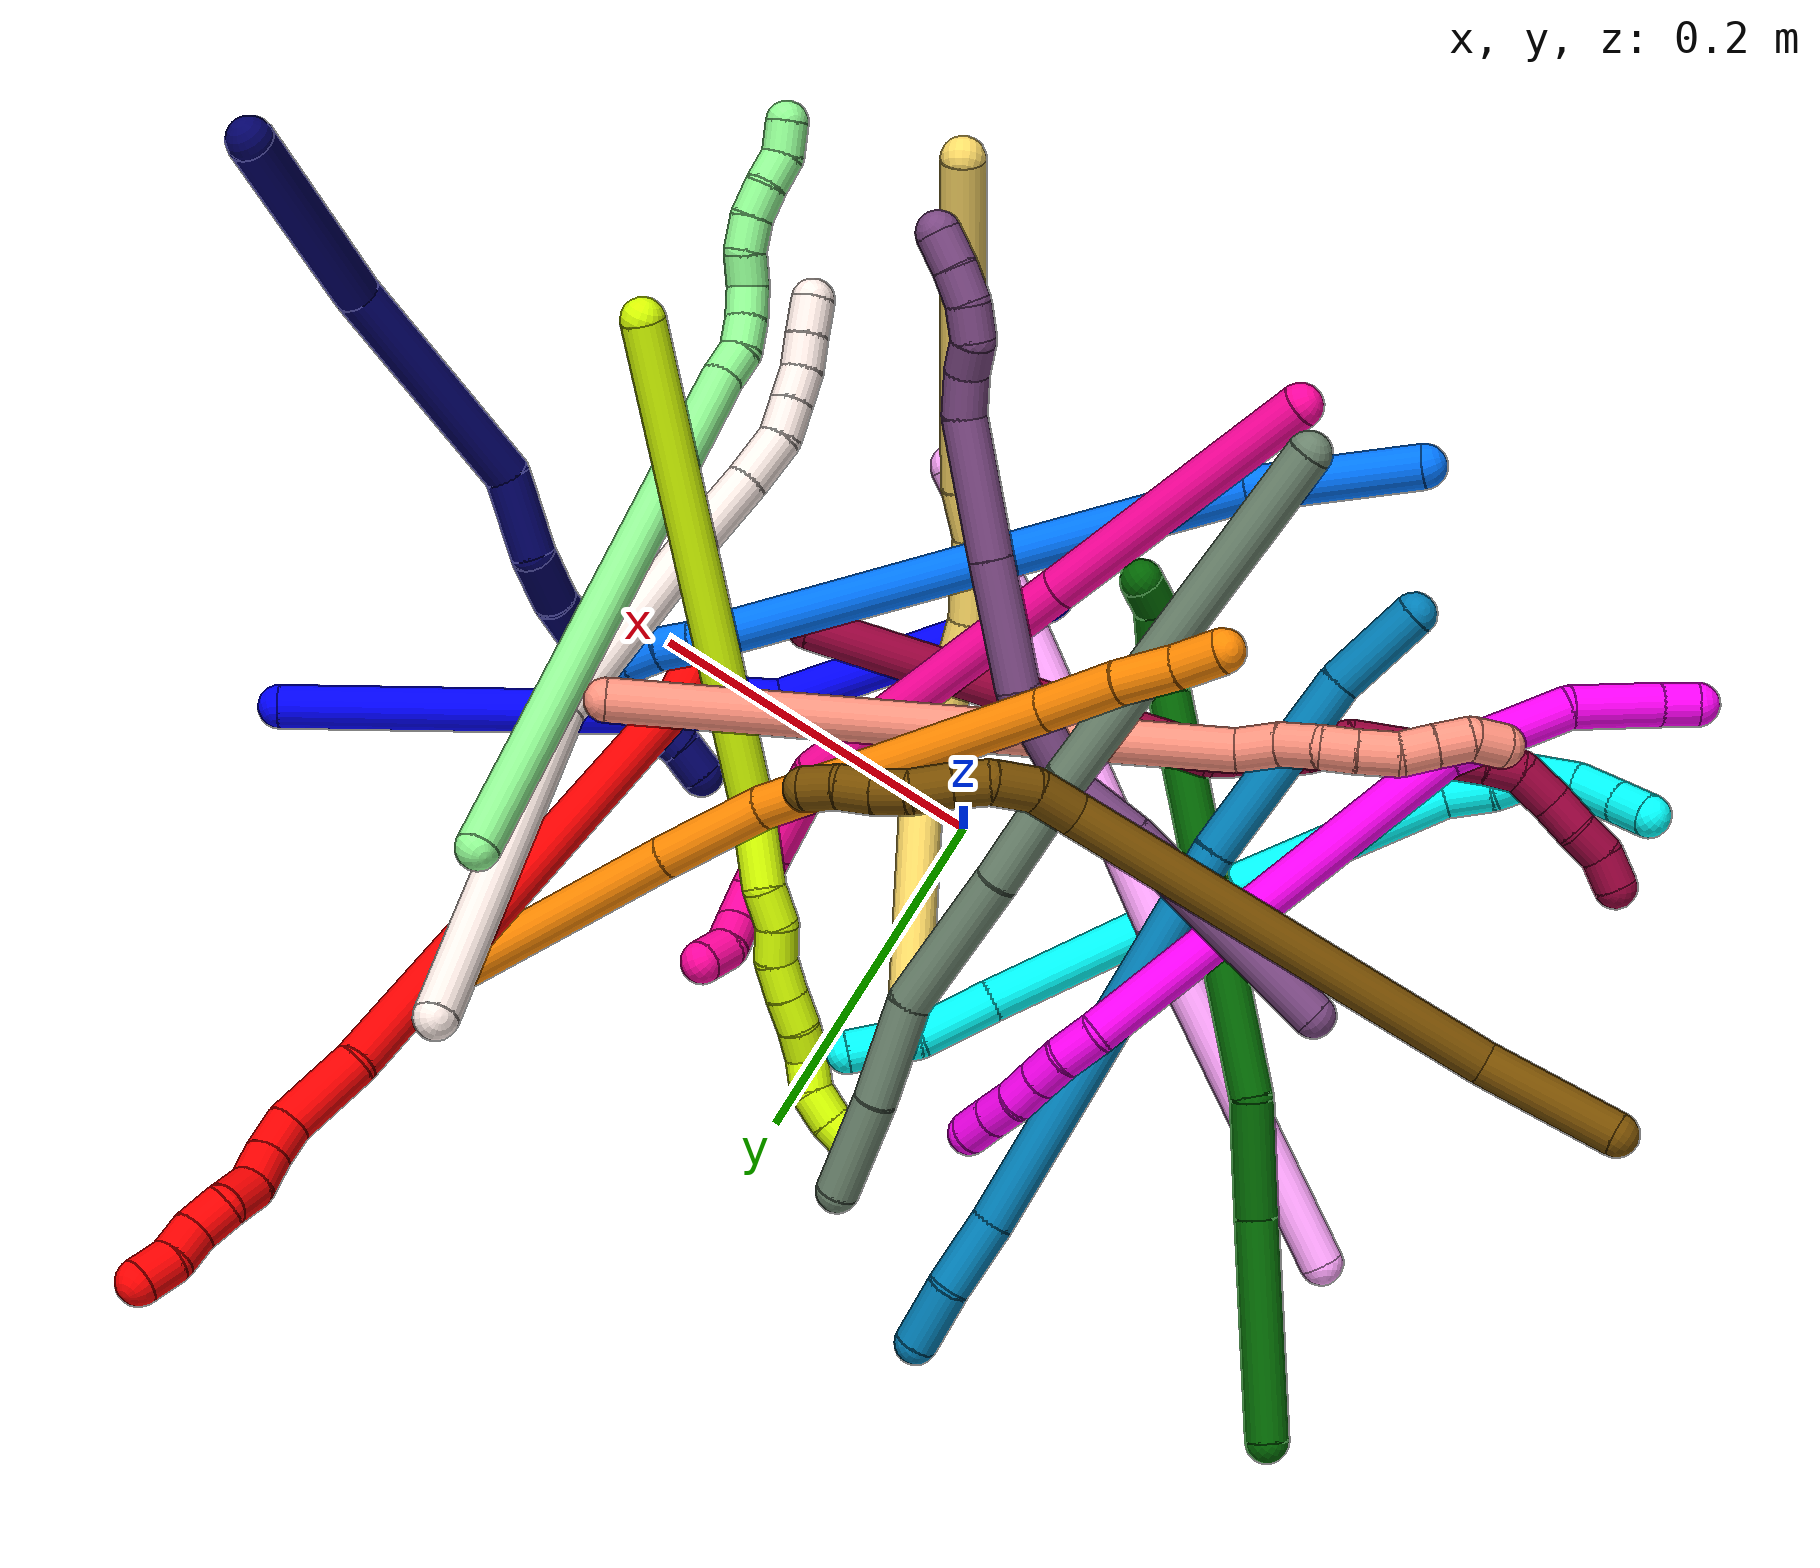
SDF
<sdf version="1.7">
 <world name="default">
  <plugin name="TubeGeneratorPlugin" filename="libtube_generator_plugin.so"/>
  <model name="photoneo_s_sensor">
   <static>1</static>
   <pose>0 0 2 1.57079 1.57079 3.14159</pose>
   <link name="link">
    <inertial><mass>0.1</mass></inertial>
    <sensor name="sensor" type="depth">
     <update_rate>30</update_rate>
     <camera>
      <horizontal_fov>1.22</horizontal_fov>
      <image><width>1920</width><height>1200</height><format>B8G8R8</format></image>
      <clip><near>0.1</near><far>4</far></clip>
      <depth_camera><output>points</output></depth_camera>
     </camera>
     <plugin name="camera_plugin" filename="libgazebo_ros_depth_camera.so">
      <baseline>0.2</baseline>
      <alwaysOn>1</alwaysOn>
      <updateRate>0.0</updateRate>
      <cameraName>camera_ir</cameraName>
      <imageTopicName>/camera/color/image_raw</imageTopicName>
      <cameraInfoTopicName>/camera/color/camera_info</cameraInfoTopicName>
      <depthImageTopicName>/camera/depth/image_raw</depthImageTopicName>
      <depthImageCameraInfoTopicName>/camera/depth/camera_info</depthImageCameraInfoTopicName>
      <pointCloudTopicName>/camera/depth/points</pointCloudTopicName>
      <frameName>fr_optical</frameName>
      <pointCloudCutoff>0.1</pointCloudCutoff>
      <pointCloudCutoffMax>2.0</pointCloudCutoffMax>
      <distortionK1>0</distortionK1>
      <distortionK2>0</distortionK2>
      <distortionK3>0</distortionK3>
      <distortionT1>0</distortionT1>
      <distortionT2>0</distortionT2>
      <CxPrime>0</CxPrime>
      <Cx>0</Cx>
      <Cy>0</Cy>
      <focalLength>0</focalLength>
      <hackBaseline>0</hackBaseline>
     </plugin>
    </sensor>
   </link>
  </model>
  <gravity>0 0 -9.8</gravity>
  <magnetic_field>6e-06 2.3e-05 -4.2e-05</magnetic_field>
  <atmosphere type="adiabatic"/>
  <physics name="default_physics" default="0" type="ode">
   <max_step_size>0.003</max_step_size>
   <real_time_factor>1</real_time_factor>
   <real_time_update_rate>1000</real_time_update_rate>
   <max_contacts>10000</max_contacts>
   <ode>
    <solver>
     <type>quick</type>
     <iters>100</iters>
     <sor>1.3</sor>
     <use_dynamic_moi_rescaling>0</use_dynamic_moi_rescaling>
    </solver>
    <constraints>
     <contact_max_correcting_vel>0</contact_max_correcting_vel>
     <contact_surface_layer>0.001</contact_surface_layer>
     <cfm>0</cfm>
     <erp>0.2</erp>
    </constraints>
   </ode>
  </physics>
  <scene><ambient>0.4 0.4 0.4 1</ambient><background>0.7 0.7 0.7 1</background><shadows>0</shadows></scene>
  <audio><device>default</device></audio>
  <spherical_coordinates>
   <surface_model>EARTH_WGS84</surface_model>
   <latitude_deg>0</latitude_deg>
   <longitude_deg>0</longitude_deg>
   <elevation>0</elevation>
   <heading_deg>0</heading_deg>
  </spherical_coordinates>
  <model name="bin">
   <static>1</static>
   <link name="bottom">
    <collision name="collision-bottom">
     <pose>0 0 -0.01 0 -0 0</pose>
     <geometry><box><size>0.8 0.6 0.02</size></box></geometry>
     <surface>
      <friction><ode><mu>100</mu><mu2>100</mu2></ode></friction>
      <contact><collide_bitmask>65535</collide_bitmask></contact>
     </surface>
    </collision>
   </link>
   <link name="west_wall">
    <collision name="collision-west_wall">
     <pose>-0.41 0 0.1 0 -0 0</pose>
     <geometry><box><size>0.02 0.6 0.2</size></box></geometry>
     <surface>
      <friction><ode><mu>100</mu><mu2>100</mu2></ode></friction>
      <contact><collide_bitmask>65535</collide_bitmask></contact>
     </surface>
    </collision>
   </link>
   <link name="east_wall">
    <collision name="collision-east_wall">
     <pose>0.41 0 0.1 0 -0 0</pose>
     <geometry><box><size>0.02 0.6 0.2</size></box></geometry>
     <surface>
      <friction><ode><mu>100</mu><mu2>100</mu2></ode></friction>
      <contact><collide_bitmask>65535</collide_bitmask></contact>
     </surface>
    </collision>
   </link>
   <link name="south_wall">
    <collision name="collision-south_wall">
     <pose>0 -0.31 0.1 0 -0 0</pose>
     <geometry><box><size>0.8 0.02 0.2</size></box></geometry>
     <surface>
      <friction><ode><mu>100</mu><mu2>100</mu2></ode></friction>
      <contact><collide_bitmask>65535</collide_bitmask></contact>
     </surface>
    </collision>
   </link>
   <link name="north_wall">
    <collision name="collision-north_wall">
     <pose>0 0.31 0.1 0 -0 0</pose>
     <geometry><box><size>0.8 0.02 0.2</size></box></geometry>
     <surface>
      <friction><ode><mu>100</mu><mu2>100</mu2></ode></friction>
      <contact><collide_bitmask>65535</collide_bitmask></contact>
     </surface>
    </collision>
   </link>
  </model>
  <model name="1">
   <static>0</static>
   <link name="1">
    <collision name="collision-cylinder-e_1_1_4">
     <pose>0.021679 -0.112838 -6.3e-05 1.57135 0.189811 0.189916</pose>
     <geometry><cylinder><radius>0.0125</radius><length>0.229803</length></cylinder></geometry>
     <surface>
      <friction><ode><mu>1.16</mu><mu2>1.16</mu2><slip1>0</slip1><slip2>0</slip2></ode></friction>
      <contact><ode><kp>1e+06</kp><kd>1</kd><max_vel>0</max_vel><min_depth>0.001</min_depth></ode></contact>
     </surface>
    </collision>
    <visual name="visual-cylinder-e_1_1_4">
     <pose>0.021679 -0.112838 -6.3e-05 1.57135 0.189811 0.189916</pose>
     <geometry><cylinder><radius>0.0125</radius><length>0.229803</length></cylinder></geometry>
     <material><ambient>0 0 1 1</ambient></material>
    </visual>
    <collision name="collision-cylinder-e_2_4_5">
     <pose>0.044781 -0.242319 0.003903 1.33334 0.08292 0.065259</pose>
     <geometry><cylinder><radius>0.0125</radius><length>0.034367</length></cylinder></geometry>
     <surface>
      <friction><ode><mu>1.16</mu><mu2>1.16</mu2><slip1>0</slip1><slip2>0</slip2></ode></friction>
      <contact><ode><kp>1e+06</kp><kd>1</kd><max_vel>0</max_vel><min_depth>0.001</min_depth></ode></contact>
     </surface>
    </collision>
    <visual name="visual-cylinder-e_2_4_5">
     <pose>0.044781 -0.242319 0.003903 1.33334 0.08292 0.065259</pose>
     <geometry><cylinder><radius>0.0125</radius><length>0.034367</length></cylinder></geometry>
     <material><ambient>0 0 1 1</ambient></material>
    </visual>
    <collision name="collision-cylinder-e_3_5_6">
     <pose>0.050586 -0.269112 0.008898 1.47577 0.405955 0.369977</pose>
     <geometry><cylinder><radius>0.0125</radius><length>0.022193</length></cylinder></geometry>
     <surface>
      <friction><ode><mu>1.16</mu><mu2>1.16</mu2><slip1>0</slip1><slip2>0</slip2></ode></friction>
      <contact><ode><kp>1e+06</kp><kd>1</kd><max_vel>0</max_vel><min_depth>0.001</min_depth></ode></contact>
     </surface>
    </collision>
    <visual name="visual-cylinder-e_3_5_6">
     <pose>0.050586 -0.269112 0.008898 1.47577 0.405955 0.369977</pose>
     <geometry><cylinder><radius>0.0125</radius><length>0.022193</length></cylinder></geometry>
     <material><ambient>0 0 1 1</ambient></material>
    </visual>
    <collision name="collision-cylinder-e_4_6_7">
     <pose>0.054472 -0.337641 0.027126 1.28334 -0.008139 -0.006081</pose>
     <geometry><cylinder><radius>0.0125</radius><length>0.121761</length></cylinder></geometry>
     <surface>
      <friction><ode><mu>1.16</mu><mu2>1.16</mu2><slip1>0</slip1><slip2>0</slip2></ode></friction>
      <contact><ode><kp>1e+06</kp><kd>1</kd><max_vel>0</max_vel><min_depth>0.001</min_depth></ode></contact>
     </surface>
    </collision>
    <visual name="visual-cylinder-e_4_6_7">
     <pose>0.054472 -0.337641 0.027126 1.28334 -0.008139 -0.006081</pose>
     <geometry><cylinder><radius>0.0125</radius><length>0.121761</length></cylinder></geometry>
     <material><ambient>0 0 1 1</ambient></material>
    </visual>
    <collision name="collision-cylinder-e_5_7_8">
     <pose>0.05374 -0.405962 0.048427 1.18461 -0.022061 -0.014845</pose>
     <geometry><cylinder><radius>0.0125</radius><length>0.021467</length></cylinder></geometry>
     <surface>
      <friction><ode><mu>1.16</mu><mu2>1.16</mu2><slip1>0</slip1><slip2>0</slip2></ode></friction>
      <contact><ode><kp>1e+06</kp><kd>1</kd><max_vel>0</max_vel><min_depth>0.001</min_depth></ode></contact>
     </surface>
    </collision>
    <visual name="visual-cylinder-e_5_7_8">
     <pose>0.05374 -0.405962 0.048427 1.18461 -0.022061 -0.014845</pose>
     <geometry><cylinder><radius>0.0125</radius><length>0.021467</length></cylinder></geometry>
     <material><ambient>0 0 1 1</ambient></material>
    </visual>
    <collision name="collision-cylinder-e_6_8_9">
     <pose>0.053762 -0.425925 0.057127 1.13572 0.023359 0.014902</pose>
     <geometry><cylinder><radius>0.0125</radius><length>0.022111</length></cylinder></geometry>
     <surface>
      <friction><ode><mu>1.16</mu><mu2>1.16</mu2><slip1>0</slip1><slip2>0</slip2></ode></friction>
      <contact><ode><kp>1e+06</kp><kd>1</kd><max_vel>0</max_vel><min_depth>0.001</min_depth></ode></contact>
     </surface>
    </collision>
    <visual name="visual-cylinder-e_6_8_9">
     <pose>0.053762 -0.425925 0.057127 1.13572 0.023359 0.014902</pose>
     <geometry><cylinder><radius>0.0125</radius><length>0.022111</length></cylinder></geometry>
     <material><ambient>0 0 1 1</ambient></material>
    </visual>
    <collision name="collision-cylinder-e_7_9_10">
     <pose>0.050789 -0.443834 0.068053 0.899263 -0.31035 -0.150703</pose>
     <geometry><cylinder><radius>0.0125</radius><length>0.021156</length></cylinder></geometry>
     <surface>
      <friction><ode><mu>1.16</mu><mu2>1.16</mu2><slip1>0</slip1><slip2>0</slip2></ode></friction>
      <contact><ode><kp>1e+06</kp><kd>1</kd><max_vel>0</max_vel><min_depth>0.001</min_depth></ode></contact>
     </surface>
    </collision>
    <visual name="visual-cylinder-e_7_9_10">
     <pose>0.050789 -0.443834 0.068053 0.899263 -0.31035 -0.150703</pose>
     <geometry><cylinder><radius>0.0125</radius><length>0.021156</length></cylinder></geometry>
     <material><ambient>0 0 1 1</ambient></material>
    </visual>
    <collision name="collision-cylinder-e_8_10_2">
     <pose>0.046684 -0.461536 0.08365 0.810818 -0.064497 -0.027689</pose>
     <geometry><cylinder><radius>0.0125</radius><length>0.027142</length></cylinder></geometry>
     <surface>
      <friction><ode><mu>1.16</mu><mu2>1.16</mu2><slip1>0</slip1><slip2>0</slip2></ode></friction>
      <contact><ode><kp>1e+06</kp><kd>1</kd><max_vel>0</max_vel><min_depth>0.001</min_depth></ode></contact>
     </surface>
    </collision>
    <visual name="visual-cylinder-e_8_10_2">
     <pose>0.046684 -0.461536 0.08365 0.810818 -0.064497 -0.027689</pose>
     <geometry><cylinder><radius>0.0125</radius><length>0.027142</length></cylinder></geometry>
     <material><ambient>0 0 1 1</ambient></material>
    </visual>
    <collision name="collision-sphere-2">
     <pose>0.045809 -0.471353 0.09298 0 -0 0</pose>
     <geometry><sphere><radius>0.0125</radius></sphere></geometry>
     <surface>
      <friction><ode><mu>1.16</mu><mu2>1.16</mu2><slip1>0</slip1><slip2>0</slip2></ode></friction>
      <contact><ode><kp>1e+06</kp><kd>1</kd><max_vel>0</max_vel><min_depth>0.001</min_depth></ode></contact>
     </surface>
    </collision>
    <visual name="visual-sphere-2">
     <pose>0.045809 -0.471353 0.09298 0 -0 0</pose>
     <geometry><sphere><radius>0.0125</radius></sphere></geometry>
     <material><ambient>0 0 1 1</ambient></material>
    </visual>
    <collision name="collision-sphere-10">
     <pose>0.047559 -0.451719 0.07432 0 -0 0</pose>
     <geometry><sphere><radius>0.0125</radius></sphere></geometry>
     <surface>
      <friction><ode><mu>1.16</mu><mu2>1.16</mu2><slip1>0</slip1><slip2>0</slip2></ode></friction>
      <contact><ode><kp>1e+06</kp><kd>1</kd><max_vel>0</max_vel><min_depth>0.001</min_depth></ode></contact>
     </surface>
    </collision>
    <visual name="visual-sphere-10">
     <pose>0.047559 -0.451719 0.07432 0 -0 0</pose>
     <geometry><sphere><radius>0.0125</radius></sphere></geometry>
     <material><ambient>0 0 1 1</ambient></material>
    </visual>
    <collision name="collision-sphere-9">
     <pose>0.05402 -0.435948 0.061786 0 -0 0</pose>
     <geometry><sphere><radius>0.0125</radius></sphere></geometry>
     <surface>
      <friction><ode><mu>1.16</mu><mu2>1.16</mu2><slip1>0</slip1><slip2>0</slip2></ode></friction>
      <contact><ode><kp>1e+06</kp><kd>1</kd><max_vel>0</max_vel><min_depth>0.001</min_depth></ode></contact>
     </surface>
    </collision>
    <visual name="visual-sphere-9">
     <pose>0.05402 -0.435948 0.061786 0 -0 0</pose>
     <geometry><sphere><radius>0.0125</radius></sphere></geometry>
     <material><ambient>0 0 1 1</ambient></material>
    </visual>
    <collision name="collision-sphere-4">
     <pose>0.043358 -0.225676 -0.000125 0 -0 0</pose>
     <geometry><sphere><radius>0.0125</radius></sphere></geometry>
     <surface>
      <friction><ode><mu>1.16</mu><mu2>1.16</mu2><slip1>0</slip1><slip2>0</slip2></ode></friction>
      <contact><ode><kp>1e+06</kp><kd>1</kd><max_vel>0</max_vel><min_depth>0.001</min_depth></ode></contact>
     </surface>
    </collision>
    <visual name="visual-sphere-4">
     <pose>0.043358 -0.225676 -0.000125 0 -0 0</pose>
     <geometry><sphere><radius>0.0125</radius></sphere></geometry>
     <material><ambient>0 0 1 1</ambient></material>
    </visual>
    <collision name="collision-sphere-1">
     <geometry><sphere><radius>0.0125</radius></sphere></geometry>
     <surface>
      <friction><ode><mu>1.16</mu><mu2>1.16</mu2><slip1>0</slip1><slip2>0</slip2></ode></friction>
      <contact><ode><kp>1e+06</kp><kd>1</kd><max_vel>0</max_vel><min_depth>0.001</min_depth></ode></contact>
     </surface>
    </collision>
    <visual name="visual-sphere-1">
     <geometry><sphere><radius>0.0125</radius></sphere></geometry>
     <material><ambient>0 0 1 1</ambient></material>
    </visual>
    <collision name="collision-sphere-8">
     <pose>0.053503 -0.415902 0.052469 0 -0 0</pose>
     <geometry><sphere><radius>0.0125</radius></sphere></geometry>
     <surface>
      <friction><ode><mu>1.16</mu><mu2>1.16</mu2><slip1>0</slip1><slip2>0</slip2></ode></friction>
      <contact><ode><kp>1e+06</kp><kd>1</kd><max_vel>0</max_vel><min_depth>0.001</min_depth></ode></contact>
     </surface>
    </collision>
    <visual name="visual-sphere-8">
     <pose>0.053503 -0.415902 0.052469 0 -0 0</pose>
     <geometry><sphere><radius>0.0125</radius></sphere></geometry>
     <material><ambient>0 0 1 1</ambient></material>
    </visual>
    <collision name="collision-sphere-5">
     <pose>0.046204 -0.258963 0.007931 0 -0 0</pose>
     <geometry><sphere><radius>0.0125</radius></sphere></geometry>
     <surface>
      <friction><ode><mu>1.16</mu><mu2>1.16</mu2><slip1>0</slip1><slip2>0</slip2></ode></friction>
      <contact><ode><kp>1e+06</kp><kd>1</kd><max_vel>0</max_vel><min_depth>0.001</min_depth></ode></contact>
     </surface>
    </collision>
    <visual name="visual-sphere-5">
     <pose>0.046204 -0.258963 0.007931 0 -0 0</pose>
     <geometry><sphere><radius>0.0125</radius></sphere></geometry>
     <material><ambient>0 0 1 1</ambient></material>
    </visual>
    <collision name="collision-sphere-6">
     <pose>0.054968 -0.27926 0.009866 0 -0 0</pose>
     <geometry><sphere><radius>0.0125</radius></sphere></geometry>
     <surface>
      <friction><ode><mu>1.16</mu><mu2>1.16</mu2><slip1>0</slip1><slip2>0</slip2></ode></friction>
      <contact><ode><kp>1e+06</kp><kd>1</kd><max_vel>0</max_vel><min_depth>0.001</min_depth></ode></contact>
     </surface>
    </collision>
    <visual name="visual-sphere-6">
     <pose>0.054968 -0.27926 0.009866 0 -0 0</pose>
     <geometry><sphere><radius>0.0125</radius></sphere></geometry>
     <material><ambient>0 0 1 1</ambient></material>
    </visual>
    <collision name="collision-sphere-7">
     <pose>0.053977 -0.396021 0.044385 0 -0 0</pose>
     <geometry><sphere><radius>0.0125</radius></sphere></geometry>
     <surface>
      <friction><ode><mu>1.16</mu><mu2>1.16</mu2><slip1>0</slip1><slip2>0</slip2></ode></friction>
      <contact><ode><kp>1e+06</kp><kd>1</kd><max_vel>0</max_vel><min_depth>0.001</min_depth></ode></contact>
     </surface>
    </collision>
    <visual name="visual-sphere-7">
     <pose>0.053977 -0.396021 0.044385 0 -0 0</pose>
     <geometry><sphere><radius>0.0125</radius></sphere></geometry>
     <material><ambient>0 0 1 1</ambient></material>
    </visual>
    <inertial>
     <pose>0.03792 -0.242783 0.019266 0 -0 0</pose>
     <mass>0.5</mass>
     <inertia>
      <ixx>0.001345</ixx>
      <ixy>0</ixy>
      <ixz>0</ixz>
      <iyy>0.000238</iyy>
      <iyz>0</iyz>
      <izz>0.000979</izz>
     </inertia>
    </inertial>
   </link>
   <pose>0.36615 0.15126 0.018551 -2.80856 1.04499 2.50344</pose>
  </model>
  <model name="2">
   <static>0</static>
   <link name="2">
    <collision name="collision-cylinder-e_1_1_4">
     <pose>-0.002412 0.002305 0.014817 -0.15431 -0.159498 0.012357</pose>
     <geometry><cylinder><radius>0.0125</radius><length>0.030376</length></cylinder></geometry>
     <surface>
      <friction><ode><mu>1.16</mu><mu2>1.16</mu2><slip1>0</slip1><slip2>0</slip2></ode></friction>
      <contact><ode><kp>1e+06</kp><kd>1</kd><max_vel>0</max_vel><min_depth>0.001</min_depth></ode></contact>
     </surface>
    </collision>
    <visual name="visual-cylinder-e_1_1_4">
     <pose>-0.002412 0.002305 0.014817 -0.15431 -0.159498 0.012357</pose>
     <geometry><cylinder><radius>0.0125</radius><length>0.030376</length></cylinder></geometry>
     <material><ambient>1 0 0 1</ambient></material>
    </visual>
    <collision name="collision-cylinder-e_2_4_5">
     <pose>0.001014 0.017735 0.178184 -0.088128 0.039133 -0.001726</pose>
     <geometry><cylinder><radius>0.0125</radius><length>0.298486</length></cylinder></geometry>
     <surface>
      <friction><ode><mu>1.16</mu><mu2>1.16</mu2><slip1>0</slip1><slip2>0</slip2></ode></friction>
      <contact><ode><kp>1e+06</kp><kd>1</kd><max_vel>0</max_vel><min_depth>0.001</min_depth></ode></contact>
     </surface>
    </collision>
    <visual name="visual-cylinder-e_2_4_5">
     <pose>0.001014 0.017735 0.178184 -0.088128 0.039133 -0.001726</pose>
     <geometry><cylinder><radius>0.0125</radius><length>0.298486</length></cylinder></geometry>
     <material><ambient>1 0 0 1</ambient></material>
    </visual>
    <collision name="collision-cylinder-e_3_5_6">
     <pose>0.01281 0.037009 0.348718 -0.272708 0.255247 -0.035209</pose>
     <geometry><cylinder><radius>0.0125</radius><length>0.047183</length></cylinder></geometry>
     <surface>
      <friction><ode><mu>1.16</mu><mu2>1.16</mu2><slip1>0</slip1><slip2>0</slip2></ode></friction>
      <contact><ode><kp>1e+06</kp><kd>1</kd><max_vel>0</max_vel><min_depth>0.001</min_depth></ode></contact>
     </surface>
    </collision>
    <visual name="visual-cylinder-e_3_5_6">
     <pose>0.01281 0.037009 0.348718 -0.272708 0.255247 -0.035209</pose>
     <geometry><cylinder><radius>0.0125</radius><length>0.047183</length></cylinder></geometry>
     <material><ambient>1 0 0 1</ambient></material>
    </visual>
    <collision name="collision-cylinder-e_4_6_7">
     <pose>0.017797 0.044508 0.381524 -0.124245 -0.088638 0.005517</pose>
     <geometry><cylinder><radius>0.0125</radius><length>0.021899</length></cylinder></geometry>
     <surface>
      <friction><ode><mu>1.16</mu><mu2>1.16</mu2><slip1>0</slip1><slip2>0</slip2></ode></friction>
      <contact><ode><kp>1e+06</kp><kd>1</kd><max_vel>0</max_vel><min_depth>0.001</min_depth></ode></contact>
     </surface>
    </collision>
    <visual name="visual-cylinder-e_4_6_7">
     <pose>0.017797 0.044508 0.381524 -0.124245 -0.088638 0.005517</pose>
     <geometry><cylinder><radius>0.0125</radius><length>0.021899</length></cylinder></geometry>
     <material><ambient>1 0 0 1</ambient></material>
    </visual>
    <collision name="collision-cylinder-e_5_7_8">
     <pose>0.014683 0.046631 0.402243 -0.07774 -0.212753 0.008305</pose>
     <geometry><cylinder><radius>0.0125</radius><length>0.020312</length></cylinder></geometry>
     <surface>
      <friction><ode><mu>1.16</mu><mu2>1.16</mu2><slip1>0</slip1><slip2>0</slip2></ode></friction>
      <contact><ode><kp>1e+06</kp><kd>1</kd><max_vel>0</max_vel><min_depth>0.001</min_depth></ode></contact>
     </surface>
    </collision>
    <visual name="visual-cylinder-e_5_7_8">
     <pose>0.014683 0.046631 0.402243 -0.07774 -0.212753 0.008305</pose>
     <geometry><cylinder><radius>0.0125</radius><length>0.020312</length></cylinder></geometry>
     <material><ambient>1 0 0 1</ambient></material>
    </visual>
    <collision name="collision-cylinder-e_6_8_9">
     <pose>0.01299 0.04481 0.422571 0.243527 0.041912 0.005129</pose>
     <geometry><cylinder><radius>0.0125</radius><length>0.021515</length></cylinder></geometry>
     <surface>
      <friction><ode><mu>1.16</mu><mu2>1.16</mu2><slip1>0</slip1><slip2>0</slip2></ode></friction>
      <contact><ode><kp>1e+06</kp><kd>1</kd><max_vel>0</max_vel><min_depth>0.001</min_depth></ode></contact>
     </surface>
    </collision>
    <visual name="visual-cylinder-e_6_8_9">
     <pose>0.01299 0.04481 0.422571 0.243527 0.041912 0.005129</pose>
     <geometry><cylinder><radius>0.0125</radius><length>0.021515</length></cylinder></geometry>
     <material><ambient>1 0 0 1</ambient></material>
    </visual>
    <collision name="collision-cylinder-e_7_9_10">
     <pose>0.016219 0.044321 0.442497 -0.217937 0.278353 -0.030648</pose>
     <geometry><cylinder><radius>0.0125</radius><length>0.020227</length></cylinder></geometry>
     <surface>
      <friction><ode><mu>1.16</mu><mu2>1.16</mu2><slip1>0</slip1><slip2>0</slip2></ode></friction>
      <contact><ode><kp>1e+06</kp><kd>1</kd><max_vel>0</max_vel><min_depth>0.001</min_depth></ode></contact>
     </surface>
    </collision>
    <visual name="visual-cylinder-e_7_9_10">
     <pose>0.016219 0.044321 0.442497 -0.217937 0.278353 -0.030648</pose>
     <geometry><cylinder><radius>0.0125</radius><length>0.020227</length></cylinder></geometry>
     <material><ambient>1 0 0 1</ambient></material>
    </visual>
    <collision name="collision-cylinder-e_8_10_11">
     <pose>0.018548 0.04702 0.461964 -0.059696 -0.045063 0.001346</pose>
     <geometry><cylinder><radius>0.0125</radius><length>0.020001</length></cylinder></geometry>
     <surface>
      <friction><ode><mu>1.16</mu><mu2>1.16</mu2><slip1>0</slip1><slip2>0</slip2></ode></friction>
      <contact><ode><kp>1e+06</kp><kd>1</kd><max_vel>0</max_vel><min_depth>0.001</min_depth></ode></contact>
     </surface>
    </collision>
    <visual name="visual-cylinder-e_8_10_11">
     <pose>0.018548 0.04702 0.461964 -0.059696 -0.045063 0.001346</pose>
     <geometry><cylinder><radius>0.0125</radius><length>0.020001</length></cylinder></geometry>
     <material><ambient>1 0 0 1</ambient></material>
    </visual>
    <collision name="collision-cylinder-e_9_11_2">
     <pose>0.020791 0.047704 0.481566 -0.009144 0.272775 -0.001255</pose>
     <geometry><cylinder><radius>0.0125</radius><length>0.02</length></cylinder></geometry>
     <surface>
      <friction><ode><mu>1.16</mu><mu2>1.16</mu2><slip1>0</slip1><slip2>0</slip2></ode></friction>
      <contact><ode><kp>1e+06</kp><kd>1</kd><max_vel>0</max_vel><min_depth>0.001</min_depth></ode></contact>
     </surface>
    </collision>
    <visual name="visual-cylinder-e_9_11_2">
     <pose>0.020791 0.047704 0.481566 -0.009144 0.272775 -0.001255</pose>
     <geometry><cylinder><radius>0.0125</radius><length>0.02</length></cylinder></geometry>
     <material><ambient>1 0 0 1</ambient></material>
    </visual>
    <collision name="collision-sphere-2">
     <pose>0.023485 0.047792 0.491196 0 -0 0</pose>
     <geometry><sphere><radius>0.0125</radius></sphere></geometry>
     <surface>
      <friction><ode><mu>1.16</mu><mu2>1.16</mu2><slip1>0</slip1><slip2>0</slip2></ode></friction>
      <contact><ode><kp>1e+06</kp><kd>1</kd><max_vel>0</max_vel><min_depth>0.001</min_depth></ode></contact>
     </surface>
    </collision>
    <visual name="visual-sphere-2">
     <pose>0.023485 0.047792 0.491196 0 -0 0</pose>
     <geometry><sphere><radius>0.0125</radius></sphere></geometry>
     <material><ambient>1 0 0 1</ambient></material>
    </visual>
    <collision name="collision-sphere-11">
     <pose>0.018097 0.047616 0.471936 0 -0 0</pose>
     <geometry><sphere><radius>0.0125</radius></sphere></geometry>
     <surface>
      <friction><ode><mu>1.16</mu><mu2>1.16</mu2><slip1>0</slip1><slip2>0</slip2></ode></friction>
      <contact><ode><kp>1e+06</kp><kd>1</kd><max_vel>0</max_vel><min_depth>0.001</min_depth></ode></contact>
     </surface>
    </collision>
    <visual name="visual-sphere-11">
     <pose>0.018097 0.047616 0.471936 0 -0 0</pose>
     <geometry><sphere><radius>0.0125</radius></sphere></geometry>
     <material><ambient>1 0 0 1</ambient></material>
    </visual>
    <collision name="collision-sphere-10">
     <pose>0.018998 0.046424 0.451991 0 -0 0</pose>
     <geometry><sphere><radius>0.0125</radius></sphere></geometry>
     <surface>
      <friction><ode><mu>1.16</mu><mu2>1.16</mu2><slip1>0</slip1><slip2>0</slip2></ode></friction>
      <contact><ode><kp>1e+06</kp><kd>1</kd><max_vel>0</max_vel><min_depth>0.001</min_depth></ode></contact>
     </surface>
    </collision>
    <visual name="visual-sphere-10">
     <pose>0.018998 0.046424 0.451991 0 -0 0</pose>
     <geometry><sphere><radius>0.0125</radius></sphere></geometry>
     <material><ambient>1 0 0 1</ambient></material>
    </visual>
    <collision name="collision-sphere-9">
     <pose>0.01344 0.042219 0.433003 0 -0 0</pose>
     <geometry><sphere><radius>0.0125</radius></sphere></geometry>
     <surface>
      <friction><ode><mu>1.16</mu><mu2>1.16</mu2><slip1>0</slip1><slip2>0</slip2></ode></friction>
      <contact><ode><kp>1e+06</kp><kd>1</kd><max_vel>0</max_vel><min_depth>0.001</min_depth></ode></contact>
     </surface>
    </collision>
    <visual name="visual-sphere-9">
     <pose>0.01344 0.042219 0.433003 0 -0 0</pose>
     <geometry><sphere><radius>0.0125</radius></sphere></geometry>
     <material><ambient>1 0 0 1</ambient></material>
    </visual>
    <collision name="collision-sphere-4">
     <pose>-0.004824 0.004609 0.029634 0 -0 0</pose>
     <geometry><sphere><radius>0.0125</radius></sphere></geometry>
     <surface>
      <friction><ode><mu>1.16</mu><mu2>1.16</mu2><slip1>0</slip1><slip2>0</slip2></ode></friction>
      <contact><ode><kp>1e+06</kp><kd>1</kd><max_vel>0</max_vel><min_depth>0.001</min_depth></ode></contact>
     </surface>
    </collision>
    <visual name="visual-sphere-4">
     <pose>-0.004824 0.004609 0.029634 0 -0 0</pose>
     <geometry><sphere><radius>0.0125</radius></sphere></geometry>
     <material><ambient>1 0 0 1</ambient></material>
    </visual>
    <collision name="collision-sphere-1">
     <geometry><sphere><radius>0.0125</radius></sphere></geometry>
     <surface>
      <friction><ode><mu>1.16</mu><mu2>1.16</mu2><slip1>0</slip1><slip2>0</slip2></ode></friction>
      <contact><ode><kp>1e+06</kp><kd>1</kd><max_vel>0</max_vel><min_depth>0.001</min_depth></ode></contact>
     </surface>
    </collision>
    <visual name="visual-sphere-1">
     <geometry><sphere><radius>0.0125</radius></sphere></geometry>
     <material><ambient>1 0 0 1</ambient></material>
    </visual>
    <collision name="collision-sphere-8">
     <pose>0.012539 0.047402 0.41214 0 -0 0</pose>
     <geometry><sphere><radius>0.0125</radius></sphere></geometry>
     <surface>
      <friction><ode><mu>1.16</mu><mu2>1.16</mu2><slip1>0</slip1><slip2>0</slip2></ode></friction>
      <contact><ode><kp>1e+06</kp><kd>1</kd><max_vel>0</max_vel><min_depth>0.001</min_depth></ode></contact>
     </surface>
    </collision>
    <visual name="visual-sphere-8">
     <pose>0.012539 0.047402 0.41214 0 -0 0</pose>
     <geometry><sphere><radius>0.0125</radius></sphere></geometry>
     <material><ambient>1 0 0 1</ambient></material>
    </visual>
    <collision name="collision-sphere-5">
     <pose>0.006853 0.03086 0.326734 0 -0 0</pose>
     <geometry><sphere><radius>0.0125</radius></sphere></geometry>
     <surface>
      <friction><ode><mu>1.16</mu><mu2>1.16</mu2><slip1>0</slip1><slip2>0</slip2></ode></friction>
      <contact><ode><kp>1e+06</kp><kd>1</kd><max_vel>0</max_vel><min_depth>0.001</min_depth></ode></contact>
     </surface>
    </collision>
    <visual name="visual-sphere-5">
     <pose>0.006853 0.03086 0.326734 0 -0 0</pose>
     <geometry><sphere><radius>0.0125</radius></sphere></geometry>
     <material><ambient>1 0 0 1</ambient></material>
    </visual>
    <collision name="collision-sphere-6">
     <pose>0.018766 0.043157 0.370701 0 -0 0</pose>
     <geometry><sphere><radius>0.0125</radius></sphere></geometry>
     <surface>
      <friction><ode><mu>1.16</mu><mu2>1.16</mu2><slip1>0</slip1><slip2>0</slip2></ode></friction>
      <contact><ode><kp>1e+06</kp><kd>1</kd><max_vel>0</max_vel><min_depth>0.001</min_depth></ode></contact>
     </surface>
    </collision>
    <visual name="visual-sphere-6">
     <pose>0.018766 0.043157 0.370701 0 -0 0</pose>
     <geometry><sphere><radius>0.0125</radius></sphere></geometry>
     <material><ambient>1 0 0 1</ambient></material>
    </visual>
    <collision name="collision-sphere-7">
     <pose>0.016828 0.04586 0.392346 0 -0 0</pose>
     <geometry><sphere><radius>0.0125</radius></sphere></geometry>
     <surface>
      <friction><ode><mu>1.16</mu><mu2>1.16</mu2><slip1>0</slip1><slip2>0</slip2></ode></friction>
      <contact><ode><kp>1e+06</kp><kd>1</kd><max_vel>0</max_vel><min_depth>0.001</min_depth></ode></contact>
     </surface>
    </collision>
    <visual name="visual-sphere-7">
     <pose>0.016828 0.04586 0.392346 0 -0 0</pose>
     <geometry><sphere><radius>0.0125</radius></sphere></geometry>
     <material><ambient>1 0 0 1</ambient></material>
    </visual>
    <inertial>
     <pose>0.005833 0.025574 0.247056 0 -0 0</pose>
     <mass>0.5</mass>
     <inertia>
      <ixx>0.002247</ixx>
      <ixy>0</ixy>
      <ixz>0</ixz>
      <iyy>0.002242</iyy>
      <iyz>0</iyz>
      <izz>-0.000251</izz>
     </inertia>
    </inertial>
   </link>
   <pose>0.177376 0.006334 0.031615 -0.875034 0.293573 0.155033</pose>
  </model>
  <model name="3">
   <static>0</static>
   <link name="3">
    <collision name="collision-cylinder-e_1_1_4">
     <pose>-0.005639 -0.015014 -0.013395 2.29924 -0.27324 -0.595512</pose>
     <geometry><cylinder><radius>0.0125</radius><length>0.041792</length></cylinder></geometry>
     <surface>
      <friction><ode><mu>1.16</mu><mu2>1.16</mu2><slip1>0</slip1><slip2>0</slip2></ode></friction>
      <contact><ode><kp>1e+06</kp><kd>1</kd><max_vel>0</max_vel><min_depth>0.001</min_depth></ode></contact>
     </surface>
    </collision>
    <visual name="visual-cylinder-e_1_1_4">
     <pose>-0.005639 -0.015014 -0.013395 2.29924 -0.27324 -0.595512</pose>
     <geometry><cylinder><radius>0.0125</radius><length>0.041792</length></cylinder></geometry>
     <material><ambient>0.003922 1 0.996078 1</ambient></material>
    </visual>
    <collision name="collision-cylinder-e_2_4_5">
     <pose>-0.023193 -0.043996 -0.040884 2.36076 -0.540788 -1.18546</pose>
     <geometry><cylinder><radius>0.0125</radius><length>0.046291</length></cylinder></geometry>
     <surface>
      <friction><ode><mu>1.16</mu><mu2>1.16</mu2><slip1>0</slip1><slip2>0</slip2></ode></friction>
      <contact><ode><kp>1e+06</kp><kd>1</kd><max_vel>0</max_vel><min_depth>0.001</min_depth></ode></contact>
     </surface>
    </collision>
    <visual name="visual-cylinder-e_2_4_5">
     <pose>-0.023193 -0.043996 -0.040884 2.36076 -0.540788 -1.18546</pose>
     <geometry><cylinder><radius>0.0125</radius><length>0.046291</length></cylinder></geometry>
     <material><ambient>0.003922 1 0.996078 1</ambient></material>
    </visual>
    <collision name="collision-cylinder-e_3_5_6">
     <pose>-0.067783 -0.099012 -0.10911 2.49278 -0.448299 -1.19152</pose>
     <geometry><cylinder><radius>0.0125</radius><length>0.150769</length></cylinder></geometry>
     <surface>
      <friction><ode><mu>1.16</mu><mu2>1.16</mu2><slip1>0</slip1><slip2>0</slip2></ode></friction>
      <contact><ode><kp>1e+06</kp><kd>1</kd><max_vel>0</max_vel><min_depth>0.001</min_depth></ode></contact>
     </surface>
    </collision>
    <visual name="visual-cylinder-e_3_5_6">
     <pose>-0.067783 -0.099012 -0.10911 2.49278 -0.448299 -1.19152</pose>
     <geometry><cylinder><radius>0.0125</radius><length>0.150769</length></cylinder></geometry>
     <material><ambient>0.003922 1 0.996078 1</ambient></material>
    </visual>
    <collision name="collision-cylinder-e_4_6_7">
     <pose>-0.129838 -0.180692 -0.206826 2.39127 -0.458098 -1.06904</pose>
     <geometry><cylinder><radius>0.0125</radius><length>0.132872</length></cylinder></geometry>
     <surface>
      <friction><ode><mu>1.16</mu><mu2>1.16</mu2><slip1>0</slip1><slip2>0</slip2></ode></friction>
      <contact><ode><kp>1e+06</kp><kd>1</kd><max_vel>0</max_vel><min_depth>0.001</min_depth></ode></contact>
     </surface>
    </collision>
    <visual name="visual-cylinder-e_4_6_7">
     <pose>-0.129838 -0.180692 -0.206826 2.39127 -0.458098 -1.06904</pose>
     <geometry><cylinder><radius>0.0125</radius><length>0.132872</length></cylinder></geometry>
     <material><ambient>0.003922 1 0.996078 1</ambient></material>
    </visual>
    <collision name="collision-cylinder-e_5_7_8">
     <pose>-0.159966 -0.228877 -0.262617 2.58733 -0.052003 -0.182352</pose>
     <geometry><cylinder><radius>0.0125</radius><length>0.028747</length></cylinder></geometry>
     <surface>
      <friction><ode><mu>1.16</mu><mu2>1.16</mu2><slip1>0</slip1><slip2>0</slip2></ode></friction>
      <contact><ode><kp>1e+06</kp><kd>1</kd><max_vel>0</max_vel><min_depth>0.001</min_depth></ode></contact>
     </surface>
    </collision>
    <visual name="visual-cylinder-e_5_7_8">
     <pose>-0.159966 -0.228877 -0.262617 2.58733 -0.052003 -0.182352</pose>
     <geometry><cylinder><radius>0.0125</radius><length>0.028747</length></cylinder></geometry>
     <material><ambient>0.003922 1 0.996078 1</ambient></material>
    </visual>
    <collision name="collision-cylinder-e_6_8_9">
     <pose>-0.163789 -0.242204 -0.284397 2.59909 -0.268443 -0.90403</pose>
     <geometry><cylinder><radius>0.0125</radius><length>0.02319</length></cylinder></geometry>
     <surface>
      <friction><ode><mu>1.16</mu><mu2>1.16</mu2><slip1>0</slip1><slip2>0</slip2></ode></friction>
      <contact><ode><kp>1e+06</kp><kd>1</kd><max_vel>0</max_vel><min_depth>0.001</min_depth></ode></contact>
     </surface>
    </collision>
    <visual name="visual-cylinder-e_6_8_9">
     <pose>-0.163789 -0.242204 -0.284397 2.59909 -0.268443 -0.90403</pose>
     <geometry><cylinder><radius>0.0125</radius><length>0.02319</length></cylinder></geometry>
     <material><ambient>0.003922 1 0.996078 1</ambient></material>
    </visual>
    <collision name="collision-cylinder-e_7_9_10">
     <pose>-0.16419 -0.256514 -0.303298 2.40034 0.208361 0.525702</pose>
     <geometry><cylinder><radius>0.0125</radius><length>0.025849</length></cylinder></geometry>
     <surface>
      <friction><ode><mu>1.16</mu><mu2>1.16</mu2><slip1>0</slip1><slip2>0</slip2></ode></friction>
      <contact><ode><kp>1e+06</kp><kd>1</kd><max_vel>0</max_vel><min_depth>0.001</min_depth></ode></contact>
     </surface>
    </collision>
    <visual name="visual-cylinder-e_7_9_10">
     <pose>-0.16419 -0.256514 -0.303298 2.40034 0.208361 0.525702</pose>
     <geometry><cylinder><radius>0.0125</radius><length>0.025849</length></cylinder></geometry>
     <material><ambient>0.003922 1 0.996078 1</ambient></material>
    </visual>
    <collision name="collision-cylinder-e_8_10_11">
     <pose>-0.153577 -0.270517 -0.323556 2.67797 0.576177 1.79628</pose>
     <geometry><cylinder><radius>0.0125</radius><length>0.029146</length></cylinder></geometry>
     <surface>
      <friction><ode><mu>1.16</mu><mu2>1.16</mu2><slip1>0</slip1><slip2>0</slip2></ode></friction>
      <contact><ode><kp>1e+06</kp><kd>1</kd><max_vel>0</max_vel><min_depth>0.001</min_depth></ode></contact>
     </surface>
    </collision>
    <visual name="visual-cylinder-e_8_10_11">
     <pose>-0.153577 -0.270517 -0.323556 2.67797 0.576177 1.79628</pose>
     <geometry><cylinder><radius>0.0125</radius><length>0.029146</length></cylinder></geometry>
     <material><ambient>0.003922 1 0.996078 1</ambient></material>
    </visual>
    <collision name="collision-cylinder-e_9_11_2">
     <pose>-0.139554 -0.279168 -0.342655 2.76973 0.606549 2.05912</pose>
     <geometry><cylinder><radius>0.0125</radius><length>0.021343</length></cylinder></geometry>
     <surface>
      <friction><ode><mu>1.16</mu><mu2>1.16</mu2><slip1>0</slip1><slip2>0</slip2></ode></friction>
      <contact><ode><kp>1e+06</kp><kd>1</kd><max_vel>0</max_vel><min_depth>0.001</min_depth></ode></contact>
     </surface>
    </collision>
    <visual name="visual-cylinder-e_9_11_2">
     <pose>-0.139554 -0.279168 -0.342655 2.76973 0.606549 2.05912</pose>
     <geometry><cylinder><radius>0.0125</radius><length>0.021343</length></cylinder></geometry>
     <material><ambient>0.003922 1 0.996078 1</ambient></material>
    </visual>
    <collision name="collision-sphere-2">
     <pose>-0.133471 -0.282353 -0.350823 0 -0 0</pose>
     <geometry><sphere><radius>0.0125</radius></sphere></geometry>
     <surface>
      <friction><ode><mu>1.16</mu><mu2>1.16</mu2><slip1>0</slip1><slip2>0</slip2></ode></friction>
      <contact><ode><kp>1e+06</kp><kd>1</kd><max_vel>0</max_vel><min_depth>0.001</min_depth></ode></contact>
     </surface>
    </collision>
    <visual name="visual-sphere-2">
     <pose>-0.133471 -0.282353 -0.350823 0 -0 0</pose>
     <geometry><sphere><radius>0.0125</radius></sphere></geometry>
     <material><ambient>0.003922 1 0.996078 1</ambient></material>
    </visual>
    <collision name="collision-sphere-11">
     <pose>-0.145638 -0.275982 -0.334486 0 -0 0</pose>
     <geometry><sphere><radius>0.0125</radius></sphere></geometry>
     <surface>
      <friction><ode><mu>1.16</mu><mu2>1.16</mu2><slip1>0</slip1><slip2>0</slip2></ode></friction>
      <contact><ode><kp>1e+06</kp><kd>1</kd><max_vel>0</max_vel><min_depth>0.001</min_depth></ode></contact>
     </surface>
    </collision>
    <visual name="visual-sphere-11">
     <pose>-0.145638 -0.275982 -0.334486 0 -0 0</pose>
     <geometry><sphere><radius>0.0125</radius></sphere></geometry>
     <material><ambient>0.003922 1 0.996078 1</ambient></material>
    </visual>
    <collision name="collision-sphere-10">
     <pose>-0.161517 -0.265052 -0.312626 0 -0 0</pose>
     <geometry><sphere><radius>0.0125</radius></sphere></geometry>
     <surface>
      <friction><ode><mu>1.16</mu><mu2>1.16</mu2><slip1>0</slip1><slip2>0</slip2></ode></friction>
      <contact><ode><kp>1e+06</kp><kd>1</kd><max_vel>0</max_vel><min_depth>0.001</min_depth></ode></contact>
     </surface>
    </collision>
    <visual name="visual-sphere-10">
     <pose>-0.161517 -0.265052 -0.312626 0 -0 0</pose>
     <geometry><sphere><radius>0.0125</radius></sphere></geometry>
     <material><ambient>0.003922 1 0.996078 1</ambient></material>
    </visual>
    <collision name="collision-sphere-9">
     <pose>-0.166864 -0.247976 -0.293971 0 -0 0</pose>
     <geometry><sphere><radius>0.0125</radius></sphere></geometry>
     <surface>
      <friction><ode><mu>1.16</mu><mu2>1.16</mu2><slip1>0</slip1><slip2>0</slip2></ode></friction>
      <contact><ode><kp>1e+06</kp><kd>1</kd><max_vel>0</max_vel><min_depth>0.001</min_depth></ode></contact>
     </surface>
    </collision>
    <visual name="visual-sphere-9">
     <pose>-0.166864 -0.247976 -0.293971 0 -0 0</pose>
     <geometry><sphere><radius>0.0125</radius></sphere></geometry>
     <material><ambient>0.003922 1 0.996078 1</ambient></material>
    </visual>
    <collision name="collision-sphere-4">
     <pose>-0.011278 -0.030029 -0.026789 0 -0 0</pose>
     <geometry><sphere><radius>0.0125</radius></sphere></geometry>
     <surface>
      <friction><ode><mu>1.16</mu><mu2>1.16</mu2><slip1>0</slip1><slip2>0</slip2></ode></friction>
      <contact><ode><kp>1e+06</kp><kd>1</kd><max_vel>0</max_vel><min_depth>0.001</min_depth></ode></contact>
     </surface>
    </collision>
    <visual name="visual-sphere-4">
     <pose>-0.011278 -0.030029 -0.026789 0 -0 0</pose>
     <geometry><sphere><radius>0.0125</radius></sphere></geometry>
     <material><ambient>0.003922 1 0.996078 1</ambient></material>
    </visual>
    <collision name="collision-sphere-1">
     <geometry><sphere><radius>0.0125</radius></sphere></geometry>
     <surface>
      <friction><ode><mu>1.16</mu><mu2>1.16</mu2><slip1>0</slip1><slip2>0</slip2></ode></friction>
      <contact><ode><kp>1e+06</kp><kd>1</kd><max_vel>0</max_vel><min_depth>0.001</min_depth></ode></contact>
     </surface>
    </collision>
    <visual name="visual-sphere-1">
     <geometry><sphere><radius>0.0125</radius></sphere></geometry>
     <material><ambient>0.003922 1 0.996078 1</ambient></material>
    </visual>
    <collision name="collision-sphere-8">
     <pose>-0.160713 -0.236432 -0.274822 0 -0 0</pose>
     <geometry><sphere><radius>0.0125</radius></sphere></geometry>
     <surface>
      <friction><ode><mu>1.16</mu><mu2>1.16</mu2><slip1>0</slip1><slip2>0</slip2></ode></friction>
      <contact><ode><kp>1e+06</kp><kd>1</kd><max_vel>0</max_vel><min_depth>0.001</min_depth></ode></contact>
     </surface>
    </collision>
    <visual name="visual-sphere-8">
     <pose>-0.160713 -0.236432 -0.274822 0 -0 0</pose>
     <geometry><sphere><radius>0.0125</radius></sphere></geometry>
     <material><ambient>0.003922 1 0.996078 1</ambient></material>
    </visual>
    <collision name="collision-sphere-5">
     <pose>-0.035109 -0.057962 -0.054979 0 -0 0</pose>
     <geometry><sphere><radius>0.0125</radius></sphere></geometry>
     <surface>
      <friction><ode><mu>1.16</mu><mu2>1.16</mu2><slip1>0</slip1><slip2>0</slip2></ode></friction>
      <contact><ode><kp>1e+06</kp><kd>1</kd><max_vel>0</max_vel><min_depth>0.001</min_depth></ode></contact>
     </surface>
    </collision>
    <visual name="visual-sphere-5">
     <pose>-0.035109 -0.057962 -0.054979 0 -0 0</pose>
     <geometry><sphere><radius>0.0125</radius></sphere></geometry>
     <material><ambient>0.003922 1 0.996078 1</ambient></material>
    </visual>
    <collision name="collision-sphere-6">
     <pose>-0.100457 -0.140062 -0.163241 0 -0 0</pose>
     <geometry><sphere><radius>0.0125</radius></sphere></geometry>
     <surface>
      <friction><ode><mu>1.16</mu><mu2>1.16</mu2><slip1>0</slip1><slip2>0</slip2></ode></friction>
      <contact><ode><kp>1e+06</kp><kd>1</kd><max_vel>0</max_vel><min_depth>0.001</min_depth></ode></contact>
     </surface>
    </collision>
    <visual name="visual-sphere-6">
     <pose>-0.100457 -0.140062 -0.163241 0 -0 0</pose>
     <geometry><sphere><radius>0.0125</radius></sphere></geometry>
     <material><ambient>0.003922 1 0.996078 1</ambient></material>
    </visual>
    <collision name="collision-sphere-7">
     <pose>-0.159219 -0.221322 -0.250411 0 -0 0</pose>
     <geometry><sphere><radius>0.0125</radius></sphere></geometry>
     <surface>
      <friction><ode><mu>1.16</mu><mu2>1.16</mu2><slip1>0</slip1><slip2>0</slip2></ode></friction>
      <contact><ode><kp>1e+06</kp><kd>1</kd><max_vel>0</max_vel><min_depth>0.001</min_depth></ode></contact>
     </surface>
    </collision>
    <visual name="visual-sphere-7">
     <pose>-0.159219 -0.221322 -0.250411 0 -0 0</pose>
     <geometry><sphere><radius>0.0125</radius></sphere></geometry>
     <material><ambient>0.003922 1 0.996078 1</ambient></material>
    </visual>
    <inertial>
     <pose>-0.097753 -0.148541 -0.170225 0 -0 0</pose>
     <mass>0.5</mass>
     <inertia>
      <ixx>-0.000223</ixx>
      <ixy>0</ixy>
      <ixz>0</ixz>
      <iyy>-0.000471</iyy>
      <iyz>0</iyz>
      <izz>0.000491</izz>
     </inertia>
    </inertial>
   </link>
   <pose>-0.012777 0.1433 0.019303 2.49547 -0.435866 2.05597</pose>
  </model>
  <model name="4">
   <static>0</static>
   <link name="4">
    <collision name="collision-cylinder-e_1_1_4">
     <pose>-0.041923 -0.033245 0.092179 0.346139 -0.404265 -0.071621</pose>
     <geometry><cylinder><radius>0.0125</radius><length>0.213164</length></cylinder></geometry>
     <surface>
      <friction><ode><mu>1.16</mu><mu2>1.16</mu2><slip1>0</slip1><slip2>0</slip2></ode></friction>
      <contact><ode><kp>1e+06</kp><kd>1</kd><max_vel>0</max_vel><min_depth>0.001</min_depth></ode></contact>
     </surface>
    </collision>
    <visual name="visual-cylinder-e_1_1_4">
     <pose>-0.041923 -0.033245 0.092179 0.346139 -0.404265 -0.071621</pose>
     <geometry><cylinder><radius>0.0125</radius><length>0.213164</length></cylinder></geometry>
     <material><ambient>1 0.65098 0.996078 1</ambient></material>
    </visual>
    <collision name="collision-cylinder-e_2_4_5">
     <pose>-0.116999 -0.091418 0.271754 0.277841 -0.349784 -0.049402</pose>
     <geometry><cylinder><radius>0.0125</radius><length>0.19348</length></cylinder></geometry>
     <surface>
      <friction><ode><mu>1.16</mu><mu2>1.16</mu2><slip1>0</slip1><slip2>0</slip2></ode></friction>
      <contact><ode><kp>1e+06</kp><kd>1</kd><max_vel>0</max_vel><min_depth>0.001</min_depth></ode></contact>
     </surface>
    </collision>
    <visual name="visual-cylinder-e_2_4_5">
     <pose>-0.116999 -0.091418 0.271754 0.277841 -0.349784 -0.049402</pose>
     <geometry><cylinder><radius>0.0125</radius><length>0.19348</length></cylinder></geometry>
     <material><ambient>1 0.65098 0.996078 1</ambient></material>
    </visual>
    <collision name="collision-cylinder-e_3_5_6">
     <pose>-0.153729 -0.116319 0.370158 -0.002324 -0.314303 0.000368</pose>
     <geometry><cylinder><radius>0.0125</radius><length>0.023148</length></cylinder></geometry>
     <surface>
      <friction><ode><mu>1.16</mu><mu2>1.16</mu2><slip1>0</slip1><slip2>0</slip2></ode></friction>
      <contact><ode><kp>1e+06</kp><kd>1</kd><max_vel>0</max_vel><min_depth>0.001</min_depth></ode></contact>
     </surface>
    </collision>
    <visual name="visual-cylinder-e_3_5_6">
     <pose>-0.153729 -0.116319 0.370158 -0.002324 -0.314303 0.000368</pose>
     <geometry><cylinder><radius>0.0125</radius><length>0.023148</length></cylinder></geometry>
     <material><ambient>1 0.65098 0.996078 1</ambient></material>
    </visual>
    <collision name="collision-cylinder-e_4_6_7">
     <pose>-0.161975 -0.11807 0.399037 0.099068 -0.254277 -0.012674</pose>
     <geometry><cylinder><radius>0.0125</radius><length>0.037115</length></cylinder></geometry>
     <surface>
      <friction><ode><mu>1.16</mu><mu2>1.16</mu2><slip1>0</slip1><slip2>0</slip2></ode></friction>
      <contact><ode><kp>1e+06</kp><kd>1</kd><max_vel>0</max_vel><min_depth>0.001</min_depth></ode></contact>
     </surface>
    </collision>
    <visual name="visual-cylinder-e_4_6_7">
     <pose>-0.161975 -0.11807 0.399037 0.099068 -0.254277 -0.012674</pose>
     <geometry><cylinder><radius>0.0125</radius><length>0.037115</length></cylinder></geometry>
     <material><ambient>1 0.65098 0.996078 1</ambient></material>
    </visual>
    <collision name="collision-cylinder-e_5_7_2">
     <pose>-0.173451 -0.125393 0.430935 0.376595 -0.424004 -0.081983</pose>
     <geometry><cylinder><radius>0.0125</radius><length>0.033093</length></cylinder></geometry>
     <surface>
      <friction><ode><mu>1.16</mu><mu2>1.16</mu2><slip1>0</slip1><slip2>0</slip2></ode></friction>
      <contact><ode><kp>1e+06</kp><kd>1</kd><max_vel>0</max_vel><min_depth>0.001</min_depth></ode></contact>
     </surface>
    </collision>
    <visual name="visual-cylinder-e_5_7_2">
     <pose>-0.173451 -0.125393 0.430935 0.376595 -0.424004 -0.081983</pose>
     <geometry><cylinder><radius>0.0125</radius><length>0.033093</length></cylinder></geometry>
     <material><ambient>1 0.65098 0.996078 1</ambient></material>
    </visual>
    <collision name="collision-sphere-2">
     <pose>-0.180258 -0.130939 0.444959 0 -0 0</pose>
     <geometry><sphere><radius>0.0125</radius></sphere></geometry>
     <surface>
      <friction><ode><mu>1.16</mu><mu2>1.16</mu2><slip1>0</slip1><slip2>0</slip2></ode></friction>
      <contact><ode><kp>1e+06</kp><kd>1</kd><max_vel>0</max_vel><min_depth>0.001</min_depth></ode></contact>
     </surface>
    </collision>
    <visual name="visual-sphere-2">
     <pose>-0.180258 -0.130939 0.444959 0 -0 0</pose>
     <geometry><sphere><radius>0.0125</radius></sphere></geometry>
     <material><ambient>1 0.65098 0.996078 1</ambient></material>
    </visual>
    <collision name="collision-sphere-7">
     <pose>-0.166644 -0.119846 0.41691 0 -0 0</pose>
     <geometry><sphere><radius>0.0125</radius></sphere></geometry>
     <surface>
      <friction><ode><mu>1.16</mu><mu2>1.16</mu2><slip1>0</slip1><slip2>0</slip2></ode></friction>
      <contact><ode><kp>1e+06</kp><kd>1</kd><max_vel>0</max_vel><min_depth>0.001</min_depth></ode></contact>
     </surface>
    </collision>
    <visual name="visual-sphere-7">
     <pose>-0.166644 -0.119846 0.41691 0 -0 0</pose>
     <geometry><sphere><radius>0.0125</radius></sphere></geometry>
     <material><ambient>1 0.65098 0.996078 1</ambient></material>
    </visual>
    <collision name="collision-sphere-6">
     <pose>-0.157307 -0.116293 0.381165 0 -0 0</pose>
     <geometry><sphere><radius>0.0125</radius></sphere></geometry>
     <surface>
      <friction><ode><mu>1.16</mu><mu2>1.16</mu2><slip1>0</slip1><slip2>0</slip2></ode></friction>
      <contact><ode><kp>1e+06</kp><kd>1</kd><max_vel>0</max_vel><min_depth>0.001</min_depth></ode></contact>
     </surface>
    </collision>
    <visual name="visual-sphere-6">
     <pose>-0.157307 -0.116293 0.381165 0 -0 0</pose>
     <geometry><sphere><radius>0.0125</radius></sphere></geometry>
     <material><ambient>1 0.65098 0.996078 1</ambient></material>
    </visual>
    <collision name="collision-sphere-5">
     <pose>-0.150151 -0.116345 0.359151 0 -0 0</pose>
     <geometry><sphere><radius>0.0125</radius></sphere></geometry>
     <surface>
      <friction><ode><mu>1.16</mu><mu2>1.16</mu2><slip1>0</slip1><slip2>0</slip2></ode></friction>
      <contact><ode><kp>1e+06</kp><kd>1</kd><max_vel>0</max_vel><min_depth>0.001</min_depth></ode></contact>
     </surface>
    </collision>
    <visual name="visual-sphere-5">
     <pose>-0.150151 -0.116345 0.359151 0 -0 0</pose>
     <geometry><sphere><radius>0.0125</radius></sphere></geometry>
     <material><ambient>1 0.65098 0.996078 1</ambient></material>
    </visual>
    <collision name="collision-sphere-1">
     <geometry><sphere><radius>0.0125</radius></sphere></geometry>
     <surface>
      <friction><ode><mu>1.16</mu><mu2>1.16</mu2><slip1>0</slip1><slip2>0</slip2></ode></friction>
      <contact><ode><kp>1e+06</kp><kd>1</kd><max_vel>0</max_vel><min_depth>0.001</min_depth></ode></contact>
     </surface>
    </collision>
    <visual name="visual-sphere-1">
     <geometry><sphere><radius>0.0125</radius></sphere></geometry>
     <material><ambient>1 0.65098 0.996078 1</ambient></material>
    </visual>
    <collision name="collision-sphere-4">
     <pose>-0.083847 -0.06649 0.184358 0 -0 0</pose>
     <geometry><sphere><radius>0.0125</radius></sphere></geometry>
     <surface>
      <friction><ode><mu>1.16</mu><mu2>1.16</mu2><slip1>0</slip1><slip2>0</slip2></ode></friction>
      <contact><ode><kp>1e+06</kp><kd>1</kd><max_vel>0</max_vel><min_depth>0.001</min_depth></ode></contact>
     </surface>
    </collision>
    <visual name="visual-sphere-4">
     <pose>-0.083847 -0.06649 0.184358 0 -0 0</pose>
     <geometry><sphere><radius>0.0125</radius></sphere></geometry>
     <material><ambient>1 0.65098 0.996078 1</ambient></material>
    </visual>
    <inertial>
     <pose>-0.093767 -0.071997 0.219736 0 -0 0</pose>
     <mass>0.5</mass>
     <inertia>
      <ixx>0.001236</ixx>
      <ixy>0</ixy>
      <ixz>0</ixz>
      <iyy>0.001282</iyy>
      <iyz>0</iyz>
      <izz>0.000983</izz>
     </inertia>
    </inertial>
   </link>
   <pose>-0.302845 0.099861 0.018682 -1.90538 0.20326 -2.51459</pose>
  </model>
  <model name="5">
   <static>0</static>
   <link name="5">
    <collision name="collision-cylinder-e_1_1_4">
     <pose>-0.001497 -0.002715 0.057844 0.04691 -0.025854 -0.000607</pose>
     <geometry><cylinder><radius>0.0125</radius><length>0.115854</length></cylinder></geometry>
     <surface>
      <friction><ode><mu>1.16</mu><mu2>1.16</mu2><slip1>0</slip1><slip2>0</slip2></ode></friction>
      <contact><ode><kp>1e+06</kp><kd>1</kd><max_vel>0</max_vel><min_depth>0.001</min_depth></ode></contact>
     </surface>
    </collision>
    <visual name="visual-cylinder-e_1_1_4">
     <pose>-0.001497 -0.002715 0.057844 0.04691 -0.025854 -0.000607</pose>
     <geometry><cylinder><radius>0.0125</radius><length>0.115854</length></cylinder></geometry>
     <material><ambient>1 0.858824 0.4 1</ambient></material>
    </visual>
    <collision name="collision-cylinder-e_2_4_5">
     <pose>-0.000279 -0.032917 0.161 0.545257 0.051204 0.014319</pose>
     <geometry><cylinder><radius>0.0125</radius><length>0.106134</length></cylinder></geometry>
     <surface>
      <friction><ode><mu>1.16</mu><mu2>1.16</mu2><slip1>0</slip1><slip2>0</slip2></ode></friction>
      <contact><ode><kp>1e+06</kp><kd>1</kd><max_vel>0</max_vel><min_depth>0.001</min_depth></ode></contact>
     </surface>
    </collision>
    <visual name="visual-cylinder-e_2_4_5">
     <pose>-0.000279 -0.032917 0.161 0.545257 0.051204 0.014319</pose>
     <geometry><cylinder><radius>0.0125</radius><length>0.106134</length></cylinder></geometry>
     <material><ambient>1 0.858824 0.4 1</ambient></material>
    </visual>
    <collision name="collision-cylinder-e_3_5_6">
     <pose>-0.001524 -0.072688 0.227249 0.530608 -0.161783 -0.044047</pose>
     <geometry><cylinder><radius>0.0125</radius><length>0.04919</length></cylinder></geometry>
     <surface>
      <friction><ode><mu>1.16</mu><mu2>1.16</mu2><slip1>0</slip1><slip2>0</slip2></ode></friction>
      <contact><ode><kp>1e+06</kp><kd>1</kd><max_vel>0</max_vel><min_depth>0.001</min_depth></ode></contact>
     </surface>
    </collision>
    <visual name="visual-cylinder-e_3_5_6">
     <pose>-0.001524 -0.072688 0.227249 0.530608 -0.161783 -0.044047</pose>
     <geometry><cylinder><radius>0.0125</radius><length>0.04919</length></cylinder></geometry>
     <material><ambient>1 0.858824 0.4 1</ambient></material>
    </visual>
    <collision name="collision-cylinder-e_4_6_7">
     <pose>-0.012054 -0.091844 0.26023 0.518486 -0.442344 -0.119125</pose>
     <geometry><cylinder><radius>0.0125</radius><length>0.030688</length></cylinder></geometry>
     <surface>
      <friction><ode><mu>1.16</mu><mu2>1.16</mu2><slip1>0</slip1><slip2>0</slip2></ode></friction>
      <contact><ode><kp>1e+06</kp><kd>1</kd><max_vel>0</max_vel><min_depth>0.001</min_depth></ode></contact>
     </surface>
    </collision>
    <visual name="visual-cylinder-e_4_6_7">
     <pose>-0.012054 -0.091844 0.26023 0.518486 -0.442344 -0.119125</pose>
     <geometry><cylinder><radius>0.0125</radius><length>0.030688</length></cylinder></geometry>
     <material><ambient>1 0.858824 0.4 1</ambient></material>
    </visual>
    <collision name="collision-cylinder-e_5_7_2">
     <pose>-0.044348 -0.164646 0.341598 0.760313 -0.262686 -0.105478</pose>
     <geometry><cylinder><radius>0.0125</radius><length>0.198134</length></cylinder></geometry>
     <surface>
      <friction><ode><mu>1.16</mu><mu2>1.16</mu2><slip1>0</slip1><slip2>0</slip2></ode></friction>
      <contact><ode><kp>1e+06</kp><kd>1</kd><max_vel>0</max_vel><min_depth>0.001</min_depth></ode></contact>
     </surface>
    </collision>
    <visual name="visual-cylinder-e_5_7_2">
     <pose>-0.044348 -0.164646 0.341598 0.760313 -0.262686 -0.105478</pose>
     <geometry><cylinder><radius>0.0125</radius><length>0.198134</length></cylinder></geometry>
     <material><ambient>1 0.858824 0.4 1</ambient></material>
    </visual>
    <collision name="collision-sphere-2">
     <pose>-0.070073 -0.230576 0.410921 0 -0 0</pose>
     <geometry><sphere><radius>0.0125</radius></sphere></geometry>
     <surface>
      <friction><ode><mu>1.16</mu><mu2>1.16</mu2><slip1>0</slip1><slip2>0</slip2></ode></friction>
      <contact><ode><kp>1e+06</kp><kd>1</kd><max_vel>0</max_vel><min_depth>0.001</min_depth></ode></contact>
     </surface>
    </collision>
    <visual name="visual-sphere-2">
     <pose>-0.070073 -0.230576 0.410921 0 -0 0</pose>
     <geometry><sphere><radius>0.0125</radius></sphere></geometry>
     <material><ambient>1 0.858824 0.4 1</ambient></material>
    </visual>
    <collision name="collision-sphere-7">
     <pose>-0.018623 -0.098716 0.272274 0 -0 0</pose>
     <geometry><sphere><radius>0.0125</radius></sphere></geometry>
     <surface>
      <friction><ode><mu>1.16</mu><mu2>1.16</mu2><slip1>0</slip1><slip2>0</slip2></ode></friction>
      <contact><ode><kp>1e+06</kp><kd>1</kd><max_vel>0</max_vel><min_depth>0.001</min_depth></ode></contact>
     </surface>
    </collision>
    <visual name="visual-sphere-7">
     <pose>-0.018623 -0.098716 0.272274 0 -0 0</pose>
     <geometry><sphere><radius>0.0125</radius></sphere></geometry>
     <material><ambient>1 0.858824 0.4 1</ambient></material>
    </visual>
    <collision name="collision-sphere-6">
     <pose>-0.005486 -0.084972 0.248185 0 -0 0</pose>
     <geometry><sphere><radius>0.0125</radius></sphere></geometry>
     <surface>
      <friction><ode><mu>1.16</mu><mu2>1.16</mu2><slip1>0</slip1><slip2>0</slip2></ode></friction>
      <contact><ode><kp>1e+06</kp><kd>1</kd><max_vel>0</max_vel><min_depth>0.001</min_depth></ode></contact>
     </surface>
    </collision>
    <visual name="visual-sphere-6">
     <pose>-0.005486 -0.084972 0.248185 0 -0 0</pose>
     <geometry><sphere><radius>0.0125</radius></sphere></geometry>
     <material><ambient>1 0.858824 0.4 1</ambient></material>
    </visual>
    <collision name="collision-sphere-5">
     <pose>0.002437 -0.060404 0.206313 0 -0 0</pose>
     <geometry><sphere><radius>0.0125</radius></sphere></geometry>
     <surface>
      <friction><ode><mu>1.16</mu><mu2>1.16</mu2><slip1>0</slip1><slip2>0</slip2></ode></friction>
      <contact><ode><kp>1e+06</kp><kd>1</kd><max_vel>0</max_vel><min_depth>0.001</min_depth></ode></contact>
     </surface>
    </collision>
    <visual name="visual-sphere-5">
     <pose>0.002437 -0.060404 0.206313 0 -0 0</pose>
     <geometry><sphere><radius>0.0125</radius></sphere></geometry>
     <material><ambient>1 0.858824 0.4 1</ambient></material>
    </visual>
    <collision name="collision-sphere-1">
     <geometry><sphere><radius>0.0125</radius></sphere></geometry>
     <surface>
      <friction><ode><mu>1.16</mu><mu2>1.16</mu2><slip1>0</slip1><slip2>0</slip2></ode></friction>
      <contact><ode><kp>1e+06</kp><kd>1</kd><max_vel>0</max_vel><min_depth>0.001</min_depth></ode></contact>
     </surface>
    </collision>
    <visual name="visual-sphere-1">
     <geometry><sphere><radius>0.0125</radius></sphere></geometry>
     <material><ambient>1 0.858824 0.4 1</ambient></material>
    </visual>
    <collision name="collision-sphere-4">
     <pose>-0.002995 -0.005431 0.115687 0 -0 0</pose>
     <geometry><sphere><radius>0.0125</radius></sphere></geometry>
     <surface>
      <friction><ode><mu>1.16</mu><mu2>1.16</mu2><slip1>0</slip1><slip2>0</slip2></ode></friction>
      <contact><ode><kp>1e+06</kp><kd>1</kd><max_vel>0</max_vel><min_depth>0.001</min_depth></ode></contact>
     </surface>
    </collision>
    <visual name="visual-sphere-4">
     <pose>-0.002995 -0.005431 0.115687 0 -0 0</pose>
     <geometry><sphere><radius>0.0125</radius></sphere></geometry>
     <material><ambient>1 0.858824 0.4 1</ambient></material>
    </visual>
    <inertial>
     <pose>-0.01887 -0.085649 0.221271 0 -0 0</pose>
     <mass>0.5</mass>
     <inertia>
      <ixx>0.000811</ixx>
      <ixy>0</ixy>
      <ixz>0</ixz>
      <iyy>0.000637</iyy>
      <iyz>0</iyz>
      <izz>0.000708</izz>
     </inertia>
    </inertial>
   </link>
   <pose>-0.025899 0.097054 0.022471 -1.71563 0.301279 -2.68114</pose>
  </model>
  <model name="6">
   <static>0</static>
   <link name="6">
    <collision name="collision-cylinder-e_1_1_4">
     <pose>0.046332 -0.025432 -0.033207 2.48802 0.836451 1.83855</pose>
     <geometry><cylinder><radius>0.0125</radius><length>0.124838</length></cylinder></geometry>
     <surface>
      <friction><ode><mu>1.16</mu><mu2>1.16</mu2><slip1>0</slip1><slip2>0</slip2></ode></friction>
      <contact><ode><kp>1e+06</kp><kd>1</kd><max_vel>0</max_vel><min_depth>0.001</min_depth></ode></contact>
     </surface>
    </collision>
    <visual name="visual-cylinder-e_1_1_4">
     <pose>0.046332 -0.025432 -0.033207 2.48802 0.836451 1.83855</pose>
     <geometry><cylinder><radius>0.0125</radius><length>0.124838</length></cylinder></geometry>
     <material><ambient>0 0.392157 0.003922 1</ambient></material>
    </visual>
    <collision name="collision-cylinder-e_2_4_5">
     <pose>0.113178 -0.067398 -0.087817 2.48383 0.648942 1.55628</pose>
     <geometry><cylinder><radius>0.0125</radius><length>0.06789</length></cylinder></geometry>
     <surface>
      <friction><ode><mu>1.16</mu><mu2>1.16</mu2><slip1>0</slip1><slip2>0</slip2></ode></friction>
      <contact><ode><kp>1e+06</kp><kd>1</kd><max_vel>0</max_vel><min_depth>0.001</min_depth></ode></contact>
     </surface>
    </collision>
    <visual name="visual-cylinder-e_2_4_5">
     <pose>0.113178 -0.067398 -0.087817 2.48383 0.648942 1.55628</pose>
     <geometry><cylinder><radius>0.0125</radius><length>0.06789</length></cylinder></geometry>
     <material><ambient>0 0.392157 0.003922 1</ambient></material>
    </visual>
    <collision name="collision-cylinder-e_3_5_6">
     <pose>0.228653 -0.137215 -0.151201 2.23812 0.950504 1.62958</pose>
     <geometry><cylinder><radius>0.0125</radius><length>0.233403</length></cylinder></geometry>
     <surface>
      <friction><ode><mu>1.16</mu><mu2>1.16</mu2><slip1>0</slip1><slip2>0</slip2></ode></friction>
      <contact><ode><kp>1e+06</kp><kd>1</kd><max_vel>0</max_vel><min_depth>0.001</min_depth></ode></contact>
     </surface>
    </collision>
    <visual name="visual-cylinder-e_3_5_6">
     <pose>0.228653 -0.137215 -0.151201 2.23812 0.950504 1.62958</pose>
     <geometry><cylinder><radius>0.0125</radius><length>0.233403</length></cylinder></geometry>
     <material><ambient>0 0.392157 0.003922 1</ambient></material>
    </visual>
    <collision name="collision-cylinder-e_4_6_7">
     <pose>0.331805 -0.19782 -0.198662 2.21322 0.730461 1.30448</pose>
     <geometry><cylinder><radius>0.0125</radius><length>0.024553</length></cylinder></geometry>
     <surface>
      <friction><ode><mu>1.16</mu><mu2>1.16</mu2><slip1>0</slip1><slip2>0</slip2></ode></friction>
      <contact><ode><kp>1e+06</kp><kd>1</kd><max_vel>0</max_vel><min_depth>0.001</min_depth></ode></contact>
     </surface>
    </collision>
    <visual name="visual-cylinder-e_4_6_7">
     <pose>0.331805 -0.19782 -0.198662 2.21322 0.730461 1.30448</pose>
     <geometry><cylinder><radius>0.0125</radius><length>0.024553</length></cylinder></geometry>
     <material><ambient>0 0.392157 0.003922 1</ambient></material>
    </visual>
    <collision name="collision-cylinder-e_5_7_8">
     <pose>0.344359 -0.214117 -0.214551 2.43002 0.307332 0.789828</pose>
     <geometry><cylinder><radius>0.0125</radius><length>0.028841</length></cylinder></geometry>
     <surface>
      <friction><ode><mu>1.16</mu><mu2>1.16</mu2><slip1>0</slip1><slip2>0</slip2></ode></friction>
      <contact><ode><kp>1e+06</kp><kd>1</kd><max_vel>0</max_vel><min_depth>0.001</min_depth></ode></contact>
     </surface>
    </collision>
    <visual name="visual-cylinder-e_5_7_8">
     <pose>0.344359 -0.214117 -0.214551 2.43002 0.307332 0.789828</pose>
     <geometry><cylinder><radius>0.0125</radius><length>0.028841</length></cylinder></geometry>
     <material><ambient>0 0.392157 0.003922 1</ambient></material>
    </visual>
    <collision name="collision-cylinder-e_6_8_2">
     <pose>0.349591 -0.231832 -0.23022 2.11258 0.085096 0.150341</pose>
     <geometry><cylinder><radius>0.0125</radius><length>0.020475</length></cylinder></geometry>
     <surface>
      <friction><ode><mu>1.16</mu><mu2>1.16</mu2><slip1>0</slip1><slip2>0</slip2></ode></friction>
      <contact><ode><kp>1e+06</kp><kd>1</kd><max_vel>0</max_vel><min_depth>0.001</min_depth></ode></contact>
     </surface>
    </collision>
    <visual name="visual-cylinder-e_6_8_2">
     <pose>0.349591 -0.231832 -0.23022 2.11258 0.085096 0.150341</pose>
     <geometry><cylinder><radius>0.0125</radius><length>0.020475</length></cylinder></geometry>
     <material><ambient>0 0.392157 0.003922 1</ambient></material>
    </visual>
    <collision name="collision-sphere-2">
     <pose>0.350462 -0.240572 -0.23548 0 -0 0</pose>
     <geometry><sphere><radius>0.0125</radius></sphere></geometry>
     <surface>
      <friction><ode><mu>1.16</mu><mu2>1.16</mu2><slip1>0</slip1><slip2>0</slip2></ode></friction>
      <contact><ode><kp>1e+06</kp><kd>1</kd><max_vel>0</max_vel><min_depth>0.001</min_depth></ode></contact>
     </surface>
    </collision>
    <visual name="visual-sphere-2">
     <pose>0.350462 -0.240572 -0.23548 0 -0 0</pose>
     <geometry><sphere><radius>0.0125</radius></sphere></geometry>
     <material><ambient>0 0.392157 0.003922 1</ambient></material>
    </visual>
    <collision name="collision-sphere-4">
     <pose>0.092663 -0.050864 -0.066414 0 -0 0</pose>
     <geometry><sphere><radius>0.0125</radius></sphere></geometry>
     <surface>
      <friction><ode><mu>1.16</mu><mu2>1.16</mu2><slip1>0</slip1><slip2>0</slip2></ode></friction>
      <contact><ode><kp>1e+06</kp><kd>1</kd><max_vel>0</max_vel><min_depth>0.001</min_depth></ode></contact>
     </surface>
    </collision>
    <visual name="visual-sphere-4">
     <pose>0.092663 -0.050864 -0.066414 0 -0 0</pose>
     <geometry><sphere><radius>0.0125</radius></sphere></geometry>
     <material><ambient>0 0.392157 0.003922 1</ambient></material>
    </visual>
    <collision name="collision-sphere-1">
     <geometry><sphere><radius>0.0125</radius></sphere></geometry>
     <surface>
      <friction><ode><mu>1.16</mu><mu2>1.16</mu2><slip1>0</slip1><slip2>0</slip2></ode></friction>
      <contact><ode><kp>1e+06</kp><kd>1</kd><max_vel>0</max_vel><min_depth>0.001</min_depth></ode></contact>
     </surface>
    </collision>
    <visual name="visual-sphere-1">
     <geometry><sphere><radius>0.0125</radius></sphere></geometry>
     <material><ambient>0 0.392157 0.003922 1</ambient></material>
    </visual>
    <collision name="collision-sphere-8">
     <pose>0.348721 -0.223093 -0.22496 0 -0 0</pose>
     <geometry><sphere><radius>0.0125</radius></sphere></geometry>
     <surface>
      <friction><ode><mu>1.16</mu><mu2>1.16</mu2><slip1>0</slip1><slip2>0</slip2></ode></friction>
      <contact><ode><kp>1e+06</kp><kd>1</kd><max_vel>0</max_vel><min_depth>0.001</min_depth></ode></contact>
     </surface>
    </collision>
    <visual name="visual-sphere-8">
     <pose>0.348721 -0.223093 -0.22496 0 -0 0</pose>
     <geometry><sphere><radius>0.0125</radius></sphere></geometry>
     <material><ambient>0 0.392157 0.003922 1</ambient></material>
    </visual>
    <collision name="collision-sphere-5">
     <pose>0.133692 -0.083931 -0.109219 0 -0 0</pose>
     <geometry><sphere><radius>0.0125</radius></sphere></geometry>
     <surface>
      <friction><ode><mu>1.16</mu><mu2>1.16</mu2><slip1>0</slip1><slip2>0</slip2></ode></friction>
      <contact><ode><kp>1e+06</kp><kd>1</kd><max_vel>0</max_vel><min_depth>0.001</min_depth></ode></contact>
     </surface>
    </collision>
    <visual name="visual-sphere-5">
     <pose>0.133692 -0.083931 -0.109219 0 -0 0</pose>
     <geometry><sphere><radius>0.0125</radius></sphere></geometry>
     <material><ambient>0 0.392157 0.003922 1</ambient></material>
    </visual>
    <collision name="collision-sphere-6">
     <pose>0.323614 -0.190498 -0.193184 0 -0 0</pose>
     <geometry><sphere><radius>0.0125</radius></sphere></geometry>
     <surface>
      <friction><ode><mu>1.16</mu><mu2>1.16</mu2><slip1>0</slip1><slip2>0</slip2></ode></friction>
      <contact><ode><kp>1e+06</kp><kd>1</kd><max_vel>0</max_vel><min_depth>0.001</min_depth></ode></contact>
     </surface>
    </collision>
    <visual name="visual-sphere-6">
     <pose>0.323614 -0.190498 -0.193184 0 -0 0</pose>
     <geometry><sphere><radius>0.0125</radius></sphere></geometry>
     <material><ambient>0 0.392157 0.003922 1</ambient></material>
    </visual>
    <collision name="collision-sphere-7">
     <pose>0.339996 -0.205141 -0.204141 0 -0 0</pose>
     <geometry><sphere><radius>0.0125</radius></sphere></geometry>
     <surface>
      <friction><ode><mu>1.16</mu><mu2>1.16</mu2><slip1>0</slip1><slip2>0</slip2></ode></friction>
      <contact><ode><kp>1e+06</kp><kd>1</kd><max_vel>0</max_vel><min_depth>0.001</min_depth></ode></contact>
     </surface>
    </collision>
    <visual name="visual-sphere-7">
     <pose>0.339996 -0.205141 -0.204141 0 -0 0</pose>
     <geometry><sphere><radius>0.0125</radius></sphere></geometry>
     <material><ambient>0 0.392157 0.003922 1</ambient></material>
    </visual>
    <inertial>
     <pose>0.184145 -0.111112 -0.122355 0 -0 0</pose>
     <mass>0.5</mass>
     <inertia>
      <ixx>0.00072</ixx>
      <ixy>0</ixy>
      <ixz>0</ixz>
      <iyy>0.001574</iyy>
      <iyz>0</iyz>
      <izz>-0.000457</izz>
     </inertia>
    </inertial>
   </link>
   <pose>-0.327896 0.199985 0.037483 -2.49676 0.70412 -0.964867</pose>
  </model>
  <model name="7">
   <static>0</static>
   <link name="7">
    <collision name="collision-cylinder-e_1_1_4">
     <pose>0.01233 -0.005231 -0.067082 3.06377 0.181241 2.33204</pose>
     <geometry><cylinder><radius>0.0125</radius><length>0.136813</length></cylinder></geometry>
     <surface>
      <friction><ode><mu>1.16</mu><mu2>1.16</mu2><slip1>0</slip1><slip2>0</slip2></ode></friction>
      <contact><ode><kp>1e+06</kp><kd>1</kd><max_vel>0</max_vel><min_depth>0.001</min_depth></ode></contact>
     </surface>
    </collision>
    <visual name="visual-cylinder-e_1_1_4">
     <pose>0.01233 -0.005231 -0.067082 3.06377 0.181241 2.33204</pose>
     <geometry><cylinder><radius>0.0125</radius><length>0.136813</length></cylinder></geometry>
     <material><ambient>0.003922 0 0.403922 1</ambient></material>
    </visual>
    <collision name="collision-cylinder-e_2_4_5">
     <pose>0.004462 -0.011352 -0.19764 3.12757 -0.308048 -3.05134</pose>
     <geometry><cylinder><radius>0.0125</radius><length>0.133235</length></cylinder></geometry>
     <surface>
      <friction><ode><mu>1.16</mu><mu2>1.16</mu2><slip1>0</slip1><slip2>0</slip2></ode></friction>
      <contact><ode><kp>1e+06</kp><kd>1</kd><max_vel>0</max_vel><min_depth>0.001</min_depth></ode></contact>
     </surface>
    </collision>
    <visual name="visual-cylinder-e_2_4_5">
     <pose>0.004462 -0.011352 -0.19764 3.12757 -0.308048 -3.05134</pose>
     <geometry><cylinder><radius>0.0125</radius><length>0.133235</length></cylinder></geometry>
     <material><ambient>0.003922 0 0.403922 1</ambient></material>
    </visual>
    <collision name="collision-cylinder-e_3_5_6">
     <pose>-0.024235 -0.003157 -0.280754 -2.70827 -0.374259 1.42078</pose>
     <geometry><cylinder><radius>0.0125</radius><length>0.046496</length></cylinder></geometry>
     <surface>
      <friction><ode><mu>1.16</mu><mu2>1.16</mu2><slip1>0</slip1><slip2>0</slip2></ode></friction>
      <contact><ode><kp>1e+06</kp><kd>1</kd><max_vel>0</max_vel><min_depth>0.001</min_depth></ode></contact>
     </surface>
    </collision>
    <visual name="visual-cylinder-e_3_5_6">
     <pose>-0.024235 -0.003157 -0.280754 -2.70827 -0.374259 1.42078</pose>
     <geometry><cylinder><radius>0.0125</radius><length>0.046496</length></cylinder></geometry>
     <material><ambient>0.003922 0 0.403922 1</ambient></material>
    </visual>
    <collision name="collision-cylinder-e_4_6_7">
     <pose>-0.032589 0.007907 -0.31798 -3.02961 0.008197 -0.145989</pose>
     <geometry><cylinder><radius>0.0125</radius><length>0.035396</length></cylinder></geometry>
     <surface>
      <friction><ode><mu>1.16</mu><mu2>1.16</mu2><slip1>0</slip1><slip2>0</slip2></ode></friction>
      <contact><ode><kp>1e+06</kp><kd>1</kd><max_vel>0</max_vel><min_depth>0.001</min_depth></ode></contact>
     </surface>
    </collision>
    <visual name="visual-cylinder-e_4_6_7">
     <pose>-0.032589 0.007907 -0.31798 -3.02961 0.008197 -0.145989</pose>
     <geometry><cylinder><radius>0.0125</radius><length>0.035396</length></cylinder></geometry>
     <material><ambient>0.003922 0 0.403922 1</ambient></material>
    </visual>
    <collision name="collision-cylinder-e_5_7_8">
     <pose>-0.030161 0.008674 -0.355483 3.08089 0.113922 2.16303</pose>
     <geometry><cylinder><radius>0.0125</radius><length>0.040167</length></cylinder></geometry>
     <surface>
      <friction><ode><mu>1.16</mu><mu2>1.16</mu2><slip1>0</slip1><slip2>0</slip2></ode></friction>
      <contact><ode><kp>1e+06</kp><kd>1</kd><max_vel>0</max_vel><min_depth>0.001</min_depth></ode></contact>
     </surface>
    </collision>
    <visual name="visual-cylinder-e_5_7_8">
     <pose>-0.030161 0.008674 -0.355483 3.08089 0.113922 2.16303</pose>
     <geometry><cylinder><radius>0.0125</radius><length>0.040167</length></cylinder></geometry>
     <material><ambient>0.003922 0 0.403922 1</ambient></material>
    </visual>
    <collision name="collision-cylinder-e_6_8_9">
     <pose>-0.031156 0.006315 -0.387594 3.0477 -0.261494 -2.45532</pose>
     <geometry><cylinder><radius>0.0125</radius><length>0.025359</length></cylinder></geometry>
     <surface>
      <friction><ode><mu>1.16</mu><mu2>1.16</mu2><slip1>0</slip1><slip2>0</slip2></ode></friction>
      <contact><ode><kp>1e+06</kp><kd>1</kd><max_vel>0</max_vel><min_depth>0.001</min_depth></ode></contact>
     </surface>
    </collision>
    <visual name="visual-cylinder-e_6_8_9">
     <pose>-0.031156 0.006315 -0.387594 3.0477 -0.261494 -2.45532</pose>
     <geometry><cylinder><radius>0.0125</radius><length>0.025359</length></cylinder></geometry>
     <material><ambient>0.003922 0 0.403922 1</ambient></material>
    </visual>
    <collision name="collision-cylinder-e_7_9_10">
     <pose>-0.039296 0.006341 -0.409803 -3.02487 -0.449311 2.64096</pose>
     <geometry><cylinder><radius>0.0125</radius><length>0.022388</length></cylinder></geometry>
     <surface>
      <friction><ode><mu>1.16</mu><mu2>1.16</mu2><slip1>0</slip1><slip2>0</slip2></ode></friction>
      <contact><ode><kp>1e+06</kp><kd>1</kd><max_vel>0</max_vel><min_depth>0.001</min_depth></ode></contact>
     </surface>
    </collision>
    <visual name="visual-cylinder-e_7_9_10">
     <pose>-0.039296 0.006341 -0.409803 -3.02487 -0.449311 2.64096</pose>
     <geometry><cylinder><radius>0.0125</radius><length>0.022388</length></cylinder></geometry>
     <material><ambient>0.003922 0 0.403922 1</ambient></material>
    </visual>
    <collision name="collision-cylinder-e_8_10_11">
     <pose>-0.049802 0.007996 -0.428064 -3.08342 -0.599401 2.95383</pose>
     <geometry><cylinder><radius>0.0125</radius><length>0.020008</length></cylinder></geometry>
     <surface>
      <friction><ode><mu>1.16</mu><mu2>1.16</mu2><slip1>0</slip1><slip2>0</slip2></ode></friction>
      <contact><ode><kp>1e+06</kp><kd>1</kd><max_vel>0</max_vel><min_depth>0.001</min_depth></ode></contact>
     </surface>
    </collision>
    <visual name="visual-cylinder-e_8_10_11">
     <pose>-0.049802 0.007996 -0.428064 -3.08342 -0.599401 2.95383</pose>
     <geometry><cylinder><radius>0.0125</radius><length>0.020008</length></cylinder></geometry>
     <material><ambient>0.003922 0 0.403922 1</ambient></material>
    </visual>
    <collision name="collision-cylinder-e_9_11_12">
     <pose>-0.061947 0.007695 -0.443933 3.03948 -0.703544 -2.86493</pose>
     <geometry><cylinder><radius>0.0125</radius><length>0.0201</length></cylinder></geometry>
     <surface>
      <friction><ode><mu>1.16</mu><mu2>1.16</mu2><slip1>0</slip1><slip2>0</slip2></ode></friction>
      <contact><ode><kp>1e+06</kp><kd>1</kd><max_vel>0</max_vel><min_depth>0.001</min_depth></ode></contact>
     </surface>
    </collision>
    <visual name="visual-cylinder-e_9_11_12">
     <pose>-0.061947 0.007695 -0.443933 3.03948 -0.703544 -2.86493</pose>
     <geometry><cylinder><radius>0.0125</radius><length>0.0201</length></cylinder></geometry>
     <material><ambient>0.003922 0 0.403922 1</ambient></material>
    </visual>
    <collision name="collision-cylinder-e_10_12_2">
     <pose>-0.073992 0.007986 -0.459833 -3.01269 -0.586332 2.72031</pose>
     <geometry><cylinder><radius>0.0125</radius><length>0.020037</length></cylinder></geometry>
     <surface>
      <friction><ode><mu>1.16</mu><mu2>1.16</mu2><slip1>0</slip1><slip2>0</slip2></ode></friction>
      <contact><ode><kp>1e+06</kp><kd>1</kd><max_vel>0</max_vel><min_depth>0.001</min_depth></ode></contact>
     </surface>
    </collision>
    <visual name="visual-cylinder-e_10_12_2">
     <pose>-0.073992 0.007986 -0.459833 -3.01269 -0.586332 2.72031</pose>
     <geometry><cylinder><radius>0.0125</radius><length>0.020037</length></cylinder></geometry>
     <material><ambient>0.003922 0 0.403922 1</ambient></material>
    </visual>
    <collision name="collision-sphere-2">
     <pose>-0.079536 0.009059 -0.46811 0 -0 0</pose>
     <geometry><sphere><radius>0.0125</radius></sphere></geometry>
     <surface>
      <friction><ode><mu>1.16</mu><mu2>1.16</mu2><slip1>0</slip1><slip2>0</slip2></ode></friction>
      <contact><ode><kp>1e+06</kp><kd>1</kd><max_vel>0</max_vel><min_depth>0.001</min_depth></ode></contact>
     </surface>
    </collision>
    <visual name="visual-sphere-2">
     <pose>-0.079536 0.009059 -0.46811 0 -0 0</pose>
     <geometry><sphere><radius>0.0125</radius></sphere></geometry>
     <material><ambient>0.003922 0 0.403922 1</ambient></material>
    </visual>
    <collision name="collision-sphere-12">
     <pose>-0.068449 0.006913 -0.451557 0 -0 0</pose>
     <geometry><sphere><radius>0.0125</radius></sphere></geometry>
     <surface>
      <friction><ode><mu>1.16</mu><mu2>1.16</mu2><slip1>0</slip1><slip2>0</slip2></ode></friction>
      <contact><ode><kp>1e+06</kp><kd>1</kd><max_vel>0</max_vel><min_depth>0.001</min_depth></ode></contact>
     </surface>
    </collision>
    <visual name="visual-sphere-12">
     <pose>-0.068449 0.006913 -0.451557 0 -0 0</pose>
     <geometry><sphere><radius>0.0125</radius></sphere></geometry>
     <material><ambient>0.003922 0 0.403922 1</ambient></material>
    </visual>
    <collision name="collision-sphere-11">
     <pose>-0.055446 0.008476 -0.43631 0 -0 0</pose>
     <geometry><sphere><radius>0.0125</radius></sphere></geometry>
     <surface>
      <friction><ode><mu>1.16</mu><mu2>1.16</mu2><slip1>0</slip1><slip2>0</slip2></ode></friction>
      <contact><ode><kp>1e+06</kp><kd>1</kd><max_vel>0</max_vel><min_depth>0.001</min_depth></ode></contact>
     </surface>
    </collision>
    <visual name="visual-sphere-11">
     <pose>-0.055446 0.008476 -0.43631 0 -0 0</pose>
     <geometry><sphere><radius>0.0125</radius></sphere></geometry>
     <material><ambient>0.003922 0 0.403922 1</ambient></material>
    </visual>
    <collision name="collision-sphere-10">
     <pose>-0.044158 0.007515 -0.419818 0 -0 0</pose>
     <geometry><sphere><radius>0.0125</radius></sphere></geometry>
     <surface>
      <friction><ode><mu>1.16</mu><mu2>1.16</mu2><slip1>0</slip1><slip2>0</slip2></ode></friction>
      <contact><ode><kp>1e+06</kp><kd>1</kd><max_vel>0</max_vel><min_depth>0.001</min_depth></ode></contact>
     </surface>
    </collision>
    <visual name="visual-sphere-10">
     <pose>-0.044158 0.007515 -0.419818 0 -0 0</pose>
     <geometry><sphere><radius>0.0125</radius></sphere></geometry>
     <material><ambient>0.003922 0 0.403922 1</ambient></material>
    </visual>
    <collision name="collision-sphere-9">
     <pose>-0.034434 0.005167 -0.399789 0 -0 0</pose>
     <geometry><sphere><radius>0.0125</radius></sphere></geometry>
     <surface>
      <friction><ode><mu>1.16</mu><mu2>1.16</mu2><slip1>0</slip1><slip2>0</slip2></ode></friction>
      <contact><ode><kp>1e+06</kp><kd>1</kd><max_vel>0</max_vel><min_depth>0.001</min_depth></ode></contact>
     </surface>
    </collision>
    <visual name="visual-sphere-9">
     <pose>-0.034434 0.005167 -0.399789 0 -0 0</pose>
     <geometry><sphere><radius>0.0125</radius></sphere></geometry>
     <material><ambient>0.003922 0 0.403922 1</ambient></material>
    </visual>
    <collision name="collision-sphere-4">
     <pose>0.024661 -0.010462 -0.134165 0 -0 0</pose>
     <geometry><sphere><radius>0.0125</radius></sphere></geometry>
     <surface>
      <friction><ode><mu>1.16</mu><mu2>1.16</mu2><slip1>0</slip1><slip2>0</slip2></ode></friction>
      <contact><ode><kp>1e+06</kp><kd>1</kd><max_vel>0</max_vel><min_depth>0.001</min_depth></ode></contact>
     </surface>
    </collision>
    <visual name="visual-sphere-4">
     <pose>0.024661 -0.010462 -0.134165 0 -0 0</pose>
     <geometry><sphere><radius>0.0125</radius></sphere></geometry>
     <material><ambient>0.003922 0 0.403922 1</ambient></material>
    </visual>
    <collision name="collision-sphere-1">
     <geometry><sphere><radius>0.0125</radius></sphere></geometry>
     <surface>
      <friction><ode><mu>1.16</mu><mu2>1.16</mu2><slip1>0</slip1><slip2>0</slip2></ode></friction>
      <contact><ode><kp>1e+06</kp><kd>1</kd><max_vel>0</max_vel><min_depth>0.001</min_depth></ode></contact>
     </surface>
    </collision>
    <visual name="visual-sphere-1">
     <geometry><sphere><radius>0.0125</radius></sphere></geometry>
     <material><ambient>0.003922 0 0.403922 1</ambient></material>
    </visual>
    <collision name="collision-sphere-8">
     <pose>-0.027878 0.007464 -0.375399 0 -0 0</pose>
     <geometry><sphere><radius>0.0125</radius></sphere></geometry>
     <surface>
      <friction><ode><mu>1.16</mu><mu2>1.16</mu2><slip1>0</slip1><slip2>0</slip2></ode></friction>
      <contact><ode><kp>1e+06</kp><kd>1</kd><max_vel>0</max_vel><min_depth>0.001</min_depth></ode></contact>
     </surface>
    </collision>
    <visual name="visual-sphere-8">
     <pose>-0.027878 0.007464 -0.375399 0 -0 0</pose>
     <geometry><sphere><radius>0.0125</radius></sphere></geometry>
     <material><ambient>0.003922 0 0.403922 1</ambient></material>
    </visual>
    <collision name="collision-sphere-5">
     <pose>-0.015736 -0.012242 -0.261115 0 -0 0</pose>
     <geometry><sphere><radius>0.0125</radius></sphere></geometry>
     <surface>
      <friction><ode><mu>1.16</mu><mu2>1.16</mu2><slip1>0</slip1><slip2>0</slip2></ode></friction>
      <contact><ode><kp>1e+06</kp><kd>1</kd><max_vel>0</max_vel><min_depth>0.001</min_depth></ode></contact>
     </surface>
    </collision>
    <visual name="visual-sphere-5">
     <pose>-0.015736 -0.012242 -0.261115 0 -0 0</pose>
     <geometry><sphere><radius>0.0125</radius></sphere></geometry>
     <material><ambient>0.003922 0 0.403922 1</ambient></material>
    </visual>
    <collision name="collision-sphere-6">
     <pose>-0.032734 0.005929 -0.300393 0 -0 0</pose>
     <geometry><sphere><radius>0.0125</radius></sphere></geometry>
     <surface>
      <friction><ode><mu>1.16</mu><mu2>1.16</mu2><slip1>0</slip1><slip2>0</slip2></ode></friction>
      <contact><ode><kp>1e+06</kp><kd>1</kd><max_vel>0</max_vel><min_depth>0.001</min_depth></ode></contact>
     </surface>
    </collision>
    <visual name="visual-sphere-6">
     <pose>-0.032734 0.005929 -0.300393 0 -0 0</pose>
     <geometry><sphere><radius>0.0125</radius></sphere></geometry>
     <material><ambient>0.003922 0 0.403922 1</ambient></material>
    </visual>
    <collision name="collision-sphere-7">
     <pose>-0.032444 0.009885 -0.335566 0 -0 0</pose>
     <geometry><sphere><radius>0.0125</radius></sphere></geometry>
     <surface>
      <friction><ode><mu>1.16</mu><mu2>1.16</mu2><slip1>0</slip1><slip2>0</slip2></ode></friction>
      <contact><ode><kp>1e+06</kp><kd>1</kd><max_vel>0</max_vel><min_depth>0.001</min_depth></ode></contact>
     </surface>
    </collision>
    <visual name="visual-sphere-7">
     <pose>-0.032444 0.009885 -0.335566 0 -0 0</pose>
     <geometry><sphere><radius>0.0125</radius></sphere></geometry>
     <material><ambient>0.003922 0 0.403922 1</ambient></material>
    </visual>
    <inertial>
     <pose>-0.013209 -0.00194 -0.239607 0 -0 0</pose>
     <mass>0.5</mass>
     <inertia><ixx>-0.000198</ixx><ixy>0</ixy><ixz>0</ixz><iyy>0.000514</iyy><iyz>0</iyz><izz>7e-06</izz></inertia>
    </inertial>
   </link>
   <pose>0.470429 -0.081593 0.344743 0.268197 0.638404 -0.012261</pose>
  </model>
  <model name="8">
   <static>0</static>
   <link name="8">
    <collision name="collision-cylinder-e_1_1_4">
     <pose>-0.102259 -0.03108 -0.048724 2.57379 -1.05639 -2.2142</pose>
     <geometry><cylinder><radius>0.0125</radius><length>0.234921</length></cylinder></geometry>
     <surface>
      <friction><ode><mu>1.16</mu><mu2>1.16</mu2><slip1>0</slip1><slip2>0</slip2></ode></friction>
      <contact><ode><kp>1e+06</kp><kd>1</kd><max_vel>0</max_vel><min_depth>0.001</min_depth></ode></contact>
     </surface>
    </collision>
    <visual name="visual-cylinder-e_1_1_4">
     <pose>-0.102259 -0.03108 -0.048724 2.57379 -1.05639 -2.2142</pose>
     <geometry><cylinder><radius>0.0125</radius><length>0.234921</length></cylinder></geometry>
     <material><ambient>0.584314 0 0.227451 1</ambient></material>
    </visual>
    <collision name="collision-cylinder-e_2_4_5">
     <pose>-0.221941 -0.07396 -0.116126 2.57814 -0.667758 -1.75085</pose>
     <geometry><cylinder><radius>0.0125</radius><length>0.056271</length></cylinder></geometry>
     <surface>
      <friction><ode><mu>1.16</mu><mu2>1.16</mu2><slip1>0</slip1><slip2>0</slip2></ode></friction>
      <contact><ode><kp>1e+06</kp><kd>1</kd><max_vel>0</max_vel><min_depth>0.001</min_depth></ode></contact>
     </surface>
    </collision>
    <visual name="visual-cylinder-e_2_4_5">
     <pose>-0.221941 -0.07396 -0.116126 2.57814 -0.667758 -1.75085</pose>
     <geometry><cylinder><radius>0.0125</radius><length>0.056271</length></cylinder></geometry>
     <material><ambient>0.584314 0 0.227451 1</ambient></material>
    </visual>
    <collision name="collision-cylinder-e_3_5_6">
     <pose>-0.245547 -0.092586 -0.14414 2.51032 -0.490977 -1.30888</pose>
     <geometry><cylinder><radius>0.0125</radius><length>0.026232</length></cylinder></geometry>
     <surface>
      <friction><ode><mu>1.16</mu><mu2>1.16</mu2><slip1>0</slip1><slip2>0</slip2></ode></friction>
      <contact><ode><kp>1e+06</kp><kd>1</kd><max_vel>0</max_vel><min_depth>0.001</min_depth></ode></contact>
     </surface>
    </collision>
    <visual name="visual-cylinder-e_3_5_6">
     <pose>-0.245547 -0.092586 -0.14414 2.51032 -0.490977 -1.30888</pose>
     <geometry><cylinder><radius>0.0125</radius><length>0.026232</length></cylinder></geometry>
     <material><ambient>0.584314 0 0.227451 1</ambient></material>
    </visual>
    <collision name="collision-cylinder-e_4_6_7">
     <pose>-0.282246 -0.114839 -0.169899 2.38741 -0.934785 -1.81087</pose>
     <geometry><cylinder><radius>0.0125</radius><length>0.075863</length></cylinder></geometry>
     <surface>
      <friction><ode><mu>1.16</mu><mu2>1.16</mu2><slip1>0</slip1><slip2>0</slip2></ode></friction>
      <contact><ode><kp>1e+06</kp><kd>1</kd><max_vel>0</max_vel><min_depth>0.001</min_depth></ode></contact>
     </surface>
    </collision>
    <visual name="visual-cylinder-e_4_6_7">
     <pose>-0.282246 -0.114839 -0.169899 2.38741 -0.934785 -1.81087</pose>
     <geometry><cylinder><radius>0.0125</radius><length>0.075863</length></cylinder></geometry>
     <material><ambient>0.584314 0 0.227451 1</ambient></material>
    </visual>
    <collision name="collision-cylinder-e_5_7_8">
     <pose>-0.321108 -0.132974 -0.191515 2.66094 -0.958838 -2.2606</pose>
     <geometry><cylinder><radius>0.0125</radius><length>0.020396</length></cylinder></geometry>
     <surface>
      <friction><ode><mu>1.16</mu><mu2>1.16</mu2><slip1>0</slip1><slip2>0</slip2></ode></friction>
      <contact><ode><kp>1e+06</kp><kd>1</kd><max_vel>0</max_vel><min_depth>0.001</min_depth></ode></contact>
     </surface>
    </collision>
    <visual name="visual-cylinder-e_5_7_8">
     <pose>-0.321108 -0.132974 -0.191515 2.66094 -0.958838 -2.2606</pose>
     <geometry><cylinder><radius>0.0125</radius><length>0.020396</length></cylinder></geometry>
     <material><ambient>0.584314 0 0.227451 1</ambient></material>
    </visual>
    <collision name="collision-cylinder-e_6_8_9">
     <pose>-0.341045 -0.133705 -0.200188 -2.6246 -1.23834 2.43104</pose>
     <geometry><cylinder><radius>0.0125</radius><length>0.024522</length></cylinder></geometry>
     <surface>
      <friction><ode><mu>1.16</mu><mu2>1.16</mu2><slip1>0</slip1><slip2>0</slip2></ode></friction>
      <contact><ode><kp>1e+06</kp><kd>1</kd><max_vel>0</max_vel><min_depth>0.001</min_depth></ode></contact>
     </surface>
    </collision>
    <visual name="visual-cylinder-e_6_8_9">
     <pose>-0.341045 -0.133705 -0.200188 -2.6246 -1.23834 2.43104</pose>
     <geometry><cylinder><radius>0.0125</radius><length>0.024522</length></cylinder></geometry>
     <material><ambient>0.584314 0 0.227451 1</ambient></material>
    </visual>
    <collision name="collision-cylinder-e_7_9_10">
     <pose>-0.362944 -0.130045 -0.20501 -2.24484 -1.36493 2.07273</pose>
     <geometry><cylinder><radius>0.0125</radius><length>0.021064</length></cylinder></geometry>
     <surface>
      <friction><ode><mu>1.16</mu><mu2>1.16</mu2><slip1>0</slip1><slip2>0</slip2></ode></friction>
      <contact><ode><kp>1e+06</kp><kd>1</kd><max_vel>0</max_vel><min_depth>0.001</min_depth></ode></contact>
     </surface>
    </collision>
    <visual name="visual-cylinder-e_7_9_10">
     <pose>-0.362944 -0.130045 -0.20501 -2.24484 -1.36493 2.07273</pose>
     <geometry><cylinder><radius>0.0125</radius><length>0.021064</length></cylinder></geometry>
     <material><ambient>0.584314 0 0.227451 1</ambient></material>
    </visual>
    <collision name="collision-cylinder-e_8_10_11">
     <pose>-0.38269 -0.126318 -0.209466 -2.56025 -1.19495 2.31318</pose>
     <geometry><cylinder><radius>0.0125</radius><length>0.02029</length></cylinder></geometry>
     <surface>
      <friction><ode><mu>1.16</mu><mu2>1.16</mu2><slip1>0</slip1><slip2>0</slip2></ode></friction>
      <contact><ode><kp>1e+06</kp><kd>1</kd><max_vel>0</max_vel><min_depth>0.001</min_depth></ode></contact>
     </surface>
    </collision>
    <visual name="visual-cylinder-e_8_10_11">
     <pose>-0.38269 -0.126318 -0.209466 -2.56025 -1.19495 2.31318</pose>
     <geometry><cylinder><radius>0.0125</radius><length>0.02029</length></cylinder></geometry>
     <material><ambient>0.584314 0 0.227451 1</ambient></material>
    </visual>
    <collision name="collision-cylinder-e_9_11_2">
     <pose>-0.401197 -0.119569 -0.212846 -1.6276 -1.09167 1.14275</pose>
     <geometry><cylinder><radius>0.0125</radius><length>0.020441</length></cylinder></geometry>
     <surface>
      <friction><ode><mu>1.16</mu><mu2>1.16</mu2><slip1>0</slip1><slip2>0</slip2></ode></friction>
      <contact><ode><kp>1e+06</kp><kd>1</kd><max_vel>0</max_vel><min_depth>0.001</min_depth></ode></contact>
     </surface>
    </collision>
    <visual name="visual-cylinder-e_9_11_2">
     <pose>-0.401197 -0.119569 -0.212846 -1.6276 -1.09167 1.14275</pose>
     <geometry><cylinder><radius>0.0125</radius><length>0.020441</length></cylinder></geometry>
     <material><ambient>0.584314 0 0.227451 1</ambient></material>
    </visual>
    <collision name="collision-sphere-2">
     <pose>-0.410267 -0.114865 -0.213113 0 -0 0</pose>
     <geometry><sphere><radius>0.0125</radius></sphere></geometry>
     <surface>
      <friction><ode><mu>1.16</mu><mu2>1.16</mu2><slip1>0</slip1><slip2>0</slip2></ode></friction>
      <contact><ode><kp>1e+06</kp><kd>1</kd><max_vel>0</max_vel><min_depth>0.001</min_depth></ode></contact>
     </surface>
    </collision>
    <visual name="visual-sphere-2">
     <pose>-0.410267 -0.114865 -0.213113 0 -0 0</pose>
     <geometry><sphere><radius>0.0125</radius></sphere></geometry>
     <material><ambient>0.584314 0 0.227451 1</ambient></material>
    </visual>
    <collision name="collision-sphere-11">
     <pose>-0.392127 -0.124273 -0.212578 0 -0 0</pose>
     <geometry><sphere><radius>0.0125</radius></sphere></geometry>
     <surface>
      <friction><ode><mu>1.16</mu><mu2>1.16</mu2><slip1>0</slip1><slip2>0</slip2></ode></friction>
      <contact><ode><kp>1e+06</kp><kd>1</kd><max_vel>0</max_vel><min_depth>0.001</min_depth></ode></contact>
     </surface>
    </collision>
    <visual name="visual-sphere-11">
     <pose>-0.392127 -0.124273 -0.212578 0 -0 0</pose>
     <geometry><sphere><radius>0.0125</radius></sphere></geometry>
     <material><ambient>0.584314 0 0.227451 1</ambient></material>
    </visual>
    <collision name="collision-sphere-10">
     <pose>-0.373253 -0.128363 -0.206354 0 -0 0</pose>
     <geometry><sphere><radius>0.0125</radius></sphere></geometry>
     <surface>
      <friction><ode><mu>1.16</mu><mu2>1.16</mu2><slip1>0</slip1><slip2>0</slip2></ode></friction>
      <contact><ode><kp>1e+06</kp><kd>1</kd><max_vel>0</max_vel><min_depth>0.001</min_depth></ode></contact>
     </surface>
    </collision>
    <visual name="visual-sphere-10">
     <pose>-0.373253 -0.128363 -0.206354 0 -0 0</pose>
     <geometry><sphere><radius>0.0125</radius></sphere></geometry>
     <material><ambient>0.584314 0 0.227451 1</ambient></material>
    </visual>
    <collision name="collision-sphere-9">
     <pose>-0.352634 -0.131727 -0.203667 0 -0 0</pose>
     <geometry><sphere><radius>0.0125</radius></sphere></geometry>
     <surface>
      <friction><ode><mu>1.16</mu><mu2>1.16</mu2><slip1>0</slip1><slip2>0</slip2></ode></friction>
      <contact><ode><kp>1e+06</kp><kd>1</kd><max_vel>0</max_vel><min_depth>0.001</min_depth></ode></contact>
     </surface>
    </collision>
    <visual name="visual-sphere-9">
     <pose>-0.352634 -0.131727 -0.203667 0 -0 0</pose>
     <geometry><sphere><radius>0.0125</radius></sphere></geometry>
     <material><ambient>0.584314 0 0.227451 1</ambient></material>
    </visual>
    <collision name="collision-sphere-4">
     <pose>-0.204518 -0.06216 -0.097448 0 -0 0</pose>
     <geometry><sphere><radius>0.0125</radius></sphere></geometry>
     <surface>
      <friction><ode><mu>1.16</mu><mu2>1.16</mu2><slip1>0</slip1><slip2>0</slip2></ode></friction>
      <contact><ode><kp>1e+06</kp><kd>1</kd><max_vel>0</max_vel><min_depth>0.001</min_depth></ode></contact>
     </surface>
    </collision>
    <visual name="visual-sphere-4">
     <pose>-0.204518 -0.06216 -0.097448 0 -0 0</pose>
     <geometry><sphere><radius>0.0125</radius></sphere></geometry>
     <material><ambient>0.584314 0 0.227451 1</ambient></material>
    </visual>
    <collision name="collision-sphere-1">
     <geometry><sphere><radius>0.0125</radius></sphere></geometry>
     <surface>
      <friction><ode><mu>1.16</mu><mu2>1.16</mu2><slip1>0</slip1><slip2>0</slip2></ode></friction>
      <contact><ode><kp>1e+06</kp><kd>1</kd><max_vel>0</max_vel><min_depth>0.001</min_depth></ode></contact>
     </surface>
    </collision>
    <visual name="visual-sphere-1">
     <geometry><sphere><radius>0.0125</radius></sphere></geometry>
     <material><ambient>0.584314 0 0.227451 1</ambient></material>
    </visual>
    <collision name="collision-sphere-8">
     <pose>-0.329455 -0.135683 -0.19671 0 -0 0</pose>
     <geometry><sphere><radius>0.0125</radius></sphere></geometry>
     <surface>
      <friction><ode><mu>1.16</mu><mu2>1.16</mu2><slip1>0</slip1><slip2>0</slip2></ode></friction>
      <contact><ode><kp>1e+06</kp><kd>1</kd><max_vel>0</max_vel><min_depth>0.001</min_depth></ode></contact>
     </surface>
    </collision>
    <visual name="visual-sphere-8">
     <pose>-0.329455 -0.135683 -0.19671 0 -0 0</pose>
     <geometry><sphere><radius>0.0125</radius></sphere></geometry>
     <material><ambient>0.584314 0 0.227451 1</ambient></material>
    </visual>
    <collision name="collision-sphere-5">
     <pose>-0.239363 -0.085759 -0.134803 0 -0 0</pose>
     <geometry><sphere><radius>0.0125</radius></sphere></geometry>
     <surface>
      <friction><ode><mu>1.16</mu><mu2>1.16</mu2><slip1>0</slip1><slip2>0</slip2></ode></friction>
      <contact><ode><kp>1e+06</kp><kd>1</kd><max_vel>0</max_vel><min_depth>0.001</min_depth></ode></contact>
     </surface>
    </collision>
    <visual name="visual-sphere-5">
     <pose>-0.239363 -0.085759 -0.134803 0 -0 0</pose>
     <geometry><sphere><radius>0.0125</radius></sphere></geometry>
     <material><ambient>0.584314 0 0.227451 1</ambient></material>
    </visual>
    <collision name="collision-sphere-6">
     <pose>-0.251731 -0.099412 -0.153478 0 -0 0</pose>
     <geometry><sphere><radius>0.0125</radius></sphere></geometry>
     <surface>
      <friction><ode><mu>1.16</mu><mu2>1.16</mu2><slip1>0</slip1><slip2>0</slip2></ode></friction>
      <contact><ode><kp>1e+06</kp><kd>1</kd><max_vel>0</max_vel><min_depth>0.001</min_depth></ode></contact>
     </surface>
    </collision>
    <visual name="visual-sphere-6">
     <pose>-0.251731 -0.099412 -0.153478 0 -0 0</pose>
     <geometry><sphere><radius>0.0125</radius></sphere></geometry>
     <material><ambient>0.584314 0 0.227451 1</ambient></material>
    </visual>
    <collision name="collision-sphere-7">
     <pose>-0.312761 -0.130266 -0.18632 0 -0 0</pose>
     <geometry><sphere><radius>0.0125</radius></sphere></geometry>
     <surface>
      <friction><ode><mu>1.16</mu><mu2>1.16</mu2><slip1>0</slip1><slip2>0</slip2></ode></friction>
      <contact><ode><kp>1e+06</kp><kd>1</kd><max_vel>0</max_vel><min_depth>0.001</min_depth></ode></contact>
     </surface>
    </collision>
    <visual name="visual-sphere-7">
     <pose>-0.312761 -0.130266 -0.18632 0 -0 0</pose>
     <geometry><sphere><radius>0.0125</radius></sphere></geometry>
     <material><ambient>0.584314 0 0.227451 1</ambient></material>
    </visual>
    <inertial>
     <pose>-0.205776 -0.072682 -0.112771 0 -0 0</pose>
     <mass>0.5</mass>
     <inertia>
      <ixx>-0.000828</ixx>
      <ixy>0</ixy>
      <ixz>0</ixz>
      <iyy>0.000528</iyy>
      <iyz>0</iyz>
      <izz>0.001294</izz>
     </inertia>
    </inertial>
   </link>
   <pose>0.13169 -0.045546 0.064982 -0.670455 0.175664 -0.228129</pose>
  </model>
  <model name="9">
   <static>0</static>
   <link name="9">
    <collision name="collision-cylinder-e_1_1_4">
     <pose>-0.011747 0.019186 -0.016974 -2.29511 -0.429957 0.902709</pose>
     <geometry><cylinder><radius>0.0125</radius><length>0.056364</length></cylinder></geometry>
     <surface>
      <friction><ode><mu>1.16</mu><mu2>1.16</mu2><slip1>0</slip1><slip2>0</slip2></ode></friction>
      <contact><ode><kp>1e+06</kp><kd>1</kd><max_vel>0</max_vel><min_depth>0.001</min_depth></ode></contact>
     </surface>
    </collision>
    <visual name="visual-cylinder-e_1_1_4">
     <pose>-0.011747 0.019186 -0.016974 -2.29511 -0.429957 0.902709</pose>
     <geometry><cylinder><radius>0.0125</radius><length>0.056364</length></cylinder></geometry>
     <material><ambient>0 0.490196 0.709804 1</ambient></material>
    </visual>
    <collision name="collision-cylinder-e_2_4_5">
     <pose>-0.05831 0.07671 -0.060758 -2.18105 -0.639781 1.13277</pose>
     <geometry><cylinder><radius>0.0125</radius><length>0.11663</length></cylinder></geometry>
     <surface>
      <friction><ode><mu>1.16</mu><mu2>1.16</mu2><slip1>0</slip1><slip2>0</slip2></ode></friction>
      <contact><ode><kp>1e+06</kp><kd>1</kd><max_vel>0</max_vel><min_depth>0.001</min_depth></ode></contact>
     </surface>
    </collision>
    <visual name="visual-cylinder-e_2_4_5">
     <pose>-0.05831 0.07671 -0.060758 -2.18105 -0.639781 1.13277</pose>
     <geometry><cylinder><radius>0.0125</radius><length>0.11663</length></cylinder></geometry>
     <material><ambient>0 0.490196 0.709804 1</ambient></material>
    </visual>
    <collision name="collision-cylinder-e_3_5_6">
     <pose>-0.17498 0.187871 -0.140292 -2.19745 -0.738558 1.29725</pose>
     <geometry><cylinder><radius>0.0125</radius><length>0.243174</length></cylinder></geometry>
     <surface>
      <friction><ode><mu>1.16</mu><mu2>1.16</mu2><slip1>0</slip1><slip2>0</slip2></ode></friction>
      <contact><ode><kp>1e+06</kp><kd>1</kd><max_vel>0</max_vel><min_depth>0.001</min_depth></ode></contact>
     </surface>
    </collision>
    <visual name="visual-cylinder-e_3_5_6">
     <pose>-0.17498 0.187871 -0.140292 -2.19745 -0.738558 1.29725</pose>
     <geometry><cylinder><radius>0.0125</radius><length>0.243174</length></cylinder></geometry>
     <material><ambient>0 0.490196 0.709804 1</ambient></material>
    </visual>
    <collision name="collision-cylinder-e_4_6_7">
     <pose>-0.271002 0.27515 -0.202099 -2.13178 -0.69269 1.15693</pose>
     <geometry><cylinder><radius>0.0125</radius><length>0.04437</length></cylinder></geometry>
     <surface>
      <friction><ode><mu>1.16</mu><mu2>1.16</mu2><slip1>0</slip1><slip2>0</slip2></ode></friction>
      <contact><ode><kp>1e+06</kp><kd>1</kd><max_vel>0</max_vel><min_depth>0.001</min_depth></ode></contact>
     </surface>
    </collision>
    <visual name="visual-cylinder-e_4_6_7">
     <pose>-0.271002 0.27515 -0.202099 -2.13178 -0.69269 1.15693</pose>
     <geometry><cylinder><radius>0.0125</radius><length>0.04437</length></cylinder></geometry>
     <material><ambient>0 0.490196 0.709804 1</ambient></material>
    </visual>
    <collision name="collision-cylinder-e_5_7_2">
     <pose>-0.297945 0.299353 -0.222633 -2.43641 -0.704206 1.56929</pose>
     <geometry><cylinder><radius>0.0125</radius><length>0.039462</length></cylinder></geometry>
     <surface>
      <friction><ode><mu>1.16</mu><mu2>1.16</mu2><slip1>0</slip1><slip2>0</slip2></ode></friction>
      <contact><ode><kp>1e+06</kp><kd>1</kd><max_vel>0</max_vel><min_depth>0.001</min_depth></ode></contact>
     </surface>
    </collision>
    <visual name="visual-cylinder-e_5_7_2">
     <pose>-0.297945 0.299353 -0.222633 -2.43641 -0.704206 1.56929</pose>
     <geometry><cylinder><radius>0.0125</radius><length>0.039462</length></cylinder></geometry>
     <material><ambient>0 0.490196 0.709804 1</ambient></material>
    </visual>
    <collision name="collision-sphere-2">
     <pose>-0.310719 0.3091 -0.234084 0 -0 0</pose>
     <geometry><sphere><radius>0.0125</radius></sphere></geometry>
     <surface>
      <friction><ode><mu>1.16</mu><mu2>1.16</mu2><slip1>0</slip1><slip2>0</slip2></ode></friction>
      <contact><ode><kp>1e+06</kp><kd>1</kd><max_vel>0</max_vel><min_depth>0.001</min_depth></ode></contact>
     </surface>
    </collision>
    <visual name="visual-sphere-2">
     <pose>-0.310719 0.3091 -0.234084 0 -0 0</pose>
     <geometry><sphere><radius>0.0125</radius></sphere></geometry>
     <material><ambient>0 0.490196 0.709804 1</ambient></material>
    </visual>
    <collision name="collision-sphere-7">
     <pose>-0.28517 0.289606 -0.211182 0 -0 0</pose>
     <geometry><sphere><radius>0.0125</radius></sphere></geometry>
     <surface>
      <friction><ode><mu>1.16</mu><mu2>1.16</mu2><slip1>0</slip1><slip2>0</slip2></ode></friction>
      <contact><ode><kp>1e+06</kp><kd>1</kd><max_vel>0</max_vel><min_depth>0.001</min_depth></ode></contact>
     </surface>
    </collision>
    <visual name="visual-sphere-7">
     <pose>-0.28517 0.289606 -0.211182 0 -0 0</pose>
     <geometry><sphere><radius>0.0125</radius></sphere></geometry>
     <material><ambient>0 0.490196 0.709804 1</ambient></material>
    </visual>
    <collision name="collision-sphere-6">
     <pose>-0.256835 0.260695 -0.193016 0 -0 0</pose>
     <geometry><sphere><radius>0.0125</radius></sphere></geometry>
     <surface>
      <friction><ode><mu>1.16</mu><mu2>1.16</mu2><slip1>0</slip1><slip2>0</slip2></ode></friction>
      <contact><ode><kp>1e+06</kp><kd>1</kd><max_vel>0</max_vel><min_depth>0.001</min_depth></ode></contact>
     </surface>
    </collision>
    <visual name="visual-sphere-6">
     <pose>-0.256835 0.260695 -0.193016 0 -0 0</pose>
     <geometry><sphere><radius>0.0125</radius></sphere></geometry>
     <material><ambient>0 0.490196 0.709804 1</ambient></material>
    </visual>
    <collision name="collision-sphere-5">
     <pose>-0.093125 0.115048 -0.087568 0 -0 0</pose>
     <geometry><sphere><radius>0.0125</radius></sphere></geometry>
     <surface>
      <friction><ode><mu>1.16</mu><mu2>1.16</mu2><slip1>0</slip1><slip2>0</slip2></ode></friction>
      <contact><ode><kp>1e+06</kp><kd>1</kd><max_vel>0</max_vel><min_depth>0.001</min_depth></ode></contact>
     </surface>
    </collision>
    <visual name="visual-sphere-5">
     <pose>-0.093125 0.115048 -0.087568 0 -0 0</pose>
     <geometry><sphere><radius>0.0125</radius></sphere></geometry>
     <material><ambient>0 0.490196 0.709804 1</ambient></material>
    </visual>
    <collision name="collision-sphere-1">
     <geometry><sphere><radius>0.0125</radius></sphere></geometry>
     <surface>
      <friction><ode><mu>1.16</mu><mu2>1.16</mu2><slip1>0</slip1><slip2>0</slip2></ode></friction>
      <contact><ode><kp>1e+06</kp><kd>1</kd><max_vel>0</max_vel><min_depth>0.001</min_depth></ode></contact>
     </surface>
    </collision>
    <visual name="visual-sphere-1">
     <geometry><sphere><radius>0.0125</radius></sphere></geometry>
     <material><ambient>0 0.490196 0.709804 1</ambient></material>
    </visual>
    <collision name="collision-sphere-4">
     <pose>-0.023494 0.038372 -0.033949 0 -0 0</pose>
     <geometry><sphere><radius>0.0125</radius></sphere></geometry>
     <surface>
      <friction><ode><mu>1.16</mu><mu2>1.16</mu2><slip1>0</slip1><slip2>0</slip2></ode></friction>
      <contact><ode><kp>1e+06</kp><kd>1</kd><max_vel>0</max_vel><min_depth>0.001</min_depth></ode></contact>
     </surface>
    </collision>
    <visual name="visual-sphere-4">
     <pose>-0.023494 0.038372 -0.033949 0 -0 0</pose>
     <geometry><sphere><radius>0.0125</radius></sphere></geometry>
     <material><ambient>0 0.490196 0.709804 1</ambient></material>
    </visual>
    <inertial>
     <pose>-0.14759 0.15947 -0.119822 0 -0 0</pose>
     <mass>0.5</mass>
     <inertia><ixx>0.001259</ixx><ixy>0</ixy><ixz>0</ixz><iyy>0.00148</iyy><iyz>0</iyz><izz>6e-05</izz></inertia>
    </inertial>
   </link>
   <pose>-0.149051 -0.227487 0.106081 0.386956 0.026964 -0.727744</pose>
  </model>
  <model name="10">
   <static>0</static>
   <link name="10">
    <collision name="collision-cylinder-e_1_1_4">
     <pose>0.003674 -0.001121 -0.009723 3.02682 0.359086 2.52847</pose>
     <geometry><cylinder><radius>0.0125</radius><length>0.020909</length></cylinder></geometry>
     <surface>
      <friction><ode><mu>1.16</mu><mu2>1.16</mu2><slip1>0</slip1><slip2>0</slip2></ode></friction>
      <contact><ode><kp>1e+06</kp><kd>1</kd><max_vel>0</max_vel><min_depth>0.001</min_depth></ode></contact>
     </surface>
    </collision>
    <visual name="visual-cylinder-e_1_1_4">
     <pose>0.003674 -0.001121 -0.009723 3.02682 0.359086 2.52847</pose>
     <geometry><cylinder><radius>0.0125</radius><length>0.020909</length></cylinder></geometry>
     <material><ambient>1 0 0.964706 1</ambient></material>
    </visual>
    <collision name="collision-cylinder-e_2_4_5">
     <pose>0.020656 -0.003711 -0.042235 3.07723 0.527667 2.90438</pose>
     <geometry><cylinder><radius>0.0125</radius><length>0.052862</length></cylinder></geometry>
     <surface>
      <friction><ode><mu>1.16</mu><mu2>1.16</mu2><slip1>0</slip1><slip2>0</slip2></ode></friction>
      <contact><ode><kp>1e+06</kp><kd>1</kd><max_vel>0</max_vel><min_depth>0.001</min_depth></ode></contact>
     </surface>
    </collision>
    <visual name="visual-cylinder-e_2_4_5">
     <pose>0.020656 -0.003711 -0.042235 3.07723 0.527667 2.90438</pose>
     <geometry><cylinder><radius>0.0125</radius><length>0.052862</length></cylinder></geometry>
     <material><ambient>1 0 0.964706 1</ambient></material>
    </visual>
    <collision name="collision-cylinder-e_3_5_6">
     <pose>0.044129 0.00432 -0.098673 -2.86644 0.282897 -1.59891</pose>
     <geometry><cylinder><radius>0.0125</radius><length>0.072822</length></cylinder></geometry>
     <surface>
      <friction><ode><mu>1.16</mu><mu2>1.16</mu2><slip1>0</slip1><slip2>0</slip2></ode></friction>
      <contact><ode><kp>1e+06</kp><kd>1</kd><max_vel>0</max_vel><min_depth>0.001</min_depth></ode></contact>
     </surface>
    </collision>
    <visual name="visual-cylinder-e_3_5_6">
     <pose>0.044129 0.00432 -0.098673 -2.86644 0.282897 -1.59891</pose>
     <geometry><cylinder><radius>0.0125</radius><length>0.072822</length></cylinder></geometry>
     <material><ambient>1 0 0.964706 1</ambient></material>
    </visual>
    <collision name="collision-cylinder-e_4_6_7">
     <pose>0.08655 0.079067 -0.232581 -2.56467 0.263396 -0.839715</pose>
     <geometry><cylinder><radius>0.0125</radius><length>0.247787</length></cylinder></geometry>
     <surface>
      <friction><ode><mu>1.16</mu><mu2>1.16</mu2><slip1>0</slip1><slip2>0</slip2></ode></friction>
      <contact><ode><kp>1e+06</kp><kd>1</kd><max_vel>0</max_vel><min_depth>0.001</min_depth></ode></contact>
     </surface>
    </collision>
    <visual name="visual-cylinder-e_4_6_7">
     <pose>0.08655 0.079067 -0.232581 -2.56467 0.263396 -0.839715</pose>
     <geometry><cylinder><radius>0.0125</radius><length>0.247787</length></cylinder></geometry>
     <material><ambient>1 0 0.964706 1</ambient></material>
    </visual>
    <collision name="collision-cylinder-e_5_7_8">
     <pose>0.118131 0.149815 -0.343731 -2.67385 -0.055287 0.231101</pose>
     <geometry><cylinder><radius>0.0125</radius><length>0.02444</length></cylinder></geometry>
     <surface>
      <friction><ode><mu>1.16</mu><mu2>1.16</mu2><slip1>0</slip1><slip2>0</slip2></ode></friction>
      <contact><ode><kp>1e+06</kp><kd>1</kd><max_vel>0</max_vel><min_depth>0.001</min_depth></ode></contact>
     </surface>
    </collision>
    <visual name="visual-cylinder-e_5_7_8">
     <pose>0.118131 0.149815 -0.343731 -2.67385 -0.055287 0.231101</pose>
     <geometry><cylinder><radius>0.0125</radius><length>0.02444</length></cylinder></geometry>
     <material><ambient>1 0 0.964706 1</ambient></material>
    </visual>
    <collision name="collision-cylinder-e_6_8_9">
     <pose>0.114814 0.160123 -0.363256 -2.63367 -0.261214 0.936956</pose>
     <geometry><cylinder><radius>0.0125</radius><length>0.020458</length></cylinder></geometry>
     <surface>
      <friction><ode><mu>1.16</mu><mu2>1.16</mu2><slip1>0</slip1><slip2>0</slip2></ode></friction>
      <contact><ode><kp>1e+06</kp><kd>1</kd><max_vel>0</max_vel><min_depth>0.001</min_depth></ode></contact>
     </surface>
    </collision>
    <visual name="visual-cylinder-e_6_8_9">
     <pose>0.114814 0.160123 -0.363256 -2.63367 -0.261214 0.936956</pose>
     <geometry><cylinder><radius>0.0125</radius><length>0.020458</length></cylinder></geometry>
     <material><ambient>1 0 0.964706 1</ambient></material>
    </visual>
    <collision name="collision-cylinder-e_7_9_10">
     <pose>0.109505 0.16981 -0.380303 -2.61579 -0.267733 0.927931</pose>
     <geometry><cylinder><radius>0.0125</radius><length>0.020169</length></cylinder></geometry>
     <surface>
      <friction><ode><mu>1.16</mu><mu2>1.16</mu2><slip1>0</slip1><slip2>0</slip2></ode></friction>
      <contact><ode><kp>1e+06</kp><kd>1</kd><max_vel>0</max_vel><min_depth>0.001</min_depth></ode></contact>
     </surface>
    </collision>
    <visual name="visual-cylinder-e_7_9_10">
     <pose>0.109505 0.16981 -0.380303 -2.61579 -0.267733 0.927931</pose>
     <geometry><cylinder><radius>0.0125</radius><length>0.020169</length></cylinder></geometry>
     <material><ambient>1 0 0.964706 1</ambient></material>
    </visual>
    <collision name="collision-cylinder-e_8_10_11">
     <pose>0.103048 0.178043 -0.397348 -2.77135 -0.388388 1.6198</pose>
     <geometry><cylinder><radius>0.0125</radius><length>0.020013</length></cylinder></geometry>
     <surface>
      <friction><ode><mu>1.16</mu><mu2>1.16</mu2><slip1>0</slip1><slip2>0</slip2></ode></friction>
      <contact><ode><kp>1e+06</kp><kd>1</kd><max_vel>0</max_vel><min_depth>0.001</min_depth></ode></contact>
     </surface>
    </collision>
    <visual name="visual-cylinder-e_8_10_11">
     <pose>0.103048 0.178043 -0.397348 -2.77135 -0.388388 1.6198</pose>
     <geometry><cylinder><radius>0.0125</radius><length>0.020013</length></cylinder></geometry>
     <material><ambient>1 0 0.964706 1</ambient></material>
    </visual>
    <collision name="collision-cylinder-e_9_11_2">
     <pose>0.095381 0.185049 -0.41476 -2.74706 -0.387146 1.55141</pose>
     <geometry><cylinder><radius>0.0125</radius><length>0.020539</length></cylinder></geometry>
     <surface>
      <friction><ode><mu>1.16</mu><mu2>1.16</mu2><slip1>0</slip1><slip2>0</slip2></ode></friction>
      <contact><ode><kp>1e+06</kp><kd>1</kd><max_vel>0</max_vel><min_depth>0.001</min_depth></ode></contact>
     </surface>
    </collision>
    <visual name="visual-cylinder-e_9_11_2">
     <pose>0.095381 0.185049 -0.41476 -2.74706 -0.387146 1.55141</pose>
     <geometry><cylinder><radius>0.0125</radius><length>0.020539</length></cylinder></geometry>
     <material><ambient>1 0 0.964706 1</ambient></material>
    </visual>
    <collision name="collision-sphere-2">
     <pose>0.091504 0.188704 -0.423539 0 -0 0</pose>
     <geometry><sphere><radius>0.0125</radius></sphere></geometry>
     <surface>
      <friction><ode><mu>1.16</mu><mu2>1.16</mu2><slip1>0</slip1><slip2>0</slip2></ode></friction>
      <contact><ode><kp>1e+06</kp><kd>1</kd><max_vel>0</max_vel><min_depth>0.001</min_depth></ode></contact>
     </surface>
    </collision>
    <visual name="visual-sphere-2">
     <pose>0.091504 0.188704 -0.423539 0 -0 0</pose>
     <geometry><sphere><radius>0.0125</radius></sphere></geometry>
     <material><ambient>1 0 0.964706 1</ambient></material>
    </visual>
    <collision name="collision-sphere-11">
     <pose>0.099258 0.181394 -0.405981 0 -0 0</pose>
     <geometry><sphere><radius>0.0125</radius></sphere></geometry>
     <surface>
      <friction><ode><mu>1.16</mu><mu2>1.16</mu2><slip1>0</slip1><slip2>0</slip2></ode></friction>
      <contact><ode><kp>1e+06</kp><kd>1</kd><max_vel>0</max_vel><min_depth>0.001</min_depth></ode></contact>
     </surface>
    </collision>
    <visual name="visual-sphere-11">
     <pose>0.099258 0.181394 -0.405981 0 -0 0</pose>
     <geometry><sphere><radius>0.0125</radius></sphere></geometry>
     <material><ambient>1 0 0.964706 1</ambient></material>
    </visual>
    <collision name="collision-sphere-10">
     <pose>0.106837 0.174692 -0.388714 0 -0 0</pose>
     <geometry><sphere><radius>0.0125</radius></sphere></geometry>
     <surface>
      <friction><ode><mu>1.16</mu><mu2>1.16</mu2><slip1>0</slip1><slip2>0</slip2></ode></friction>
      <contact><ode><kp>1e+06</kp><kd>1</kd><max_vel>0</max_vel><min_depth>0.001</min_depth></ode></contact>
     </surface>
    </collision>
    <visual name="visual-sphere-10">
     <pose>0.106837 0.174692 -0.388714 0 -0 0</pose>
     <geometry><sphere><radius>0.0125</radius></sphere></geometry>
     <material><ambient>1 0 0.964706 1</ambient></material>
    </visual>
    <collision name="collision-sphere-9">
     <pose>0.112173 0.164929 -0.371891 0 -0 0</pose>
     <geometry><sphere><radius>0.0125</radius></sphere></geometry>
     <surface>
      <friction><ode><mu>1.16</mu><mu2>1.16</mu2><slip1>0</slip1><slip2>0</slip2></ode></friction>
      <contact><ode><kp>1e+06</kp><kd>1</kd><max_vel>0</max_vel><min_depth>0.001</min_depth></ode></contact>
     </surface>
    </collision>
    <visual name="visual-sphere-9">
     <pose>0.112173 0.164929 -0.371891 0 -0 0</pose>
     <geometry><sphere><radius>0.0125</radius></sphere></geometry>
     <material><ambient>1 0 0.964706 1</ambient></material>
    </visual>
    <collision name="collision-sphere-4">
     <pose>0.007348 -0.002242 -0.019446 0 -0 0</pose>
     <geometry><sphere><radius>0.0125</radius></sphere></geometry>
     <surface>
      <friction><ode><mu>1.16</mu><mu2>1.16</mu2><slip1>0</slip1><slip2>0</slip2></ode></friction>
      <contact><ode><kp>1e+06</kp><kd>1</kd><max_vel>0</max_vel><min_depth>0.001</min_depth></ode></contact>
     </surface>
    </collision>
    <visual name="visual-sphere-4">
     <pose>0.007348 -0.002242 -0.019446 0 -0 0</pose>
     <geometry><sphere><radius>0.0125</radius></sphere></geometry>
     <material><ambient>1 0 0.964706 1</ambient></material>
    </visual>
    <collision name="collision-sphere-1">
     <geometry><sphere><radius>0.0125</radius></sphere></geometry>
     <surface>
      <friction><ode><mu>1.16</mu><mu2>1.16</mu2><slip1>0</slip1><slip2>0</slip2></ode></friction>
      <contact><ode><kp>1e+06</kp><kd>1</kd><max_vel>0</max_vel><min_depth>0.001</min_depth></ode></contact>
     </surface>
    </collision>
    <visual name="visual-sphere-1">
     <geometry><sphere><radius>0.0125</radius></sphere></geometry>
     <material><ambient>1 0 0.964706 1</ambient></material>
    </visual>
    <collision name="collision-sphere-8">
     <pose>0.117456 0.155316 -0.354622 0 -0 0</pose>
     <geometry><sphere><radius>0.0125</radius></sphere></geometry>
     <surface>
      <friction><ode><mu>1.16</mu><mu2>1.16</mu2><slip1>0</slip1><slip2>0</slip2></ode></friction>
      <contact><ode><kp>1e+06</kp><kd>1</kd><max_vel>0</max_vel><min_depth>0.001</min_depth></ode></contact>
     </surface>
    </collision>
    <visual name="visual-sphere-8">
     <pose>0.117456 0.155316 -0.354622 0 -0 0</pose>
     <geometry><sphere><radius>0.0125</radius></sphere></geometry>
     <material><ambient>1 0 0.964706 1</ambient></material>
    </visual>
    <collision name="collision-sphere-5">
     <pose>0.033965 -0.005179 -0.065024 0 -0 0</pose>
     <geometry><sphere><radius>0.0125</radius></sphere></geometry>
     <surface>
      <friction><ode><mu>1.16</mu><mu2>1.16</mu2><slip1>0</slip1><slip2>0</slip2></ode></friction>
      <contact><ode><kp>1e+06</kp><kd>1</kd><max_vel>0</max_vel><min_depth>0.001</min_depth></ode></contact>
     </surface>
    </collision>
    <visual name="visual-sphere-5">
     <pose>0.033965 -0.005179 -0.065024 0 -0 0</pose>
     <geometry><sphere><radius>0.0125</radius></sphere></geometry>
     <material><ambient>1 0 0.964706 1</ambient></material>
    </visual>
    <collision name="collision-sphere-6">
     <pose>0.054293 0.01382 -0.132321 0 -0 0</pose>
     <geometry><sphere><radius>0.0125</radius></sphere></geometry>
     <surface>
      <friction><ode><mu>1.16</mu><mu2>1.16</mu2><slip1>0</slip1><slip2>0</slip2></ode></friction>
      <contact><ode><kp>1e+06</kp><kd>1</kd><max_vel>0</max_vel><min_depth>0.001</min_depth></ode></contact>
     </surface>
    </collision>
    <visual name="visual-sphere-6">
     <pose>0.054293 0.01382 -0.132321 0 -0 0</pose>
     <geometry><sphere><radius>0.0125</radius></sphere></geometry>
     <material><ambient>1 0 0.964706 1</ambient></material>
    </visual>
    <collision name="collision-sphere-7">
     <pose>0.118807 0.144314 -0.33284 0 -0 0</pose>
     <geometry><sphere><radius>0.0125</radius></sphere></geometry>
     <surface>
      <friction><ode><mu>1.16</mu><mu2>1.16</mu2><slip1>0</slip1><slip2>0</slip2></ode></friction>
      <contact><ode><kp>1e+06</kp><kd>1</kd><max_vel>0</max_vel><min_depth>0.001</min_depth></ode></contact>
     </surface>
    </collision>
    <visual name="visual-sphere-7">
     <pose>0.118807 0.144314 -0.33284 0 -0 0</pose>
     <geometry><sphere><radius>0.0125</radius></sphere></geometry>
     <material><ambient>1 0 0.964706 1</ambient></material>
    </visual>
    <inertial>
     <pose>0.074588 0.074826 -0.214451 0 -0 0</pose>
     <mass>0.5</mass>
     <inertia>
      <ixx>-0.000122</ixx>
      <ixy>0</ixy>
      <ixz>0</ixz>
      <iyy>-0.001491</iyy>
      <iyz>0</iyz>
      <izz>-0.001066</izz>
     </inertia>
    </inertial>
   </link>
   <pose>-0.30977 -0.274166 0.07395 0.176156 -1.21708 0.512897</pose>
  </model>
  <model name="11">
   <static>0</static>
   <link name="11">
    <collision name="collision-cylinder-e_1_1_4">
     <pose>0.002099 -0.095725 -0.048005 2.03563 0.019601 0.031755</pose>
     <geometry><cylinder><radius>0.0125</radius><length>0.214217</length></cylinder></geometry>
     <surface>
      <friction><ode><mu>1.16</mu><mu2>1.16</mu2><slip1>0</slip1><slip2>0</slip2></ode></friction>
      <contact><ode><kp>1e+06</kp><kd>1</kd><max_vel>0</max_vel><min_depth>0.001</min_depth></ode></contact>
     </surface>
    </collision>
    <visual name="visual-cylinder-e_1_1_4">
     <pose>0.002099 -0.095725 -0.048005 2.03563 0.019601 0.031755</pose>
     <geometry><cylinder><radius>0.0125</radius><length>0.214217</length></cylinder></geometry>
     <material><ambient>1 0.933333 0.909804 1</ambient></material>
    </visual>
    <collision name="collision-cylinder-e_2_4_5">
     <pose>-0.004547 -0.25464 -0.096452 1.5778 -0.13753 -0.138493</pose>
     <geometry><cylinder><radius>0.0125</radius><length>0.127587</length></cylinder></geometry>
     <surface>
      <friction><ode><mu>1.16</mu><mu2>1.16</mu2><slip1>0</slip1><slip2>0</slip2></ode></friction>
      <contact><ode><kp>1e+06</kp><kd>1</kd><max_vel>0</max_vel><min_depth>0.001</min_depth></ode></contact>
     </surface>
    </collision>
    <visual name="visual-cylinder-e_2_4_5">
     <pose>-0.004547 -0.25464 -0.096452 1.5778 -0.13753 -0.138493</pose>
     <geometry><cylinder><radius>0.0125</radius><length>0.127587</length></cylinder></geometry>
     <material><ambient>1 0.933333 0.909804 1</ambient></material>
    </visual>
    <collision name="collision-cylinder-e_3_5_6">
     <pose>-0.017084 -0.338626 -0.097302 1.59042 -0.180262 -0.183814</pose>
     <geometry><cylinder><radius>0.0125</radius><length>0.042286</length></cylinder></geometry>
     <surface>
      <friction><ode><mu>1.16</mu><mu2>1.16</mu2><slip1>0</slip1><slip2>0</slip2></ode></friction>
      <contact><ode><kp>1e+06</kp><kd>1</kd><max_vel>0</max_vel><min_depth>0.001</min_depth></ode></contact>
     </surface>
    </collision>
    <visual name="visual-cylinder-e_3_5_6">
     <pose>-0.017084 -0.338626 -0.097302 1.59042 -0.180262 -0.183814</pose>
     <geometry><cylinder><radius>0.0125</radius><length>0.042286</length></cylinder></geometry>
     <material><ambient>1 0.933333 0.909804 1</ambient></material>
    </visual>
    <collision name="collision-cylinder-e_4_6_7">
     <pose>-0.022849 -0.375146 -0.097368 1.54906 -0.12489 -0.122212</pose>
     <geometry><cylinder><radius>0.0125</radius><length>0.031701</length></cylinder></geometry>
     <surface>
      <friction><ode><mu>1.16</mu><mu2>1.16</mu2><slip1>0</slip1><slip2>0</slip2></ode></friction>
      <contact><ode><kp>1e+06</kp><kd>1</kd><max_vel>0</max_vel><min_depth>0.001</min_depth></ode></contact>
     </surface>
    </collision>
    <visual name="visual-cylinder-e_4_6_7">
     <pose>-0.022849 -0.375146 -0.097368 1.54906 -0.12489 -0.122212</pose>
     <geometry><cylinder><radius>0.0125</radius><length>0.031701</length></cylinder></geometry>
     <material><ambient>1 0.933333 0.909804 1</ambient></material>
    </visual>
    <collision name="collision-cylinder-e_5_7_8">
     <pose>-0.022748 -0.401703 -0.097786 1.64074 0.18885 0.202453</pose>
     <geometry><cylinder><radius>0.0125</radius><length>0.022114</length></cylinder></geometry>
     <surface>
      <friction><ode><mu>1.16</mu><mu2>1.16</mu2><slip1>0</slip1><slip2>0</slip2></ode></friction>
      <contact><ode><kp>1e+06</kp><kd>1</kd><max_vel>0</max_vel><min_depth>0.001</min_depth></ode></contact>
     </surface>
    </collision>
    <visual name="visual-cylinder-e_5_7_8">
     <pose>-0.022748 -0.401703 -0.097786 1.64074 0.18885 0.202453</pose>
     <geometry><cylinder><radius>0.0125</radius><length>0.022114</length></cylinder></geometry>
     <material><ambient>1 0.933333 0.909804 1</ambient></material>
    </visual>
    <collision name="collision-cylinder-e_6_8_9">
     <pose>-0.018749 -0.422422 -0.099283 1.6454 0.191605 0.206358</pose>
     <geometry><cylinder><radius>0.0125</radius><length>0.020195</length></cylinder></geometry>
     <surface>
      <friction><ode><mu>1.16</mu><mu2>1.16</mu2><slip1>0</slip1><slip2>0</slip2></ode></friction>
      <contact><ode><kp>1e+06</kp><kd>1</kd><max_vel>0</max_vel><min_depth>0.001</min_depth></ode></contact>
     </surface>
    </collision>
    <visual name="visual-cylinder-e_6_8_9">
     <pose>-0.018749 -0.422422 -0.099283 1.6454 0.191605 0.206358</pose>
     <geometry><cylinder><radius>0.0125</radius><length>0.020195</length></cylinder></geometry>
     <material><ambient>1 0.933333 0.909804 1</ambient></material>
    </visual>
    <collision name="collision-cylinder-e_7_9_10">
     <pose>-0.013117 -0.441639 -0.100165 1.58611 0.378248 0.383943</pose>
     <geometry><cylinder><radius>0.0125</radius><length>0.020085</length></cylinder></geometry>
     <surface>
      <friction><ode><mu>1.16</mu><mu2>1.16</mu2><slip1>0</slip1><slip2>0</slip2></ode></friction>
      <contact><ode><kp>1e+06</kp><kd>1</kd><max_vel>0</max_vel><min_depth>0.001</min_depth></ode></contact>
     </surface>
    </collision>
    <visual name="visual-cylinder-e_7_9_10">
     <pose>-0.013117 -0.441639 -0.100165 1.58611 0.378248 0.383943</pose>
     <geometry><cylinder><radius>0.0125</radius><length>0.020085</length></cylinder></geometry>
     <material><ambient>1 0.933333 0.909804 1</ambient></material>
    </visual>
    <collision name="collision-cylinder-e_8_10_2">
     <pose>-0.005707 -0.461227 -0.100618 1.60103 0.346207 0.356614</pose>
     <geometry><cylinder><radius>0.0125</radius><length>0.021815</length></cylinder></geometry>
     <surface>
      <friction><ode><mu>1.16</mu><mu2>1.16</mu2><slip1>0</slip1><slip2>0</slip2></ode></friction>
      <contact><ode><kp>1e+06</kp><kd>1</kd><max_vel>0</max_vel><min_depth>0.001</min_depth></ode></contact>
     </surface>
    </collision>
    <visual name="visual-cylinder-e_8_10_2">
     <pose>-0.005707 -0.461227 -0.100618 1.60103 0.346207 0.356614</pose>
     <geometry><cylinder><radius>0.0125</radius><length>0.021815</length></cylinder></geometry>
     <material><ambient>1 0.933333 0.909804 1</ambient></material>
    </visual>
    <collision name="collision-sphere-2">
     <pose>-0.002006 -0.471482 -0.100928 0 -0 0</pose>
     <geometry><sphere><radius>0.0125</radius></sphere></geometry>
     <surface>
      <friction><ode><mu>1.16</mu><mu2>1.16</mu2><slip1>0</slip1><slip2>0</slip2></ode></friction>
      <contact><ode><kp>1e+06</kp><kd>1</kd><max_vel>0</max_vel><min_depth>0.001</min_depth></ode></contact>
     </surface>
    </collision>
    <visual name="visual-sphere-2">
     <pose>-0.002006 -0.471482 -0.100928 0 -0 0</pose>
     <geometry><sphere><radius>0.0125</radius></sphere></geometry>
     <material><ambient>1 0.933333 0.909804 1</ambient></material>
    </visual>
    <collision name="collision-sphere-10">
     <pose>-0.009409 -0.450971 -0.100308 0 -0 0</pose>
     <geometry><sphere><radius>0.0125</radius></sphere></geometry>
     <surface>
      <friction><ode><mu>1.16</mu><mu2>1.16</mu2><slip1>0</slip1><slip2>0</slip2></ode></friction>
      <contact><ode><kp>1e+06</kp><kd>1</kd><max_vel>0</max_vel><min_depth>0.001</min_depth></ode></contact>
     </surface>
    </collision>
    <visual name="visual-sphere-10">
     <pose>-0.009409 -0.450971 -0.100308 0 -0 0</pose>
     <geometry><sphere><radius>0.0125</radius></sphere></geometry>
     <material><ambient>1 0.933333 0.909804 1</ambient></material>
    </visual>
    <collision name="collision-sphere-9">
     <pose>-0.016826 -0.432308 -0.100022 0 -0 0</pose>
     <geometry><sphere><radius>0.0125</radius></sphere></geometry>
     <surface>
      <friction><ode><mu>1.16</mu><mu2>1.16</mu2><slip1>0</slip1><slip2>0</slip2></ode></friction>
      <contact><ode><kp>1e+06</kp><kd>1</kd><max_vel>0</max_vel><min_depth>0.001</min_depth></ode></contact>
     </surface>
    </collision>
    <visual name="visual-sphere-9">
     <pose>-0.016826 -0.432308 -0.100022 0 -0 0</pose>
     <geometry><sphere><radius>0.0125</radius></sphere></geometry>
     <material><ambient>1 0.933333 0.909804 1</ambient></material>
    </visual>
    <collision name="collision-sphere-4">
     <pose>0.004199 -0.191451 -0.096009 0 -0 0</pose>
     <geometry><sphere><radius>0.0125</radius></sphere></geometry>
     <surface>
      <friction><ode><mu>1.16</mu><mu2>1.16</mu2><slip1>0</slip1><slip2>0</slip2></ode></friction>
      <contact><ode><kp>1e+06</kp><kd>1</kd><max_vel>0</max_vel><min_depth>0.001</min_depth></ode></contact>
     </surface>
    </collision>
    <visual name="visual-sphere-4">
     <pose>0.004199 -0.191451 -0.096009 0 -0 0</pose>
     <geometry><sphere><radius>0.0125</radius></sphere></geometry>
     <material><ambient>1 0.933333 0.909804 1</ambient></material>
    </visual>
    <collision name="collision-sphere-1">
     <geometry><sphere><radius>0.0125</radius></sphere></geometry>
     <surface>
      <friction><ode><mu>1.16</mu><mu2>1.16</mu2><slip1>0</slip1><slip2>0</slip2></ode></friction>
      <contact><ode><kp>1e+06</kp><kd>1</kd><max_vel>0</max_vel><min_depth>0.001</min_depth></ode></contact>
     </surface>
    </collision>
    <visual name="visual-sphere-1">
     <geometry><sphere><radius>0.0125</radius></sphere></geometry>
     <material><ambient>1 0.933333 0.909804 1</ambient></material>
    </visual>
    <collision name="collision-sphere-8">
     <pose>-0.020672 -0.412537 -0.098545 0 -0 0</pose>
     <geometry><sphere><radius>0.0125</radius></sphere></geometry>
     <surface>
      <friction><ode><mu>1.16</mu><mu2>1.16</mu2><slip1>0</slip1><slip2>0</slip2></ode></friction>
      <contact><ode><kp>1e+06</kp><kd>1</kd><max_vel>0</max_vel><min_depth>0.001</min_depth></ode></contact>
     </surface>
    </collision>
    <visual name="visual-sphere-8">
     <pose>-0.020672 -0.412537 -0.098545 0 -0 0</pose>
     <geometry><sphere><radius>0.0125</radius></sphere></geometry>
     <material><ambient>1 0.933333 0.909804 1</ambient></material>
    </visual>
    <collision name="collision-sphere-5">
     <pose>-0.013293 -0.31783 -0.096894 0 -0 0</pose>
     <geometry><sphere><radius>0.0125</radius></sphere></geometry>
     <surface>
      <friction><ode><mu>1.16</mu><mu2>1.16</mu2><slip1>0</slip1><slip2>0</slip2></ode></friction>
      <contact><ode><kp>1e+06</kp><kd>1</kd><max_vel>0</max_vel><min_depth>0.001</min_depth></ode></contact>
     </surface>
    </collision>
    <visual name="visual-sphere-5">
     <pose>-0.013293 -0.31783 -0.096894 0 -0 0</pose>
     <geometry><sphere><radius>0.0125</radius></sphere></geometry>
     <material><ambient>1 0.933333 0.909804 1</ambient></material>
    </visual>
    <collision name="collision-sphere-6">
     <pose>-0.020874 -0.359423 -0.09771 0 -0 0</pose>
     <geometry><sphere><radius>0.0125</radius></sphere></geometry>
     <surface>
      <friction><ode><mu>1.16</mu><mu2>1.16</mu2><slip1>0</slip1><slip2>0</slip2></ode></friction>
      <contact><ode><kp>1e+06</kp><kd>1</kd><max_vel>0</max_vel><min_depth>0.001</min_depth></ode></contact>
     </surface>
    </collision>
    <visual name="visual-sphere-6">
     <pose>-0.020874 -0.359423 -0.09771 0 -0 0</pose>
     <geometry><sphere><radius>0.0125</radius></sphere></geometry>
     <material><ambient>1 0.933333 0.909804 1</ambient></material>
    </visual>
    <collision name="collision-sphere-7">
     <pose>-0.024823 -0.390869 -0.097027 0 -0 0</pose>
     <geometry><sphere><radius>0.0125</radius></sphere></geometry>
     <surface>
      <friction><ode><mu>1.16</mu><mu2>1.16</mu2><slip1>0</slip1><slip2>0</slip2></ode></friction>
      <contact><ode><kp>1e+06</kp><kd>1</kd><max_vel>0</max_vel><min_depth>0.001</min_depth></ode></contact>
     </surface>
    </collision>
    <visual name="visual-sphere-7">
     <pose>-0.024823 -0.390869 -0.097027 0 -0 0</pose>
     <geometry><sphere><radius>0.0125</radius></sphere></geometry>
     <material><ambient>1 0.933333 0.909804 1</ambient></material>
    </visual>
    <inertial>
     <pose>-0.005694 -0.231105 -0.07633 0 -0 0</pose>
     <mass>0.5</mass>
     <inertia>
      <ixx>0.001021</ixx>
      <ixy>0</ixy>
      <ixz>0</ixz>
      <iyy>-0.000403</iyy>
      <iyz>0</iyz>
      <izz>0.000934</izz>
     </inertia>
    </inertial>
   </link>
   <pose>0.171942 0.239967 0.216012 0.175483 -0.320769 0.011887</pose>
  </model>
  <model name="12">
   <static>0</static>
   <link name="12">
    <collision name="collision-cylinder-e_1_1_4">
     <pose>0.011312 -0.010048 0.037645 0.26083 0.282555 0.037304</pose>
     <geometry><cylinder><radius>0.0125</radius><length>0.081143</length></cylinder></geometry>
     <surface>
      <friction><ode><mu>1.16</mu><mu2>1.16</mu2><slip1>0</slip1><slip2>0</slip2></ode></friction>
      <contact><ode><kp>1e+06</kp><kd>1</kd><max_vel>0</max_vel><min_depth>0.001</min_depth></ode></contact>
     </surface>
    </collision>
    <visual name="visual-cylinder-e_1_1_4">
     <pose>0.011312 -0.010048 0.037645 0.26083 0.282555 0.037304</pose>
     <geometry><cylinder><radius>0.0125</radius><length>0.081143</length></cylinder></geometry>
     <material><ambient>0.466667 0.301961 0 1</ambient></material>
    </visual>
    <collision name="collision-cylinder-e_2_4_5">
     <pose>0.028088 -0.008659 0.206543 -0.086916 0.041454 -0.001803</pose>
     <geometry><cylinder><radius>0.0125</radius><length>0.263728</length></cylinder></geometry>
     <surface>
      <friction><ode><mu>1.16</mu><mu2>1.16</mu2><slip1>0</slip1><slip2>0</slip2></ode></friction>
      <contact><ode><kp>1e+06</kp><kd>1</kd><max_vel>0</max_vel><min_depth>0.001</min_depth></ode></contact>
     </surface>
    </collision>
    <visual name="visual-cylinder-e_2_4_5">
     <pose>0.028088 -0.008659 0.206543 -0.086916 0.041454 -0.001803</pose>
     <geometry><cylinder><radius>0.0125</radius><length>0.263728</length></cylinder></geometry>
     <material><ambient>0.466667 0.301961 0 1</ambient></material>
    </visual>
    <collision name="collision-cylinder-e_3_5_6">
     <pose>0.032497 0.006843 0.350456 -0.310692 -0.079232 0.012415</pose>
     <geometry><cylinder><radius>0.0125</radius><length>0.026676</length></cylinder></geometry>
     <surface>
      <friction><ode><mu>1.16</mu><mu2>1.16</mu2><slip1>0</slip1><slip2>0</slip2></ode></friction>
      <contact><ode><kp>1e+06</kp><kd>1</kd><max_vel>0</max_vel><min_depth>0.001</min_depth></ode></contact>
     </surface>
    </collision>
    <visual name="visual-cylinder-e_3_5_6">
     <pose>0.032497 0.006843 0.350456 -0.310692 -0.079232 0.012415</pose>
     <geometry><cylinder><radius>0.0125</radius><length>0.026676</length></cylinder></geometry>
     <material><ambient>0.466667 0.301961 0 1</ambient></material>
    </visual>
    <collision name="collision-cylinder-e_4_6_7">
     <pose>0.034233 0.016584 0.374023 -0.479816 0.223204 -0.054814</pose>
     <geometry><cylinder><radius>0.0125</radius><length>0.025218</length></cylinder></geometry>
     <surface>
      <friction><ode><mu>1.16</mu><mu2>1.16</mu2><slip1>0</slip1><slip2>0</slip2></ode></friction>
      <contact><ode><kp>1e+06</kp><kd>1</kd><max_vel>0</max_vel><min_depth>0.001</min_depth></ode></contact>
     </surface>
    </collision>
    <visual name="visual-cylinder-e_4_6_7">
     <pose>0.034233 0.016584 0.374023 -0.479816 0.223204 -0.054814</pose>
     <geometry><cylinder><radius>0.0125</radius><length>0.025218</length></cylinder></geometry>
     <material><ambient>0.466667 0.301961 0 1</ambient></material>
    </visual>
    <collision name="collision-cylinder-e_5_7_8">
     <pose>0.043225 0.024585 0.392519 -0.297332 0.663269 -0.103057</pose>
     <geometry><cylinder><radius>0.0125</radius><length>0.020144</length></cylinder></geometry>
     <surface>
      <friction><ode><mu>1.16</mu><mu2>1.16</mu2><slip1>0</slip1><slip2>0</slip2></ode></friction>
      <contact><ode><kp>1e+06</kp><kd>1</kd><max_vel>0</max_vel><min_depth>0.001</min_depth></ode></contact>
     </surface>
    </collision>
    <visual name="visual-cylinder-e_5_7_8">
     <pose>0.043225 0.024585 0.392519 -0.297332 0.663269 -0.103057</pose>
     <geometry><cylinder><radius>0.0125</radius><length>0.020144</length></cylinder></geometry>
     <material><ambient>0.466667 0.301961 0 1</ambient></material>
    </visual>
    <collision name="collision-cylinder-e_6_8_9">
     <pose>0.056784 0.030263 0.408247 -0.390755 0.696167 -0.143374</pose>
     <geometry><cylinder><radius>0.0125</radius><length>0.022948</length></cylinder></geometry>
     <surface>
      <friction><ode><mu>1.16</mu><mu2>1.16</mu2><slip1>0</slip1><slip2>0</slip2></ode></friction>
      <contact><ode><kp>1e+06</kp><kd>1</kd><max_vel>0</max_vel><min_depth>0.001</min_depth></ode></contact>
     </surface>
    </collision>
    <visual name="visual-cylinder-e_6_8_9">
     <pose>0.056784 0.030263 0.408247 -0.390755 0.696167 -0.143374</pose>
     <geometry><cylinder><radius>0.0125</radius><length>0.022948</length></cylinder></geometry>
     <material><ambient>0.466667 0.301961 0 1</ambient></material>
    </visual>
    <collision name="collision-cylinder-e_7_9_10">
     <pose>0.070838 0.032901 0.423809 0.09617 0.731763 0.03687</pose>
     <geometry><cylinder><radius>0.0125</radius><length>0.020041</length></cylinder></geometry>
     <surface>
      <friction><ode><mu>1.16</mu><mu2>1.16</mu2><slip1>0</slip1><slip2>0</slip2></ode></friction>
      <contact><ode><kp>1e+06</kp><kd>1</kd><max_vel>0</max_vel><min_depth>0.001</min_depth></ode></contact>
     </surface>
    </collision>
    <visual name="visual-cylinder-e_7_9_10">
     <pose>0.070838 0.032901 0.423809 0.09617 0.731763 0.03687</pose>
     <geometry><cylinder><radius>0.0125</radius><length>0.020041</length></cylinder></geometry>
     <material><ambient>0.466667 0.301961 0 1</ambient></material>
    </visual>
    <collision name="collision-cylinder-e_8_10_11">
     <pose>0.082996 0.031698 0.439618 0.057921 0.576495 0.017178</pose>
     <geometry><cylinder><radius>0.0125</radius><length>0.020045</length></cylinder></geometry>
     <surface>
      <friction><ode><mu>1.16</mu><mu2>1.16</mu2><slip1>0</slip1><slip2>0</slip2></ode></friction>
      <contact><ode><kp>1e+06</kp><kd>1</kd><max_vel>0</max_vel><min_depth>0.001</min_depth></ode></contact>
     </surface>
    </collision>
    <visual name="visual-cylinder-e_8_10_11">
     <pose>0.082996 0.031698 0.439618 0.057921 0.576495 0.017178</pose>
     <geometry><cylinder><radius>0.0125</radius><length>0.020045</length></cylinder></geometry>
     <material><ambient>0.466667 0.301961 0 1</ambient></material>
    </visual>
    <collision name="collision-cylinder-e_9_11_2">
     <pose>0.095706 0.029827 0.4548 0.201114 0.807477 0.086155</pose>
     <geometry><cylinder><radius>0.0125</radius><length>0.020058</length></cylinder></geometry>
     <surface>
      <friction><ode><mu>1.16</mu><mu2>1.16</mu2><slip1>0</slip1><slip2>0</slip2></ode></friction>
      <contact><ode><kp>1e+06</kp><kd>1</kd><max_vel>0</max_vel><min_depth>0.001</min_depth></ode></contact>
     </surface>
    </collision>
    <visual name="visual-cylinder-e_9_11_2">
     <pose>0.095706 0.029827 0.4548 0.201114 0.807477 0.086155</pose>
     <geometry><cylinder><radius>0.0125</radius><length>0.020058</length></cylinder></geometry>
     <material><ambient>0.466667 0.301961 0 1</ambient></material>
    </visual>
    <collision name="collision-sphere-2">
     <pose>0.102952 0.028442 0.461593 0 -0 0</pose>
     <geometry><sphere><radius>0.0125</radius></sphere></geometry>
     <surface>
      <friction><ode><mu>1.16</mu><mu2>1.16</mu2><slip1>0</slip1><slip2>0</slip2></ode></friction>
      <contact><ode><kp>1e+06</kp><kd>1</kd><max_vel>0</max_vel><min_depth>0.001</min_depth></ode></contact>
     </surface>
    </collision>
    <visual name="visual-sphere-2">
     <pose>0.102952 0.028442 0.461593 0 -0 0</pose>
     <geometry><sphere><radius>0.0125</radius></sphere></geometry>
     <material><ambient>0.466667 0.301961 0 1</ambient></material>
    </visual>
    <collision name="collision-sphere-11">
     <pose>0.088459 0.031212 0.448006 0 -0 0</pose>
     <geometry><sphere><radius>0.0125</radius></sphere></geometry>
     <surface>
      <friction><ode><mu>1.16</mu><mu2>1.16</mu2><slip1>0</slip1><slip2>0</slip2></ode></friction>
      <contact><ode><kp>1e+06</kp><kd>1</kd><max_vel>0</max_vel><min_depth>0.001</min_depth></ode></contact>
     </surface>
    </collision>
    <visual name="visual-sphere-11">
     <pose>0.088459 0.031212 0.448006 0 -0 0</pose>
     <geometry><sphere><radius>0.0125</radius></sphere></geometry>
     <material><ambient>0.466667 0.301961 0 1</ambient></material>
    </visual>
    <collision name="collision-sphere-10">
     <pose>0.077533 0.032185 0.431229 0 -0 0</pose>
     <geometry><sphere><radius>0.0125</radius></sphere></geometry>
     <surface>
      <friction><ode><mu>1.16</mu><mu2>1.16</mu2><slip1>0</slip1><slip2>0</slip2></ode></friction>
      <contact><ode><kp>1e+06</kp><kd>1</kd><max_vel>0</max_vel><min_depth>0.001</min_depth></ode></contact>
     </surface>
    </collision>
    <visual name="visual-sphere-10">
     <pose>0.077533 0.032185 0.431229 0 -0 0</pose>
     <geometry><sphere><radius>0.0125</radius></sphere></geometry>
     <material><ambient>0.466667 0.301961 0 1</ambient></material>
    </visual>
    <collision name="collision-sphere-9">
     <pose>0.064142 0.033617 0.416388 0 -0 0</pose>
     <geometry><sphere><radius>0.0125</radius></sphere></geometry>
     <surface>
      <friction><ode><mu>1.16</mu><mu2>1.16</mu2><slip1>0</slip1><slip2>0</slip2></ode></friction>
      <contact><ode><kp>1e+06</kp><kd>1</kd><max_vel>0</max_vel><min_depth>0.001</min_depth></ode></contact>
     </surface>
    </collision>
    <visual name="visual-sphere-9">
     <pose>0.064142 0.033617 0.416388 0 -0 0</pose>
     <geometry><sphere><radius>0.0125</radius></sphere></geometry>
     <material><ambient>0.466667 0.301961 0 1</ambient></material>
    </visual>
    <collision name="collision-sphere-4">
     <pose>0.022624 -0.020096 0.07529 0 -0 0</pose>
     <geometry><sphere><radius>0.0125</radius></sphere></geometry>
     <surface>
      <friction><ode><mu>1.16</mu><mu2>1.16</mu2><slip1>0</slip1><slip2>0</slip2></ode></friction>
      <contact><ode><kp>1e+06</kp><kd>1</kd><max_vel>0</max_vel><min_depth>0.001</min_depth></ode></contact>
     </surface>
    </collision>
    <visual name="visual-sphere-4">
     <pose>0.022624 -0.020096 0.07529 0 -0 0</pose>
     <geometry><sphere><radius>0.0125</radius></sphere></geometry>
     <material><ambient>0.466667 0.301961 0 1</ambient></material>
    </visual>
    <collision name="collision-sphere-1">
     <geometry><sphere><radius>0.0125</radius></sphere></geometry>
     <surface>
      <friction><ode><mu>1.16</mu><mu2>1.16</mu2><slip1>0</slip1><slip2>0</slip2></ode></friction>
      <contact><ode><kp>1e+06</kp><kd>1</kd><max_vel>0</max_vel><min_depth>0.001</min_depth></ode></contact>
     </surface>
    </collision>
    <visual name="visual-sphere-1">
     <geometry><sphere><radius>0.0125</radius></sphere></geometry>
     <material><ambient>0.466667 0.301961 0 1</ambient></material>
    </visual>
    <collision name="collision-sphere-8">
     <pose>0.049426 0.02691 0.400107 0 -0 0</pose>
     <geometry><sphere><radius>0.0125</radius></sphere></geometry>
     <surface>
      <friction><ode><mu>1.16</mu><mu2>1.16</mu2><slip1>0</slip1><slip2>0</slip2></ode></friction>
      <contact><ode><kp>1e+06</kp><kd>1</kd><max_vel>0</max_vel><min_depth>0.001</min_depth></ode></contact>
     </surface>
    </collision>
    <visual name="visual-sphere-8">
     <pose>0.049426 0.02691 0.400107 0 -0 0</pose>
     <geometry><sphere><radius>0.0125</radius></sphere></geometry>
     <material><ambient>0.466667 0.301961 0 1</ambient></material>
    </visual>
    <collision name="collision-sphere-5">
     <pose>0.033553 0.002778 0.337796 0 -0 0</pose>
     <geometry><sphere><radius>0.0125</radius></sphere></geometry>
     <surface>
      <friction><ode><mu>1.16</mu><mu2>1.16</mu2><slip1>0</slip1><slip2>0</slip2></ode></friction>
      <contact><ode><kp>1e+06</kp><kd>1</kd><max_vel>0</max_vel><min_depth>0.001</min_depth></ode></contact>
     </surface>
    </collision>
    <visual name="visual-sphere-5">
     <pose>0.033553 0.002778 0.337796 0 -0 0</pose>
     <geometry><sphere><radius>0.0125</radius></sphere></geometry>
     <material><ambient>0.466667 0.301961 0 1</ambient></material>
    </visual>
    <collision name="collision-sphere-6">
     <pose>0.031442 0.010907 0.363115 0 -0 0</pose>
     <geometry><sphere><radius>0.0125</radius></sphere></geometry>
     <surface>
      <friction><ode><mu>1.16</mu><mu2>1.16</mu2><slip1>0</slip1><slip2>0</slip2></ode></friction>
      <contact><ode><kp>1e+06</kp><kd>1</kd><max_vel>0</max_vel><min_depth>0.001</min_depth></ode></contact>
     </surface>
    </collision>
    <visual name="visual-sphere-6">
     <pose>0.031442 0.010907 0.363115 0 -0 0</pose>
     <geometry><sphere><radius>0.0125</radius></sphere></geometry>
     <material><ambient>0.466667 0.301961 0 1</ambient></material>
    </visual>
    <collision name="collision-sphere-7">
     <pose>0.037024 0.02226 0.38493 0 -0 0</pose>
     <geometry><sphere><radius>0.0125</radius></sphere></geometry>
     <surface>
      <friction><ode><mu>1.16</mu><mu2>1.16</mu2><slip1>0</slip1><slip2>0</slip2></ode></friction>
      <contact><ode><kp>1e+06</kp><kd>1</kd><max_vel>0</max_vel><min_depth>0.001</min_depth></ode></contact>
     </surface>
    </collision>
    <visual name="visual-sphere-7">
     <pose>0.037024 0.02226 0.38493 0 -0 0</pose>
     <geometry><sphere><radius>0.0125</radius></sphere></geometry>
     <material><ambient>0.466667 0.301961 0 1</ambient></material>
    </visual>
    <inertial>
     <pose>0.034465 0.001169 0.240019 0 -0 0</pose>
     <mass>0.5</mass>
     <inertia>
      <ixx>0.001601</ixx>
      <ixy>0</ixy>
      <ixz>0</ixz>
      <iyy>0.001592</iyy>
      <iyz>0</iyz>
      <izz>-0.00017</izz>
     </inertia>
    </inertial>
   </link>
   <pose>-0.388554 -0.042912 0.134999 1.43666 0.550363 1.44753</pose>
  </model>
  <model name="13">
   <static>0</static>
   <link name="13">
    <collision name="collision-cylinder-e_1_1_4">
     <pose>-0.005382 -0.135787 -0.101993 2.21502 -0.03168 -0.0634</pose>
     <geometry><cylinder><radius>0.0125</radius><length>0.339822</length></cylinder></geometry>
     <surface>
      <friction><ode><mu>1.16</mu><mu2>1.16</mu2><slip1>0</slip1><slip2>0</slip2></ode></friction>
      <contact><ode><kp>1e+06</kp><kd>1</kd><max_vel>0</max_vel><min_depth>0.001</min_depth></ode></contact>
     </surface>
    </collision>
    <visual name="visual-cylinder-e_1_1_4">
     <pose>-0.005382 -0.135787 -0.101993 2.21502 -0.03168 -0.0634</pose>
     <geometry><cylinder><radius>0.0125</radius><length>0.339822</length></cylinder></geometry>
     <material><ambient>0.564706 0.984314 0.572549 1</ambient></material>
    </visual>
    <collision name="collision-cylinder-e_2_4_5">
     <pose>-0.010356 -0.280863 -0.207801 1.96056 0.040602 0.060562</pose>
     <geometry><cylinder><radius>0.0125</radius><length>0.020099</length></cylinder></geometry>
     <surface>
      <friction><ode><mu>1.16</mu><mu2>1.16</mu2><slip1>0</slip1><slip2>0</slip2></ode></friction>
      <contact><ode><kp>1e+06</kp><kd>1</kd><max_vel>0</max_vel><min_depth>0.001</min_depth></ode></contact>
     </surface>
    </collision>
    <visual name="visual-cylinder-e_2_4_5">
     <pose>-0.010356 -0.280863 -0.207801 1.96056 0.040602 0.060562</pose>
     <geometry><cylinder><radius>0.0125</radius><length>0.020099</length></cylinder></geometry>
     <material><ambient>0.564706 0.984314 0.572549 1</ambient></material>
    </visual>
    <collision name="collision-cylinder-e_3_5_6">
     <pose>-0.007004 -0.297577 -0.217637 2.25207 0.298755 0.611716</pose>
     <geometry><cylinder><radius>0.0125</radius><length>0.020004</length></cylinder></geometry>
     <surface>
      <friction><ode><mu>1.16</mu><mu2>1.16</mu2><slip1>0</slip1><slip2>0</slip2></ode></friction>
      <contact><ode><kp>1e+06</kp><kd>1</kd><max_vel>0</max_vel><min_depth>0.001</min_depth></ode></contact>
     </surface>
    </collision>
    <visual name="visual-cylinder-e_3_5_6">
     <pose>-0.007004 -0.297577 -0.217637 2.25207 0.298755 0.611716</pose>
     <geometry><cylinder><radius>0.0125</radius><length>0.020004</length></cylinder></geometry>
     <material><ambient>0.564706 0.984314 0.572549 1</ambient></material>
    </visual>
    <collision name="collision-cylinder-e_4_6_7">
     <pose>0.000676 -0.311855 -0.229222 2.25288 0.492368 0.971236</pose>
     <geometry><cylinder><radius>0.0125</radius><length>0.020037</length></cylinder></geometry>
     <surface>
      <friction><ode><mu>1.16</mu><mu2>1.16</mu2><slip1>0</slip1><slip2>0</slip2></ode></friction>
      <contact><ode><kp>1e+06</kp><kd>1</kd><max_vel>0</max_vel><min_depth>0.001</min_depth></ode></contact>
     </surface>
    </collision>
    <visual name="visual-cylinder-e_4_6_7">
     <pose>0.000676 -0.311855 -0.229222 2.25288 0.492368 0.971236</pose>
     <geometry><cylinder><radius>0.0125</radius><length>0.020037</length></cylinder></geometry>
     <material><ambient>0.564706 0.984314 0.572549 1</ambient></material>
    </visual>
    <collision name="collision-cylinder-e_5_7_8">
     <pose>0.013325 -0.324271 -0.23734 2.00088 0.912553 1.30625</pose>
     <geometry><cylinder><radius>0.0125</radius><length>0.020007</length></cylinder></geometry>
     <surface>
      <friction><ode><mu>1.16</mu><mu2>1.16</mu2><slip1>0</slip1><slip2>0</slip2></ode></friction>
      <contact><ode><kp>1e+06</kp><kd>1</kd><max_vel>0</max_vel><min_depth>0.001</min_depth></ode></contact>
     </surface>
    </collision>
    <visual name="visual-cylinder-e_5_7_8">
     <pose>0.013325 -0.324271 -0.23734 2.00088 0.912553 1.30625</pose>
     <geometry><cylinder><radius>0.0125</radius><length>0.020007</length></cylinder></geometry>
     <material><ambient>0.564706 0.984314 0.572549 1</ambient></material>
    </visual>
    <collision name="collision-cylinder-e_6_8_9">
     <pose>0.026389 -0.337711 -0.243307 1.97991 0.540242 0.79839</pose>
     <geometry><cylinder><radius>0.0125</radius><length>0.020025</length></cylinder></geometry>
     <surface>
      <friction><ode><mu>1.16</mu><mu2>1.16</mu2><slip1>0</slip1><slip2>0</slip2></ode></friction>
      <contact><ode><kp>1e+06</kp><kd>1</kd><max_vel>0</max_vel><min_depth>0.001</min_depth></ode></contact>
     </surface>
    </collision>
    <visual name="visual-cylinder-e_6_8_9">
     <pose>0.026389 -0.337711 -0.243307 1.97991 0.540242 0.79839</pose>
     <geometry><cylinder><radius>0.0125</radius><length>0.020025</length></cylinder></geometry>
     <material><ambient>0.564706 0.984314 0.572549 1</ambient></material>
    </visual>
    <collision name="collision-cylinder-e_7_9_10">
     <pose>0.035134 -0.35467 -0.248868 1.80278 0.367716 0.461634</pose>
     <geometry><cylinder><radius>0.0125</radius><length>0.020001</length></cylinder></geometry>
     <surface>
      <friction><ode><mu>1.16</mu><mu2>1.16</mu2><slip1>0</slip1><slip2>0</slip2></ode></friction>
      <contact><ode><kp>1e+06</kp><kd>1</kd><max_vel>0</max_vel><min_depth>0.001</min_depth></ode></contact>
     </surface>
    </collision>
    <visual name="visual-cylinder-e_7_9_10">
     <pose>0.035134 -0.35467 -0.248868 1.80278 0.367716 0.461634</pose>
     <geometry><cylinder><radius>0.0125</radius><length>0.020001</length></cylinder></geometry>
     <material><ambient>0.564706 0.984314 0.572549 1</ambient></material>
    </visual>
    <collision name="collision-cylinder-e_8_10_11">
     <pose>0.04063 -0.373068 -0.254113 1.89199 0.191305 0.264524</pose>
     <geometry><cylinder><radius>0.0125</radius><length>0.020001</length></cylinder></geometry>
     <surface>
      <friction><ode><mu>1.16</mu><mu2>1.16</mu2><slip1>0</slip1><slip2>0</slip2></ode></friction>
      <contact><ode><kp>1e+06</kp><kd>1</kd><max_vel>0</max_vel><min_depth>0.001</min_depth></ode></contact>
     </surface>
    </collision>
    <visual name="visual-cylinder-e_8_10_11">
     <pose>0.04063 -0.373068 -0.254113 1.89199 0.191305 0.264524</pose>
     <geometry><cylinder><radius>0.0125</radius><length>0.020001</length></cylinder></geometry>
     <material><ambient>0.564706 0.984314 0.572549 1</ambient></material>
    </visual>
    <collision name="collision-cylinder-e_9_11_2">
     <pose>0.048198 -0.389804 -0.2608 2.02121 0.602251 0.919528</pose>
     <geometry><cylinder><radius>0.0125</radius><length>0.020004</length></cylinder></geometry>
     <surface>
      <friction><ode><mu>1.16</mu><mu2>1.16</mu2><slip1>0</slip1><slip2>0</slip2></ode></friction>
      <contact><ode><kp>1e+06</kp><kd>1</kd><max_vel>0</max_vel><min_depth>0.001</min_depth></ode></contact>
     </surface>
    </collision>
    <visual name="visual-cylinder-e_9_11_2">
     <pose>0.048198 -0.389804 -0.2608 2.02121 0.602251 0.919528</pose>
     <geometry><cylinder><radius>0.0125</radius><length>0.020004</length></cylinder></geometry>
     <material><ambient>0.564706 0.984314 0.572549 1</ambient></material>
    </visual>
    <collision name="collision-sphere-2">
     <pose>0.053864 -0.397224 -0.264388 0 -0 0</pose>
     <geometry><sphere><radius>0.0125</radius></sphere></geometry>
     <surface>
      <friction><ode><mu>1.16</mu><mu2>1.16</mu2><slip1>0</slip1><slip2>0</slip2></ode></friction>
      <contact><ode><kp>1e+06</kp><kd>1</kd><max_vel>0</max_vel><min_depth>0.001</min_depth></ode></contact>
     </surface>
    </collision>
    <visual name="visual-sphere-2">
     <pose>0.053864 -0.397224 -0.264388 0 -0 0</pose>
     <geometry><sphere><radius>0.0125</radius></sphere></geometry>
     <material><ambient>0.564706 0.984314 0.572549 1</ambient></material>
    </visual>
    <collision name="collision-sphere-11">
     <pose>0.042532 -0.382384 -0.257212 0 -0 0</pose>
     <geometry><sphere><radius>0.0125</radius></sphere></geometry>
     <surface>
      <friction><ode><mu>1.16</mu><mu2>1.16</mu2><slip1>0</slip1><slip2>0</slip2></ode></friction>
      <contact><ode><kp>1e+06</kp><kd>1</kd><max_vel>0</max_vel><min_depth>0.001</min_depth></ode></contact>
     </surface>
    </collision>
    <visual name="visual-sphere-11">
     <pose>0.042532 -0.382384 -0.257212 0 -0 0</pose>
     <geometry><sphere><radius>0.0125</radius></sphere></geometry>
     <material><ambient>0.564706 0.984314 0.572549 1</ambient></material>
    </visual>
    <collision name="collision-sphere-10">
     <pose>0.038729 -0.363752 -0.251013 0 -0 0</pose>
     <geometry><sphere><radius>0.0125</radius></sphere></geometry>
     <surface>
      <friction><ode><mu>1.16</mu><mu2>1.16</mu2><slip1>0</slip1><slip2>0</slip2></ode></friction>
      <contact><ode><kp>1e+06</kp><kd>1</kd><max_vel>0</max_vel><min_depth>0.001</min_depth></ode></contact>
     </surface>
    </collision>
    <visual name="visual-sphere-10">
     <pose>0.038729 -0.363752 -0.251013 0 -0 0</pose>
     <geometry><sphere><radius>0.0125</radius></sphere></geometry>
     <material><ambient>0.564706 0.984314 0.572549 1</ambient></material>
    </visual>
    <collision name="collision-sphere-9">
     <pose>0.031539 -0.345589 -0.246722 0 -0 0</pose>
     <geometry><sphere><radius>0.0125</radius></sphere></geometry>
     <surface>
      <friction><ode><mu>1.16</mu><mu2>1.16</mu2><slip1>0</slip1><slip2>0</slip2></ode></friction>
      <contact><ode><kp>1e+06</kp><kd>1</kd><max_vel>0</max_vel><min_depth>0.001</min_depth></ode></contact>
     </surface>
    </collision>
    <visual name="visual-sphere-9">
     <pose>0.031539 -0.345589 -0.246722 0 -0 0</pose>
     <geometry><sphere><radius>0.0125</radius></sphere></geometry>
     <material><ambient>0.564706 0.984314 0.572549 1</ambient></material>
    </visual>
    <collision name="collision-sphere-4">
     <pose>-0.010764 -0.271575 -0.203986 0 -0 0</pose>
     <geometry><sphere><radius>0.0125</radius></sphere></geometry>
     <surface>
      <friction><ode><mu>1.16</mu><mu2>1.16</mu2><slip1>0</slip1><slip2>0</slip2></ode></friction>
      <contact><ode><kp>1e+06</kp><kd>1</kd><max_vel>0</max_vel><min_depth>0.001</min_depth></ode></contact>
     </surface>
    </collision>
    <visual name="visual-sphere-4">
     <pose>-0.010764 -0.271575 -0.203986 0 -0 0</pose>
     <geometry><sphere><radius>0.0125</radius></sphere></geometry>
     <material><ambient>0.564706 0.984314 0.572549 1</ambient></material>
    </visual>
    <collision name="collision-sphere-1">
     <geometry><sphere><radius>0.0125</radius></sphere></geometry>
     <surface>
      <friction><ode><mu>1.16</mu><mu2>1.16</mu2><slip1>0</slip1><slip2>0</slip2></ode></friction>
      <contact><ode><kp>1e+06</kp><kd>1</kd><max_vel>0</max_vel><min_depth>0.001</min_depth></ode></contact>
     </surface>
    </collision>
    <visual name="visual-sphere-1">
     <geometry><sphere><radius>0.0125</radius></sphere></geometry>
     <material><ambient>0.564706 0.984314 0.572549 1</ambient></material>
    </visual>
    <collision name="collision-sphere-8">
     <pose>0.021239 -0.329833 -0.239891 0 -0 0</pose>
     <geometry><sphere><radius>0.0125</radius></sphere></geometry>
     <surface>
      <friction><ode><mu>1.16</mu><mu2>1.16</mu2><slip1>0</slip1><slip2>0</slip2></ode></friction>
      <contact><ode><kp>1e+06</kp><kd>1</kd><max_vel>0</max_vel><min_depth>0.001</min_depth></ode></contact>
     </surface>
    </collision>
    <visual name="visual-sphere-8">
     <pose>0.021239 -0.329833 -0.239891 0 -0 0</pose>
     <geometry><sphere><radius>0.0125</radius></sphere></geometry>
     <material><ambient>0.564706 0.984314 0.572549 1</ambient></material>
    </visual>
    <collision name="collision-sphere-5">
     <pose>-0.009948 -0.290151 -0.211617 0 -0 0</pose>
     <geometry><sphere><radius>0.0125</radius></sphere></geometry>
     <surface>
      <friction><ode><mu>1.16</mu><mu2>1.16</mu2><slip1>0</slip1><slip2>0</slip2></ode></friction>
      <contact><ode><kp>1e+06</kp><kd>1</kd><max_vel>0</max_vel><min_depth>0.001</min_depth></ode></contact>
     </surface>
    </collision>
    <visual name="visual-sphere-5">
     <pose>-0.009948 -0.290151 -0.211617 0 -0 0</pose>
     <geometry><sphere><radius>0.0125</radius></sphere></geometry>
     <material><ambient>0.564706 0.984314 0.572549 1</ambient></material>
    </visual>
    <collision name="collision-sphere-6">
     <pose>-0.00406 -0.305002 -0.223657 0 -0 0</pose>
     <geometry><sphere><radius>0.0125</radius></sphere></geometry>
     <surface>
      <friction><ode><mu>1.16</mu><mu2>1.16</mu2><slip1>0</slip1><slip2>0</slip2></ode></friction>
      <contact><ode><kp>1e+06</kp><kd>1</kd><max_vel>0</max_vel><min_depth>0.001</min_depth></ode></contact>
     </surface>
    </collision>
    <visual name="visual-sphere-6">
     <pose>-0.00406 -0.305002 -0.223657 0 -0 0</pose>
     <geometry><sphere><radius>0.0125</radius></sphere></geometry>
     <material><ambient>0.564706 0.984314 0.572549 1</ambient></material>
    </visual>
    <collision name="collision-sphere-7">
     <pose>0.005412 -0.318708 -0.234788 0 -0 0</pose>
     <geometry><sphere><radius>0.0125</radius></sphere></geometry>
     <surface>
      <friction><ode><mu>1.16</mu><mu2>1.16</mu2><slip1>0</slip1><slip2>0</slip2></ode></friction>
      <contact><ode><kp>1e+06</kp><kd>1</kd><max_vel>0</max_vel><min_depth>0.001</min_depth></ode></contact>
     </surface>
    </collision>
    <visual name="visual-sphere-7">
     <pose>0.005412 -0.318708 -0.234788 0 -0 0</pose>
     <geometry><sphere><radius>0.0125</radius></sphere></geometry>
     <material><ambient>0.564706 0.984314 0.572549 1</ambient></material>
    </visual>
    <inertial>
     <pose>0.002222 -0.199187 -0.145361 0 -0 0</pose>
     <mass>0.5</mass>
     <inertia>
      <ixx>0.003085</ixx>
      <ixy>0</ixy>
      <ixz>0</ixz>
      <iyy>-0.002197</iyy>
      <iyz>0</iyz>
      <izz>0.002712</izz>
     </inertia>
    </inertial>
   </link>
   <pose>0.205884 0.155218 0.181232 0.001364 -0.74821 -0.288726</pose>
  </model>
  <model name="14">
   <static>0</static>
   <link name="14">
    <collision name="collision-cylinder-e_1_1_4">
     <pose>0.009544 -7e-05 -0.047492 3.14013 0.198312 3.12687</pose>
     <geometry><cylinder><radius>0.0125</radius><length>0.096883</length></cylinder></geometry>
     <surface>
      <friction><ode><mu>1.16</mu><mu2>1.16</mu2><slip1>0</slip1><slip2>0</slip2></ode></friction>
      <contact><ode><kp>1e+06</kp><kd>1</kd><max_vel>0</max_vel><min_depth>0.001</min_depth></ode></contact>
     </surface>
    </collision>
    <visual name="visual-cylinder-e_1_1_4">
     <pose>0.009544 -7e-05 -0.047492 3.14013 0.198312 3.12687</pose>
     <geometry><cylinder><radius>0.0125</radius><length>0.096883</length></cylinder></geometry>
     <material><ambient>0 0.462745 1 1</ambient></material>
    </visual>
    <collision name="collision-cylinder-e_2_4_5">
     <pose>0.026433 0.005405 -0.245736 -3.10483 0.048654 -1.84759</pose>
     <geometry><cylinder><radius>0.0125</radius><length>0.302066</length></cylinder></geometry>
     <surface>
      <friction><ode><mu>1.16</mu><mu2>1.16</mu2><slip1>0</slip1><slip2>0</slip2></ode></friction>
      <contact><ode><kp>1e+06</kp><kd>1</kd><max_vel>0</max_vel><min_depth>0.001</min_depth></ode></contact>
     </surface>
    </collision>
    <visual name="visual-cylinder-e_2_4_5">
     <pose>0.026433 0.005405 -0.245736 -3.10483 0.048654 -1.84759</pose>
     <geometry><cylinder><radius>0.0125</radius><length>0.302066</length></cylinder></geometry>
     <material><ambient>0 0.462745 1 1</ambient></material>
    </visual>
    <collision name="collision-cylinder-e_3_5_6">
     <pose>0.034189 0.010932 -0.406558 3.13986 0.040738 3.05673</pose>
     <geometry><cylinder><radius>0.0125</radius><length>0.020156</length></cylinder></geometry>
     <surface>
      <friction><ode><mu>1.16</mu><mu2>1.16</mu2><slip1>0</slip1><slip2>0</slip2></ode></friction>
      <contact><ode><kp>1e+06</kp><kd>1</kd><max_vel>0</max_vel><min_depth>0.001</min_depth></ode></contact>
     </surface>
    </collision>
    <visual name="visual-cylinder-e_3_5_6">
     <pose>0.034189 0.010932 -0.406558 3.13986 0.040738 3.05673</pose>
     <geometry><cylinder><radius>0.0125</radius><length>0.020156</length></cylinder></geometry>
     <material><ambient>0 0.462745 1 1</ambient></material>
    </visual>
    <collision name="collision-cylinder-e_4_6_7">
     <pose>0.036029 0.010888 -0.426651 3.13896 0.141712 3.10458</pose>
     <geometry><cylinder><radius>0.0125</radius><length>0.02025</length></cylinder></geometry>
     <surface>
      <friction><ode><mu>1.16</mu><mu2>1.16</mu2><slip1>0</slip1><slip2>0</slip2></ode></friction>
      <contact><ode><kp>1e+06</kp><kd>1</kd><max_vel>0</max_vel><min_depth>0.001</min_depth></ode></contact>
     </surface>
    </collision>
    <visual name="visual-cylinder-e_4_6_7">
     <pose>0.036029 0.010888 -0.426651 3.13896 0.141712 3.10458</pose>
     <geometry><cylinder><radius>0.0125</radius><length>0.02025</length></cylinder></geometry>
     <material><ambient>0 0.462745 1 1</ambient></material>
    </visual>
    <collision name="collision-cylinder-e_5_7_8">
     <pose>0.037314 0.009779 -0.446737 3.03442 -0.014377 -0.266466</pose>
     <geometry><cylinder><radius>0.0125</radius><length>0.020243</length></cylinder></geometry>
     <surface>
      <friction><ode><mu>1.16</mu><mu2>1.16</mu2><slip1>0</slip1><slip2>0</slip2></ode></friction>
      <contact><ode><kp>1e+06</kp><kd>1</kd><max_vel>0</max_vel><min_depth>0.001</min_depth></ode></contact>
     </surface>
    </collision>
    <visual name="visual-cylinder-e_5_7_8">
     <pose>0.037314 0.009779 -0.446737 3.03442 -0.014377 -0.266466</pose>
     <geometry><cylinder><radius>0.0125</radius><length>0.020243</length></cylinder></geometry>
     <material><ambient>0 0.462745 1 1</ambient></material>
    </visual>
    <collision name="collision-cylinder-e_6_8_9">
     <pose>0.036793 0.008298 -0.466984 3.10251 -0.036826 -1.51139</pose>
     <geometry><cylinder><radius>0.0125</radius><length>0.020398</length></cylinder></geometry>
     <surface>
      <friction><ode><mu>1.16</mu><mu2>1.16</mu2><slip1>0</slip1><slip2>0</slip2></ode></friction>
      <contact><ode><kp>1e+06</kp><kd>1</kd><max_vel>0</max_vel><min_depth>0.001</min_depth></ode></contact>
     </surface>
    </collision>
    <visual name="visual-cylinder-e_6_8_9">
     <pose>0.036793 0.008298 -0.466984 3.10251 -0.036826 -1.51139</pose>
     <geometry><cylinder><radius>0.0125</radius><length>0.020398</length></cylinder></geometry>
     <material><ambient>0 0.462745 1 1</ambient></material>
    </visual>
    <collision name="collision-cylinder-e_7_9_2">
     <pose>0.035835 0.005784 -0.486927 2.92808 -0.058206 -0.530508</pose>
     <geometry><cylinder><radius>0.0125</radius><length>0.020004</length></cylinder></geometry>
     <surface>
      <friction><ode><mu>1.16</mu><mu2>1.16</mu2><slip1>0</slip1><slip2>0</slip2></ode></friction>
      <contact><ode><kp>1e+06</kp><kd>1</kd><max_vel>0</max_vel><min_depth>0.001</min_depth></ode></contact>
     </surface>
    </collision>
    <visual name="visual-cylinder-e_7_9_2">
     <pose>0.035835 0.005784 -0.486927 2.92808 -0.058206 -0.530508</pose>
     <geometry><cylinder><radius>0.0125</radius><length>0.020004</length></cylinder></geometry>
     <material><ambient>0 0.462745 1 1</ambient></material>
    </visual>
    <collision name="collision-sphere-2">
     <pose>0.035253 0.003669 -0.496685 0 -0 0</pose>
     <geometry><sphere><radius>0.0125</radius></sphere></geometry>
     <surface>
      <friction><ode><mu>1.16</mu><mu2>1.16</mu2><slip1>0</slip1><slip2>0</slip2></ode></friction>
      <contact><ode><kp>1e+06</kp><kd>1</kd><max_vel>0</max_vel><min_depth>0.001</min_depth></ode></contact>
     </surface>
    </collision>
    <visual name="visual-sphere-2">
     <pose>0.035253 0.003669 -0.496685 0 -0 0</pose>
     <geometry><sphere><radius>0.0125</radius></sphere></geometry>
     <material><ambient>0 0.462745 1 1</ambient></material>
    </visual>
    <collision name="collision-sphere-9">
     <pose>0.036417 0.0079 -0.477168 0 -0 0</pose>
     <geometry><sphere><radius>0.0125</radius></sphere></geometry>
     <surface>
      <friction><ode><mu>1.16</mu><mu2>1.16</mu2><slip1>0</slip1><slip2>0</slip2></ode></friction>
      <contact><ode><kp>1e+06</kp><kd>1</kd><max_vel>0</max_vel><min_depth>0.001</min_depth></ode></contact>
     </surface>
    </collision>
    <visual name="visual-sphere-9">
     <pose>0.036417 0.0079 -0.477168 0 -0 0</pose>
     <geometry><sphere><radius>0.0125</radius></sphere></geometry>
     <material><ambient>0 0.462745 1 1</ambient></material>
    </visual>
    <collision name="collision-sphere-4">
     <pose>0.019087 -0.000139 -0.094984 0 -0 0</pose>
     <geometry><sphere><radius>0.0125</radius></sphere></geometry>
     <surface>
      <friction><ode><mu>1.16</mu><mu2>1.16</mu2><slip1>0</slip1><slip2>0</slip2></ode></friction>
      <contact><ode><kp>1e+06</kp><kd>1</kd><max_vel>0</max_vel><min_depth>0.001</min_depth></ode></contact>
     </surface>
    </collision>
    <visual name="visual-sphere-4">
     <pose>0.019087 -0.000139 -0.094984 0 -0 0</pose>
     <geometry><sphere><radius>0.0125</radius></sphere></geometry>
     <material><ambient>0 0.462745 1 1</ambient></material>
    </visual>
    <collision name="collision-sphere-1">
     <geometry><sphere><radius>0.0125</radius></sphere></geometry>
     <surface>
      <friction><ode><mu>1.16</mu><mu2>1.16</mu2><slip1>0</slip1><slip2>0</slip2></ode></friction>
      <contact><ode><kp>1e+06</kp><kd>1</kd><max_vel>0</max_vel><min_depth>0.001</min_depth></ode></contact>
     </surface>
    </collision>
    <visual name="visual-sphere-1">
     <geometry><sphere><radius>0.0125</radius></sphere></geometry>
     <material><ambient>0 0.462745 1 1</ambient></material>
    </visual>
    <collision name="collision-sphere-8">
     <pose>0.037168 0.008697 -0.456799 0 -0 0</pose>
     <geometry><sphere><radius>0.0125</radius></sphere></geometry>
     <surface>
      <friction><ode><mu>1.16</mu><mu2>1.16</mu2><slip1>0</slip1><slip2>0</slip2></ode></friction>
      <contact><ode><kp>1e+06</kp><kd>1</kd><max_vel>0</max_vel><min_depth>0.001</min_depth></ode></contact>
     </surface>
    </collision>
    <visual name="visual-sphere-8">
     <pose>0.037168 0.008697 -0.456799 0 -0 0</pose>
     <geometry><sphere><radius>0.0125</radius></sphere></geometry>
     <material><ambient>0 0.462745 1 1</ambient></material>
    </visual>
    <collision name="collision-sphere-5">
     <pose>0.033778 0.010949 -0.396489 0 -0 0</pose>
     <geometry><sphere><radius>0.0125</radius></sphere></geometry>
     <surface>
      <friction><ode><mu>1.16</mu><mu2>1.16</mu2><slip1>0</slip1><slip2>0</slip2></ode></friction>
      <contact><ode><kp>1e+06</kp><kd>1</kd><max_vel>0</max_vel><min_depth>0.001</min_depth></ode></contact>
     </surface>
    </collision>
    <visual name="visual-sphere-5">
     <pose>0.033778 0.010949 -0.396489 0 -0 0</pose>
     <geometry><sphere><radius>0.0125</radius></sphere></geometry>
     <material><ambient>0 0.462745 1 1</ambient></material>
    </visual>
    <collision name="collision-sphere-6">
     <pose>0.034599 0.010914 -0.416628 0 -0 0</pose>
     <geometry><sphere><radius>0.0125</radius></sphere></geometry>
     <surface>
      <friction><ode><mu>1.16</mu><mu2>1.16</mu2><slip1>0</slip1><slip2>0</slip2></ode></friction>
      <contact><ode><kp>1e+06</kp><kd>1</kd><max_vel>0</max_vel><min_depth>0.001</min_depth></ode></contact>
     </surface>
    </collision>
    <visual name="visual-sphere-6">
     <pose>0.034599 0.010914 -0.416628 0 -0 0</pose>
     <geometry><sphere><radius>0.0125</radius></sphere></geometry>
     <material><ambient>0 0.462745 1 1</ambient></material>
    </visual>
    <collision name="collision-sphere-7">
     <pose>0.037459 0.010862 -0.436675 0 -0 0</pose>
     <geometry><sphere><radius>0.0125</radius></sphere></geometry>
     <surface>
      <friction><ode><mu>1.16</mu><mu2>1.16</mu2><slip1>0</slip1><slip2>0</slip2></ode></friction>
      <contact><ode><kp>1e+06</kp><kd>1</kd><max_vel>0</max_vel><min_depth>0.001</min_depth></ode></contact>
     </surface>
    </collision>
    <visual name="visual-sphere-7">
     <pose>0.037459 0.010862 -0.436675 0 -0 0</pose>
     <geometry><sphere><radius>0.0125</radius></sphere></geometry>
     <material><ambient>0 0.462745 1 1</ambient></material>
    </visual>
    <inertial>
     <pose>0.025101 0.005099 -0.247947 0 -0 0</pose>
     <mass>0.5</mass>
     <inertia>
      <ixx>-0.002925</ixx>
      <ixy>0</ixy>
      <ixz>0</ixz>
      <iyy>-0.001505</iyy>
      <iyz>0</iyz>
      <izz>-0.000251</izz>
     </inertia>
    </inertial>
   </link>
   <pose>-0.109011 -0.287452 0.173034 1.30785 0.077958 -0.728363</pose>
  </model>
  <model name="15">
   <static>0</static>
   <link name="15">
    <collision name="collision-cylinder-e_1_1_4">
     <pose>-0.060312 0.039253 -0.126311 -2.84029 -0.427811 1.92175</pose>
     <geometry><cylinder><radius>0.0125</radius><length>0.290742</length></cylinder></geometry>
     <surface>
      <friction><ode><mu>1.16</mu><mu2>1.16</mu2><slip1>0</slip1><slip2>0</slip2></ode></friction>
      <contact><ode><kp>1e+06</kp><kd>1</kd><max_vel>0</max_vel><min_depth>0.001</min_depth></ode></contact>
     </surface>
    </collision>
    <visual name="visual-cylinder-e_1_1_4">
     <pose>-0.060312 0.039253 -0.126311 -2.84029 -0.427811 1.92175</pose>
     <geometry><cylinder><radius>0.0125</radius><length>0.290742</length></cylinder></geometry>
     <material><ambient>0.835294 1 0 1</ambient></material>
    </visual>
    <collision name="collision-cylinder-e_2_4_5">
     <pose>-0.124408 0.091451 -0.269571 -2.48932 -0.175641 0.509353</pose>
     <geometry><cylinder><radius>0.0125</radius><length>0.043321</length></cylinder></geometry>
     <surface>
      <friction><ode><mu>1.16</mu><mu2>1.16</mu2><slip1>0</slip1><slip2>0</slip2></ode></friction>
      <contact><ode><kp>1e+06</kp><kd>1</kd><max_vel>0</max_vel><min_depth>0.001</min_depth></ode></contact>
     </surface>
    </collision>
    <visual name="visual-cylinder-e_2_4_5">
     <pose>-0.124408 0.091451 -0.269571 -2.48932 -0.175641 0.509353</pose>
     <geometry><cylinder><radius>0.0125</radius><length>0.043321</length></cylinder></geometry>
     <material><ambient>0.835294 1 0 1</ambient></material>
    </visual>
    <collision name="collision-cylinder-e_3_5_6">
     <pose>-0.133312 0.109253 -0.295354 -2.63897 -0.469819 1.50063</pose>
     <geometry><cylinder><radius>0.0125</radius><length>0.022613</length></cylinder></geometry>
     <surface>
      <friction><ode><mu>1.16</mu><mu2>1.16</mu2><slip1>0</slip1><slip2>0</slip2></ode></friction>
      <contact><ode><kp>1e+06</kp><kd>1</kd><max_vel>0</max_vel><min_depth>0.001</min_depth></ode></contact>
     </surface>
    </collision>
    <visual name="visual-cylinder-e_3_5_6">
     <pose>-0.133312 0.109253 -0.295354 -2.63897 -0.469819 1.50063</pose>
     <geometry><cylinder><radius>0.0125</radius><length>0.022613</length></cylinder></geometry>
     <material><ambient>0.835294 1 0 1</ambient></material>
    </visual>
    <collision name="collision-cylinder-e_4_6_7">
     <pose>-0.140477 0.116785 -0.31446 -2.88675 -0.190473 1.28137</pose>
     <geometry><cylinder><radius>0.0125</radius><length>0.021619</length></cylinder></geometry>
     <surface>
      <friction><ode><mu>1.16</mu><mu2>1.16</mu2><slip1>0</slip1><slip2>0</slip2></ode></friction>
      <contact><ode><kp>1e+06</kp><kd>1</kd><max_vel>0</max_vel><min_depth>0.001</min_depth></ode></contact>
     </surface>
    </collision>
    <visual name="visual-cylinder-e_4_6_7">
     <pose>-0.140477 0.116785 -0.31446 -2.88675 -0.190473 1.28137</pose>
     <geometry><cylinder><radius>0.0125</radius><length>0.021619</length></cylinder></geometry>
     <material><ambient>0.835294 1 0 1</ambient></material>
    </visual>
    <collision name="collision-cylinder-e_5_7_8">
     <pose>-0.147154 0.123765 -0.333364 -2.67907 -0.447518 1.53667</pose>
     <geometry><cylinder><radius>0.0125</radius><length>0.0214</length></cylinder></geometry>
     <surface>
      <friction><ode><mu>1.16</mu><mu2>1.16</mu2><slip1>0</slip1><slip2>0</slip2></ode></friction>
      <contact><ode><kp>1e+06</kp><kd>1</kd><max_vel>0</max_vel><min_depth>0.001</min_depth></ode></contact>
     </surface>
    </collision>
    <visual name="visual-cylinder-e_5_7_8">
     <pose>-0.147154 0.123765 -0.333364 -2.67907 -0.447518 1.53667</pose>
     <geometry><cylinder><radius>0.0125</radius><length>0.0214</length></cylinder></geometry>
     <material><ambient>0.835294 1 0 1</ambient></material>
    </visual>
    <collision name="collision-cylinder-e_6_8_9">
     <pose>-0.156646 0.132031 -0.349907 -2.67728 -0.502494 1.6529</pose>
     <geometry><cylinder><radius>0.0125</radius><length>0.020188</length></cylinder></geometry>
     <surface>
      <friction><ode><mu>1.16</mu><mu2>1.16</mu2><slip1>0</slip1><slip2>0</slip2></ode></friction>
      <contact><ode><kp>1e+06</kp><kd>1</kd><max_vel>0</max_vel><min_depth>0.001</min_depth></ode></contact>
     </surface>
    </collision>
    <visual name="visual-cylinder-e_6_8_9">
     <pose>-0.156646 0.132031 -0.349907 -2.67728 -0.502494 1.6529</pose>
     <geometry><cylinder><radius>0.0125</radius><length>0.020188</length></cylinder></geometry>
     <material><ambient>0.835294 1 0 1</ambient></material>
    </visual>
    <collision name="collision-cylinder-e_7_9_10">
     <pose>-0.166103 0.138587 -0.366339 -2.84604 -0.476355 2.04155</pose>
     <geometry><cylinder><radius>0.0125</radius><length>0.020048</length></cylinder></geometry>
     <surface>
      <friction><ode><mu>1.16</mu><mu2>1.16</mu2><slip1>0</slip1><slip2>0</slip2></ode></friction>
      <contact><ode><kp>1e+06</kp><kd>1</kd><max_vel>0</max_vel><min_depth>0.001</min_depth></ode></contact>
     </surface>
    </collision>
    <visual name="visual-cylinder-e_7_9_10">
     <pose>-0.166103 0.138587 -0.366339 -2.84604 -0.476355 2.04155</pose>
     <geometry><cylinder><radius>0.0125</radius><length>0.020048</length></cylinder></geometry>
     <material><ambient>0.835294 1 0 1</ambient></material>
    </visual>
    <collision name="collision-cylinder-e_8_10_11">
     <pose>-0.172129 0.14761 -0.382421 -2.437 -0.143052 0.384955</pose>
     <geometry><cylinder><radius>0.0125</radius><length>0.020053</length></cylinder></geometry>
     <surface>
      <friction><ode><mu>1.16</mu><mu2>1.16</mu2><slip1>0</slip1><slip2>0</slip2></ode></friction>
      <contact><ode><kp>1e+06</kp><kd>1</kd><max_vel>0</max_vel><min_depth>0.001</min_depth></ode></contact>
     </surface>
    </collision>
    <visual name="visual-cylinder-e_8_10_11">
     <pose>-0.172129 0.14761 -0.382421 -2.437 -0.143052 0.384955</pose>
     <geometry><cylinder><radius>0.0125</radius><length>0.020053</length></cylinder></geometry>
     <material><ambient>0.835294 1 0 1</ambient></material>
    </visual>
    <collision name="collision-cylinder-e_9_11_12">
     <pose>-0.178717 0.160807 -0.395235 -2.23073 -0.541889 1.03183</pose>
     <geometry><cylinder><radius>0.0125</radius><length>0.020003</length></cylinder></geometry>
     <surface>
      <friction><ode><mu>1.16</mu><mu2>1.16</mu2><slip1>0</slip1><slip2>0</slip2></ode></friction>
      <contact><ode><kp>1e+06</kp><kd>1</kd><max_vel>0</max_vel><min_depth>0.001</min_depth></ode></contact>
     </surface>
    </collision>
    <visual name="visual-cylinder-e_9_11_12">
     <pose>-0.178717 0.160807 -0.395235 -2.23073 -0.541889 1.03183</pose>
     <geometry><cylinder><radius>0.0125</radius><length>0.020003</length></cylinder></geometry>
     <material><ambient>0.835294 1 0 1</ambient></material>
    </visual>
    <collision name="collision-cylinder-e_10_12_2">
     <pose>-0.189887 0.174819 -0.403885 -2.00932 -0.644506 0.967477</pose>
     <geometry><cylinder><radius>0.0125</radius><length>0.020012</length></cylinder></geometry>
     <surface>
      <friction><ode><mu>1.16</mu><mu2>1.16</mu2><slip1>0</slip1><slip2>0</slip2></ode></friction>
      <contact><ode><kp>1e+06</kp><kd>1</kd><max_vel>0</max_vel><min_depth>0.001</min_depth></ode></contact>
     </surface>
    </collision>
    <visual name="visual-cylinder-e_10_12_2">
     <pose>-0.189887 0.174819 -0.403885 -2.00932 -0.644506 0.967477</pose>
     <geometry><cylinder><radius>0.0125</radius><length>0.020012</length></cylinder></geometry>
     <material><ambient>0.835294 1 0 1</ambient></material>
    </visual>
    <collision name="collision-sphere-2">
     <pose>-0.195899 0.182061 -0.407281 0 -0 0</pose>
     <geometry><sphere><radius>0.0125</radius></sphere></geometry>
     <surface>
      <friction><ode><mu>1.16</mu><mu2>1.16</mu2><slip1>0</slip1><slip2>0</slip2></ode></friction>
      <contact><ode><kp>1e+06</kp><kd>1</kd><max_vel>0</max_vel><min_depth>0.001</min_depth></ode></contact>
     </surface>
    </collision>
    <visual name="visual-sphere-2">
     <pose>-0.195899 0.182061 -0.407281 0 -0 0</pose>
     <geometry><sphere><radius>0.0125</radius></sphere></geometry>
     <material><ambient>0.835294 1 0 1</ambient></material>
    </visual>
    <collision name="collision-sphere-12">
     <pose>-0.183875 0.167577 -0.400488 0 -0 0</pose>
     <geometry><sphere><radius>0.0125</radius></sphere></geometry>
     <surface>
      <friction><ode><mu>1.16</mu><mu2>1.16</mu2><slip1>0</slip1><slip2>0</slip2></ode></friction>
      <contact><ode><kp>1e+06</kp><kd>1</kd><max_vel>0</max_vel><min_depth>0.001</min_depth></ode></contact>
     </surface>
    </collision>
    <visual name="visual-sphere-12">
     <pose>-0.183875 0.167577 -0.400488 0 -0 0</pose>
     <geometry><sphere><radius>0.0125</radius></sphere></geometry>
     <material><ambient>0.835294 1 0 1</ambient></material>
    </visual>
    <collision name="collision-sphere-11">
     <pose>-0.173559 0.154038 -0.389982 0 -0 0</pose>
     <geometry><sphere><radius>0.0125</radius></sphere></geometry>
     <surface>
      <friction><ode><mu>1.16</mu><mu2>1.16</mu2><slip1>0</slip1><slip2>0</slip2></ode></friction>
      <contact><ode><kp>1e+06</kp><kd>1</kd><max_vel>0</max_vel><min_depth>0.001</min_depth></ode></contact>
     </surface>
    </collision>
    <visual name="visual-sphere-11">
     <pose>-0.173559 0.154038 -0.389982 0 -0 0</pose>
     <geometry><sphere><radius>0.0125</radius></sphere></geometry>
     <material><ambient>0.835294 1 0 1</ambient></material>
    </visual>
    <collision name="collision-sphere-10">
     <pose>-0.1707 0.141181 -0.37486 0 -0 0</pose>
     <geometry><sphere><radius>0.0125</radius></sphere></geometry>
     <surface>
      <friction><ode><mu>1.16</mu><mu2>1.16</mu2><slip1>0</slip1><slip2>0</slip2></ode></friction>
      <contact><ode><kp>1e+06</kp><kd>1</kd><max_vel>0</max_vel><min_depth>0.001</min_depth></ode></contact>
     </surface>
    </collision>
    <visual name="visual-sphere-10">
     <pose>-0.1707 0.141181 -0.37486 0 -0 0</pose>
     <geometry><sphere><radius>0.0125</radius></sphere></geometry>
     <material><ambient>0.835294 1 0 1</ambient></material>
    </visual>
    <collision name="collision-sphere-9">
     <pose>-0.161507 0.135992 -0.357817 0 -0 0</pose>
     <geometry><sphere><radius>0.0125</radius></sphere></geometry>
     <surface>
      <friction><ode><mu>1.16</mu><mu2>1.16</mu2><slip1>0</slip1><slip2>0</slip2></ode></friction>
      <contact><ode><kp>1e+06</kp><kd>1</kd><max_vel>0</max_vel><min_depth>0.001</min_depth></ode></contact>
     </surface>
    </collision>
    <visual name="visual-sphere-9">
     <pose>-0.161507 0.135992 -0.357817 0 -0 0</pose>
     <geometry><sphere><radius>0.0125</radius></sphere></geometry>
     <material><ambient>0.835294 1 0 1</ambient></material>
    </visual>
    <collision name="collision-sphere-4">
     <pose>-0.120623 0.078505 -0.252622 0 -0 0</pose>
     <geometry><sphere><radius>0.0125</radius></sphere></geometry>
     <surface>
      <friction><ode><mu>1.16</mu><mu2>1.16</mu2><slip1>0</slip1><slip2>0</slip2></ode></friction>
      <contact><ode><kp>1e+06</kp><kd>1</kd><max_vel>0</max_vel><min_depth>0.001</min_depth></ode></contact>
     </surface>
    </collision>
    <visual name="visual-sphere-4">
     <pose>-0.120623 0.078505 -0.252622 0 -0 0</pose>
     <geometry><sphere><radius>0.0125</radius></sphere></geometry>
     <material><ambient>0.835294 1 0 1</ambient></material>
    </visual>
    <collision name="collision-sphere-1">
     <geometry><sphere><radius>0.0125</radius></sphere></geometry>
     <surface>
      <friction><ode><mu>1.16</mu><mu2>1.16</mu2><slip1>0</slip1><slip2>0</slip2></ode></friction>
      <contact><ode><kp>1e+06</kp><kd>1</kd><max_vel>0</max_vel><min_depth>0.001</min_depth></ode></contact>
     </surface>
    </collision>
    <visual name="visual-sphere-1">
     <geometry><sphere><radius>0.0125</radius></sphere></geometry>
     <material><ambient>0.835294 1 0 1</ambient></material>
    </visual>
    <collision name="collision-sphere-8">
     <pose>-0.151784 0.128069 -0.341997 0 -0 0</pose>
     <geometry><sphere><radius>0.0125</radius></sphere></geometry>
     <surface>
      <friction><ode><mu>1.16</mu><mu2>1.16</mu2><slip1>0</slip1><slip2>0</slip2></ode></friction>
      <contact><ode><kp>1e+06</kp><kd>1</kd><max_vel>0</max_vel><min_depth>0.001</min_depth></ode></contact>
     </surface>
    </collision>
    <visual name="visual-sphere-8">
     <pose>-0.151784 0.128069 -0.341997 0 -0 0</pose>
     <geometry><sphere><radius>0.0125</radius></sphere></geometry>
     <material><ambient>0.835294 1 0 1</ambient></material>
    </visual>
    <collision name="collision-sphere-5">
     <pose>-0.128193 0.104396 -0.286519 0 -0 0</pose>
     <geometry><sphere><radius>0.0125</radius></sphere></geometry>
     <surface>
      <friction><ode><mu>1.16</mu><mu2>1.16</mu2><slip1>0</slip1><slip2>0</slip2></ode></friction>
      <contact><ode><kp>1e+06</kp><kd>1</kd><max_vel>0</max_vel><min_depth>0.001</min_depth></ode></contact>
     </surface>
    </collision>
    <visual name="visual-sphere-5">
     <pose>-0.128193 0.104396 -0.286519 0 -0 0</pose>
     <geometry><sphere><radius>0.0125</radius></sphere></geometry>
     <material><ambient>0.835294 1 0 1</ambient></material>
    </visual>
    <collision name="collision-sphere-6">
     <pose>-0.13843 0.114109 -0.304189 0 -0 0</pose>
     <geometry><sphere><radius>0.0125</radius></sphere></geometry>
     <surface>
      <friction><ode><mu>1.16</mu><mu2>1.16</mu2><slip1>0</slip1><slip2>0</slip2></ode></friction>
      <contact><ode><kp>1e+06</kp><kd>1</kd><max_vel>0</max_vel><min_depth>0.001</min_depth></ode></contact>
     </surface>
    </collision>
    <visual name="visual-sphere-6">
     <pose>-0.13843 0.114109 -0.304189 0 -0 0</pose>
     <geometry><sphere><radius>0.0125</radius></sphere></geometry>
     <material><ambient>0.835294 1 0 1</ambient></material>
    </visual>
    <collision name="collision-sphere-7">
     <pose>-0.142523 0.119461 -0.324731 0 -0 0</pose>
     <geometry><sphere><radius>0.0125</radius></sphere></geometry>
     <surface>
      <friction><ode><mu>1.16</mu><mu2>1.16</mu2><slip1>0</slip1><slip2>0</slip2></ode></friction>
      <contact><ode><kp>1e+06</kp><kd>1</kd><max_vel>0</max_vel><min_depth>0.001</min_depth></ode></contact>
     </surface>
    </collision>
    <visual name="visual-sphere-7">
     <pose>-0.142523 0.119461 -0.324731 0 -0 0</pose>
     <geometry><sphere><radius>0.0125</radius></sphere></geometry>
     <material><ambient>0.835294 1 0 1</ambient></material>
    </visual>
    <inertial>
     <pose>-0.098889 0.076274 -0.214158 0 -0 0</pose>
     <mass>0.5</mass>
     <inertia>
      <ixx>0.001124</ixx>
      <ixy>0</ixy>
      <ixz>0</ixz>
      <iyy>0.002697</iyy>
      <iyz>0</iyz>
      <izz>0.000262</izz>
     </inertia>
    </inertial>
   </link>
   <pose>0.284013 -0.128136 0.186961 0.959935 -0.546297 0.534254</pose>
  </model>
  <model name="16">
   <static>0</static>
   <link name="16">
    <collision name="collision-cylinder-e_1_1_4">
     <pose>-0.105225 -0.049241 -0.128978 2.77689 -0.651252 -2.14186</pose>
     <geometry><cylinder><radius>0.0125</radius><length>0.347173</length></cylinder></geometry>
     <surface>
      <friction><ode><mu>1.16</mu><mu2>1.16</mu2><slip1>0</slip1><slip2>0</slip2></ode></friction>
      <contact><ode><kp>1e+06</kp><kd>1</kd><max_vel>0</max_vel><min_depth>0.001</min_depth></ode></contact>
     </surface>
    </collision>
    <visual name="visual-cylinder-e_1_1_4">
     <pose>-0.105225 -0.049241 -0.128978 2.77689 -0.651252 -2.14186</pose>
     <geometry><cylinder><radius>0.0125</radius><length>0.347173</length></cylinder></geometry>
     <material><ambient>1 0.576471 0.494118 1</ambient></material>
    </visual>
    <collision name="collision-cylinder-e_2_4_5">
     <pose>-0.219041 -0.106423 -0.263378 2.16987 -0.729161 -1.25158</pose>
     <geometry><cylinder><radius>0.0125</radius><length>0.02579</length></cylinder></geometry>
     <surface>
      <friction><ode><mu>1.16</mu><mu2>1.16</mu2><slip1>0</slip1><slip2>0</slip2></ode></friction>
      <contact><ode><kp>1e+06</kp><kd>1</kd><max_vel>0</max_vel><min_depth>0.001</min_depth></ode></contact>
     </surface>
    </collision>
    <visual name="visual-cylinder-e_2_4_5">
     <pose>-0.219041 -0.106423 -0.263378 2.16987 -0.729161 -1.25158</pose>
     <geometry><cylinder><radius>0.0125</radius><length>0.02579</length></cylinder></geometry>
     <material><ambient>1 0.576471 0.494118 1</ambient></material>
    </visual>
    <collision name="collision-cylinder-e_3_5_6">
     <pose>-0.23726 -0.120209 -0.272326 2.11367 -0.954077 -1.48261</pose>
     <geometry><cylinder><radius>0.0125</radius><length>0.023603</length></cylinder></geometry>
     <surface>
      <friction><ode><mu>1.16</mu><mu2>1.16</mu2><slip1>0</slip1><slip2>0</slip2></ode></friction>
      <contact><ode><kp>1e+06</kp><kd>1</kd><max_vel>0</max_vel><min_depth>0.001</min_depth></ode></contact>
     </surface>
    </collision>
    <visual name="visual-cylinder-e_3_5_6">
     <pose>-0.23726 -0.120209 -0.272326 2.11367 -0.954077 -1.48261</pose>
     <geometry><cylinder><radius>0.0125</radius><length>0.023603</length></cylinder></geometry>
     <material><ambient>1 0.576471 0.494118 1</ambient></material>
    </visual>
    <collision name="collision-cylinder-e_4_6_7">
     <pose>-0.254105 -0.129343 -0.282175 2.66181 -0.791702 -2.08252</pose>
     <geometry><cylinder><radius>0.0125</radius><length>0.020287</length></cylinder></geometry>
     <surface>
      <friction><ode><mu>1.16</mu><mu2>1.16</mu2><slip1>0</slip1><slip2>0</slip2></ode></friction>
      <contact><ode><kp>1e+06</kp><kd>1</kd><max_vel>0</max_vel><min_depth>0.001</min_depth></ode></contact>
     </surface>
    </collision>
    <visual name="visual-cylinder-e_4_6_7">
     <pose>-0.254105 -0.129343 -0.282175 2.66181 -0.791702 -2.08252</pose>
     <geometry><cylinder><radius>0.0125</radius><length>0.020287</length></cylinder></geometry>
     <material><ambient>1 0.576471 0.494118 1</ambient></material>
    </visual>
    <collision name="collision-cylinder-e_5_7_8">
     <pose>-0.268965 -0.136638 -0.296176 2.66081 -0.72305 -1.99131</pose>
     <geometry><cylinder><radius>0.0125</radius><length>0.023099</length></cylinder></geometry>
     <surface>
      <friction><ode><mu>1.16</mu><mu2>1.16</mu2><slip1>0</slip1><slip2>0</slip2></ode></friction>
      <contact><ode><kp>1e+06</kp><kd>1</kd><max_vel>0</max_vel><min_depth>0.001</min_depth></ode></contact>
     </surface>
    </collision>
    <visual name="visual-cylinder-e_5_7_8">
     <pose>-0.268965 -0.136638 -0.296176 2.66081 -0.72305 -1.99131</pose>
     <geometry><cylinder><radius>0.0125</radius><length>0.023099</length></cylinder></geometry>
     <material><ambient>1 0.576471 0.494118 1</ambient></material>
    </visual>
    <collision name="collision-cylinder-e_6_8_9">
     <pose>-0.280808 -0.145889 -0.311282 2.52666 -0.432712 -1.21094</pose>
     <geometry><cylinder><radius>0.0125</radius><length>0.020033</length></cylinder></geometry>
     <surface>
      <friction><ode><mu>1.16</mu><mu2>1.16</mu2><slip1>0</slip1><slip2>0</slip2></ode></friction>
      <contact><ode><kp>1e+06</kp><kd>1</kd><max_vel>0</max_vel><min_depth>0.001</min_depth></ode></contact>
     </surface>
    </collision>
    <visual name="visual-cylinder-e_6_8_9">
     <pose>-0.280808 -0.145889 -0.311282 2.52666 -0.432712 -1.21094</pose>
     <geometry><cylinder><radius>0.0125</radius><length>0.020033</length></cylinder></geometry>
     <material><ambient>1 0.576471 0.494118 1</ambient></material>
    </visual>
    <collision name="collision-cylinder-e_7_9_10">
     <pose>-0.289368 -0.156215 -0.32614 2.54196 -0.451093 -1.27702</pose>
     <geometry><cylinder><radius>0.0125</radius><length>0.020002</length></cylinder></geometry>
     <surface>
      <friction><ode><mu>1.16</mu><mu2>1.16</mu2><slip1>0</slip1><slip2>0</slip2></ode></friction>
      <contact><ode><kp>1e+06</kp><kd>1</kd><max_vel>0</max_vel><min_depth>0.001</min_depth></ode></contact>
     </surface>
    </collision>
    <visual name="visual-cylinder-e_7_9_10">
     <pose>-0.289368 -0.156215 -0.32614 2.54196 -0.451093 -1.27702</pose>
     <geometry><cylinder><radius>0.0125</radius><length>0.020002</length></cylinder></geometry>
     <material><ambient>1 0.576471 0.494118 1</ambient></material>
    </visual>
    <collision name="collision-cylinder-e_8_10_2">
     <pose>-0.298215 -0.161436 -0.342512 3.12572 -0.465084 -3.07457</pose>
     <geometry><cylinder><radius>0.0125</radius><length>0.020012</length></cylinder></geometry>
     <surface>
      <friction><ode><mu>1.16</mu><mu2>1.16</mu2><slip1>0</slip1><slip2>0</slip2></ode></friction>
      <contact><ode><kp>1e+06</kp><kd>1</kd><max_vel>0</max_vel><min_depth>0.001</min_depth></ode></contact>
     </surface>
    </collision>
    <visual name="visual-cylinder-e_8_10_2">
     <pose>-0.298215 -0.161436 -0.342512 3.12572 -0.465084 -3.07457</pose>
     <geometry><cylinder><radius>0.0125</radius><length>0.020012</length></cylinder></geometry>
     <material><ambient>1 0.576471 0.494118 1</ambient></material>
    </visual>
    <collision name="collision-sphere-2">
     <pose>-0.302703 -0.161578 -0.351454 0 -0 0</pose>
     <geometry><sphere><radius>0.0125</radius></sphere></geometry>
     <surface>
      <friction><ode><mu>1.16</mu><mu2>1.16</mu2><slip1>0</slip1><slip2>0</slip2></ode></friction>
      <contact><ode><kp>1e+06</kp><kd>1</kd><max_vel>0</max_vel><min_depth>0.001</min_depth></ode></contact>
     </surface>
    </collision>
    <visual name="visual-sphere-2">
     <pose>-0.302703 -0.161578 -0.351454 0 -0 0</pose>
     <geometry><sphere><radius>0.0125</radius></sphere></geometry>
     <material><ambient>1 0.576471 0.494118 1</ambient></material>
    </visual>
    <collision name="collision-sphere-10">
     <pose>-0.293728 -0.161294 -0.33357 0 -0 0</pose>
     <geometry><sphere><radius>0.0125</radius></sphere></geometry>
     <surface>
      <friction><ode><mu>1.16</mu><mu2>1.16</mu2><slip1>0</slip1><slip2>0</slip2></ode></friction>
      <contact><ode><kp>1e+06</kp><kd>1</kd><max_vel>0</max_vel><min_depth>0.001</min_depth></ode></contact>
     </surface>
    </collision>
    <visual name="visual-sphere-10">
     <pose>-0.293728 -0.161294 -0.33357 0 -0 0</pose>
     <geometry><sphere><radius>0.0125</radius></sphere></geometry>
     <material><ambient>1 0.576471 0.494118 1</ambient></material>
    </visual>
    <collision name="collision-sphere-9">
     <pose>-0.285008 -0.151135 -0.318709 0 -0 0</pose>
     <geometry><sphere><radius>0.0125</radius></sphere></geometry>
     <surface>
      <friction><ode><mu>1.16</mu><mu2>1.16</mu2><slip1>0</slip1><slip2>0</slip2></ode></friction>
      <contact><ode><kp>1e+06</kp><kd>1</kd><max_vel>0</max_vel><min_depth>0.001</min_depth></ode></contact>
     </surface>
    </collision>
    <visual name="visual-sphere-9">
     <pose>-0.285008 -0.151135 -0.318709 0 -0 0</pose>
     <geometry><sphere><radius>0.0125</radius></sphere></geometry>
     <material><ambient>1 0.576471 0.494118 1</ambient></material>
    </visual>
    <collision name="collision-sphere-4">
     <pose>-0.21045 -0.098482 -0.257956 0 -0 0</pose>
     <geometry><sphere><radius>0.0125</radius></sphere></geometry>
     <surface>
      <friction><ode><mu>1.16</mu><mu2>1.16</mu2><slip1>0</slip1><slip2>0</slip2></ode></friction>
      <contact><ode><kp>1e+06</kp><kd>1</kd><max_vel>0</max_vel><min_depth>0.001</min_depth></ode></contact>
     </surface>
    </collision>
    <visual name="visual-sphere-4">
     <pose>-0.21045 -0.098482 -0.257956 0 -0 0</pose>
     <geometry><sphere><radius>0.0125</radius></sphere></geometry>
     <material><ambient>1 0.576471 0.494118 1</ambient></material>
    </visual>
    <collision name="collision-sphere-1">
     <geometry><sphere><radius>0.0125</radius></sphere></geometry>
     <surface>
      <friction><ode><mu>1.16</mu><mu2>1.16</mu2><slip1>0</slip1><slip2>0</slip2></ode></friction>
      <contact><ode><kp>1e+06</kp><kd>1</kd><max_vel>0</max_vel><min_depth>0.001</min_depth></ode></contact>
     </surface>
    </collision>
    <visual name="visual-sphere-1">
     <geometry><sphere><radius>0.0125</radius></sphere></geometry>
     <material><ambient>1 0.576471 0.494118 1</ambient></material>
    </visual>
    <collision name="collision-sphere-8">
     <pose>-0.276607 -0.140643 -0.303854 0 -0 0</pose>
     <geometry><sphere><radius>0.0125</radius></sphere></geometry>
     <surface>
      <friction><ode><mu>1.16</mu><mu2>1.16</mu2><slip1>0</slip1><slip2>0</slip2></ode></friction>
      <contact><ode><kp>1e+06</kp><kd>1</kd><max_vel>0</max_vel><min_depth>0.001</min_depth></ode></contact>
     </surface>
    </collision>
    <visual name="visual-sphere-8">
     <pose>-0.276607 -0.140643 -0.303854 0 -0 0</pose>
     <geometry><sphere><radius>0.0125</radius></sphere></geometry>
     <material><ambient>1 0.576471 0.494118 1</ambient></material>
    </visual>
    <collision name="collision-sphere-5">
     <pose>-0.227632 -0.114365 -0.2688 0 -0 0</pose>
     <geometry><sphere><radius>0.0125</radius></sphere></geometry>
     <surface>
      <friction><ode><mu>1.16</mu><mu2>1.16</mu2><slip1>0</slip1><slip2>0</slip2></ode></friction>
      <contact><ode><kp>1e+06</kp><kd>1</kd><max_vel>0</max_vel><min_depth>0.001</min_depth></ode></contact>
     </surface>
    </collision>
    <visual name="visual-sphere-5">
     <pose>-0.227632 -0.114365 -0.2688 0 -0 0</pose>
     <geometry><sphere><radius>0.0125</radius></sphere></geometry>
     <material><ambient>1 0.576471 0.494118 1</ambient></material>
    </visual>
    <collision name="collision-sphere-6">
     <pose>-0.246888 -0.126054 -0.275853 0 -0 0</pose>
     <geometry><sphere><radius>0.0125</radius></sphere></geometry>
     <surface>
      <friction><ode><mu>1.16</mu><mu2>1.16</mu2><slip1>0</slip1><slip2>0</slip2></ode></friction>
      <contact><ode><kp>1e+06</kp><kd>1</kd><max_vel>0</max_vel><min_depth>0.001</min_depth></ode></contact>
     </surface>
    </collision>
    <visual name="visual-sphere-6">
     <pose>-0.246888 -0.126054 -0.275853 0 -0 0</pose>
     <geometry><sphere><radius>0.0125</radius></sphere></geometry>
     <material><ambient>1 0.576471 0.494118 1</ambient></material>
    </visual>
    <collision name="collision-sphere-7">
     <pose>-0.261323 -0.132633 -0.288498 0 -0 0</pose>
     <geometry><sphere><radius>0.0125</radius></sphere></geometry>
     <surface>
      <friction><ode><mu>1.16</mu><mu2>1.16</mu2><slip1>0</slip1><slip2>0</slip2></ode></friction>
      <contact><ode><kp>1e+06</kp><kd>1</kd><max_vel>0</max_vel><min_depth>0.001</min_depth></ode></contact>
     </surface>
    </collision>
    <visual name="visual-sphere-7">
     <pose>-0.261323 -0.132633 -0.288498 0 -0 0</pose>
     <geometry><sphere><radius>0.0125</radius></sphere></geometry>
     <material><ambient>1 0.576471 0.494118 1</ambient></material>
    </visual>
    <inertial>
     <pose>-0.15306 -0.075471 -0.180355 0 -0 0</pose>
     <mass>0.5</mass>
     <inertia><ixx>-0.003879</ixx><ixy>0</ixy><ixz>0</ixz><iyy>4.8e-05</iyy><iyz>0</iyz><izz>0.0031</izz></inertia>
    </inertial>
   </link>
   <pose>0.199502 0.050944 0.114038 -0.657505 0.528341 -0.256682</pose>
  </model>
  <model name="17">
   <static>0</static>
   <link name="17">
    <collision name="collision-cylinder-e_1_1_4">
     <pose>-0.005979 0.04136 -0.101446 -2.75446 -0.054522 0.276438</pose>
     <geometry><cylinder><radius>0.0125</radius><length>0.219434</length></cylinder></geometry>
     <surface>
      <friction><ode><mu>1.16</mu><mu2>1.16</mu2><slip1>0</slip1><slip2>0</slip2></ode></friction>
      <contact><ode><kp>1e+06</kp><kd>1</kd><max_vel>0</max_vel><min_depth>0.001</min_depth></ode></contact>
     </surface>
    </collision>
    <visual name="visual-cylinder-e_1_1_4">
     <pose>-0.005979 0.04136 -0.101446 -2.75446 -0.054522 0.276438</pose>
     <geometry><cylinder><radius>0.0125</radius><length>0.219434</length></cylinder></geometry>
     <material><ambient>0.415686 0.509804 0.423529 1</ambient></material>
    </visual>
    <collision name="collision-cylinder-e_2_4_5">
     <pose>-0.015398 0.095372 -0.235573 -2.77224 -0.097843 0.512651</pose>
     <geometry><cylinder><radius>0.0125</radius><length>0.070424</length></cylinder></geometry>
     <surface>
      <friction><ode><mu>1.16</mu><mu2>1.16</mu2><slip1>0</slip1><slip2>0</slip2></ode></friction>
      <contact><ode><kp>1e+06</kp><kd>1</kd><max_vel>0</max_vel><min_depth>0.001</min_depth></ode></contact>
     </surface>
    </collision>
    <visual name="visual-cylinder-e_2_4_5">
     <pose>-0.015398 0.095372 -0.235573 -2.77224 -0.097843 0.512651</pose>
     <geometry><cylinder><radius>0.0125</radius><length>0.070424</length></cylinder></geometry>
     <material><ambient>0.415686 0.509804 0.423529 1</ambient></material>
    </visual>
    <collision name="collision-cylinder-e_3_5_6">
     <pose>-0.019683 0.121485 -0.310384 -2.83233 -0.019115 0.122478</pose>
     <geometry><cylinder><radius>0.0125</radius><length>0.088475</length></cylinder></geometry>
     <surface>
      <friction><ode><mu>1.16</mu><mu2>1.16</mu2><slip1>0</slip1><slip2>0</slip2></ode></friction>
      <contact><ode><kp>1e+06</kp><kd>1</kd><max_vel>0</max_vel><min_depth>0.001</min_depth></ode></contact>
     </surface>
    </collision>
    <visual name="visual-cylinder-e_3_5_6">
     <pose>-0.019683 0.121485 -0.310384 -2.83233 -0.019115 0.122478</pose>
     <geometry><cylinder><radius>0.0125</radius><length>0.088475</length></cylinder></geometry>
     <material><ambient>0.415686 0.509804 0.423529 1</ambient></material>
    </visual>
    <collision name="collision-cylinder-e_4_6_7">
     <pose>-0.029196 0.140929 -0.380996 -2.93453 -0.289479 1.90299</pose>
     <geometry><cylinder><radius>0.0125</radius><length>0.060731</length></cylinder></geometry>
     <surface>
      <friction><ode><mu>1.16</mu><mu2>1.16</mu2><slip1>0</slip1><slip2>0</slip2></ode></friction>
      <contact><ode><kp>1e+06</kp><kd>1</kd><max_vel>0</max_vel><min_depth>0.001</min_depth></ode></contact>
     </surface>
    </collision>
    <visual name="visual-cylinder-e_4_6_7">
     <pose>-0.029196 0.140929 -0.380996 -2.93453 -0.289479 1.90299</pose>
     <geometry><cylinder><radius>0.0125</radius><length>0.060731</length></cylinder></geometry>
     <material><ambient>0.415686 0.509804 0.423529 1</ambient></material>
    </visual>
    <collision name="collision-cylinder-e_5_7_2">
     <pose>-0.043385 0.152074 -0.438992 -2.96848 -0.182195 1.62215</pose>
     <geometry><cylinder><radius>0.0125</radius><length>0.060937</length></cylinder></geometry>
     <surface>
      <friction><ode><mu>1.16</mu><mu2>1.16</mu2><slip1>0</slip1><slip2>0</slip2></ode></friction>
      <contact><ode><kp>1e+06</kp><kd>1</kd><max_vel>0</max_vel><min_depth>0.001</min_depth></ode></contact>
     </surface>
    </collision>
    <visual name="visual-cylinder-e_5_7_2">
     <pose>-0.043385 0.152074 -0.438992 -2.96848 -0.182195 1.62215</pose>
     <geometry><cylinder><radius>0.0125</radius><length>0.060937</length></cylinder></geometry>
     <material><ambient>0.415686 0.509804 0.423529 1</ambient></material>
    </visual>
    <collision name="collision-sphere-2">
     <pose>-0.048905 0.157235 -0.468508 0 -0 0</pose>
     <geometry><sphere><radius>0.0125</radius></sphere></geometry>
     <surface>
      <friction><ode><mu>1.16</mu><mu2>1.16</mu2><slip1>0</slip1><slip2>0</slip2></ode></friction>
      <contact><ode><kp>1e+06</kp><kd>1</kd><max_vel>0</max_vel><min_depth>0.001</min_depth></ode></contact>
     </surface>
    </collision>
    <visual name="visual-sphere-2">
     <pose>-0.048905 0.157235 -0.468508 0 -0 0</pose>
     <geometry><sphere><radius>0.0125</radius></sphere></geometry>
     <material><ambient>0.415686 0.509804 0.423529 1</ambient></material>
    </visual>
    <collision name="collision-sphere-7">
     <pose>-0.037864 0.146912 -0.409476 0 -0 0</pose>
     <geometry><sphere><radius>0.0125</radius></sphere></geometry>
     <surface>
      <friction><ode><mu>1.16</mu><mu2>1.16</mu2><slip1>0</slip1><slip2>0</slip2></ode></friction>
      <contact><ode><kp>1e+06</kp><kd>1</kd><max_vel>0</max_vel><min_depth>0.001</min_depth></ode></contact>
     </surface>
    </collision>
    <visual name="visual-sphere-7">
     <pose>-0.037864 0.146912 -0.409476 0 -0 0</pose>
     <geometry><sphere><radius>0.0125</radius></sphere></geometry>
     <material><ambient>0.415686 0.509804 0.423529 1</ambient></material>
    </visual>
    <collision name="collision-sphere-6">
     <pose>-0.020529 0.134946 -0.352515 0 -0 0</pose>
     <geometry><sphere><radius>0.0125</radius></sphere></geometry>
     <surface>
      <friction><ode><mu>1.16</mu><mu2>1.16</mu2><slip1>0</slip1><slip2>0</slip2></ode></friction>
      <contact><ode><kp>1e+06</kp><kd>1</kd><max_vel>0</max_vel><min_depth>0.001</min_depth></ode></contact>
     </surface>
    </collision>
    <visual name="visual-sphere-6">
     <pose>-0.020529 0.134946 -0.352515 0 -0 0</pose>
     <geometry><sphere><radius>0.0125</radius></sphere></geometry>
     <material><ambient>0.415686 0.509804 0.423529 1</ambient></material>
    </visual>
    <collision name="collision-sphere-5">
     <pose>-0.018837 0.108023 -0.268253 0 -0 0</pose>
     <geometry><sphere><radius>0.0125</radius></sphere></geometry>
     <surface>
      <friction><ode><mu>1.16</mu><mu2>1.16</mu2><slip1>0</slip1><slip2>0</slip2></ode></friction>
      <contact><ode><kp>1e+06</kp><kd>1</kd><max_vel>0</max_vel><min_depth>0.001</min_depth></ode></contact>
     </surface>
    </collision>
    <visual name="visual-sphere-5">
     <pose>-0.018837 0.108023 -0.268253 0 -0 0</pose>
     <geometry><sphere><radius>0.0125</radius></sphere></geometry>
     <material><ambient>0.415686 0.509804 0.423529 1</ambient></material>
    </visual>
    <collision name="collision-sphere-1">
     <geometry><sphere><radius>0.0125</radius></sphere></geometry>
     <surface>
      <friction><ode><mu>1.16</mu><mu2>1.16</mu2><slip1>0</slip1><slip2>0</slip2></ode></friction>
      <contact><ode><kp>1e+06</kp><kd>1</kd><max_vel>0</max_vel><min_depth>0.001</min_depth></ode></contact>
     </surface>
    </collision>
    <visual name="visual-sphere-1">
     <geometry><sphere><radius>0.0125</radius></sphere></geometry>
     <material><ambient>0.415686 0.509804 0.423529 1</ambient></material>
    </visual>
    <collision name="collision-sphere-4">
     <pose>-0.011958 0.082721 -0.202893 0 -0 0</pose>
     <geometry><sphere><radius>0.0125</radius></sphere></geometry>
     <surface>
      <friction><ode><mu>1.16</mu><mu2>1.16</mu2><slip1>0</slip1><slip2>0</slip2></ode></friction>
      <contact><ode><kp>1e+06</kp><kd>1</kd><max_vel>0</max_vel><min_depth>0.001</min_depth></ode></contact>
     </surface>
    </collision>
    <visual name="visual-sphere-4">
     <pose>-0.011958 0.082721 -0.202893 0 -0 0</pose>
     <geometry><sphere><radius>0.0125</radius></sphere></geometry>
     <material><ambient>0.415686 0.509804 0.423529 1</ambient></material>
    </visual>
    <inertial>
     <pose>-0.017109 0.088733 -0.232402 0 -0 0</pose>
     <mass>0.5</mass>
     <inertia>
      <ixx>0.001236</ixx>
      <ixy>0</ixy>
      <ixz>0</ixz>
      <iyy>-0.000543</iyy>
      <iyz>0</iyz>
      <izz>-0.000347</izz>
     </inertia>
    </inertial>
   </link>
   <pose>-0.053754 -0.252895 0.214623 0.756618 0.53145 -0.358664</pose>
  </model>
  <model name="18">
   <static>0</static>
   <link name="18">
    <collision name="collision-cylinder-e_1_1_4">
     <pose>0.006912 0.015351 -0.084255 -2.96138 0.080531 -0.838856</pose>
     <geometry><cylinder><radius>0.0125</radius><length>0.171841</length></cylinder></geometry>
     <surface>
      <friction><ode><mu>1.16</mu><mu2>1.16</mu2><slip1>0</slip1><slip2>0</slip2></ode></friction>
      <contact><ode><kp>1e+06</kp><kd>1</kd><max_vel>0</max_vel><min_depth>0.001</min_depth></ode></contact>
     </surface>
    </collision>
    <visual name="visual-cylinder-e_1_1_4">
     <pose>0.006912 0.015351 -0.084255 -2.96138 0.080531 -0.838856</pose>
     <geometry><cylinder><radius>0.0125</radius><length>0.171841</length></cylinder></geometry>
     <material><ambient>1 0.007843 0.615686 1</ambient></material>
    </visual>
    <collision name="collision-cylinder-e_2_4_5">
     <pose>0.021314 0.0469 -0.259993 -2.96635 0.080446 -0.859169</pose>
     <geometry><cylinder><radius>0.0125</radius><length>0.186415</length></cylinder></geometry>
     <surface>
      <friction><ode><mu>1.16</mu><mu2>1.16</mu2><slip1>0</slip1><slip2>0</slip2></ode></friction>
      <contact><ode><kp>1e+06</kp><kd>1</kd><max_vel>0</max_vel><min_depth>0.001</min_depth></ode></contact>
     </surface>
    </collision>
    <visual name="visual-cylinder-e_2_4_5">
     <pose>0.021314 0.0469 -0.259993 -2.96635 0.080446 -0.859169</pose>
     <geometry><cylinder><radius>0.0125</radius><length>0.186415</length></cylinder></geometry>
     <material><ambient>1 0.007843 0.615686 1</ambient></material>
    </visual>
    <collision name="collision-cylinder-e_3_5_6">
     <pose>0.029417 0.078632 -0.374052 -2.53889 0.022376 -0.071963</pose>
     <geometry><cylinder><radius>0.0125</radius><length>0.054821</length></cylinder></geometry>
     <surface>
      <friction><ode><mu>1.16</mu><mu2>1.16</mu2><slip1>0</slip1><slip2>0</slip2></ode></friction>
      <contact><ode><kp>1e+06</kp><kd>1</kd><max_vel>0</max_vel><min_depth>0.001</min_depth></ode></contact>
     </surface>
    </collision>
    <visual name="visual-cylinder-e_3_5_6">
     <pose>0.029417 0.078632 -0.374052 -2.53889 0.022376 -0.071963</pose>
     <geometry><cylinder><radius>0.0125</radius><length>0.054821</length></cylinder></geometry>
     <material><ambient>1 0.007843 0.615686 1</ambient></material>
    </visual>
    <collision name="collision-cylinder-e_4_6_7">
     <pose>0.032733 0.102064 -0.404966 -2.38339 0.231142 -0.567113</pose>
     <geometry><cylinder><radius>0.0125</radius><length>0.023597</length></cylinder></geometry>
     <surface>
      <friction><ode><mu>1.16</mu><mu2>1.16</mu2><slip1>0</slip1><slip2>0</slip2></ode></friction>
      <contact><ode><kp>1e+06</kp><kd>1</kd><max_vel>0</max_vel><min_depth>0.001</min_depth></ode></contact>
     </surface>
    </collision>
    <visual name="visual-cylinder-e_4_6_7">
     <pose>0.032733 0.102064 -0.404966 -2.38339 0.231142 -0.567113</pose>
     <geometry><cylinder><radius>0.0125</radius><length>0.023597</length></cylinder></geometry>
     <material><ambient>1 0.007843 0.615686 1</ambient></material>
    </visual>
    <collision name="collision-cylinder-e_5_7_8">
     <pose>0.042033 0.118692 -0.417268 -1.99692 0.60264 -0.898905</pose>
     <geometry><cylinder><radius>0.0125</radius><length>0.023278</length></cylinder></geometry>
     <surface>
      <friction><ode><mu>1.16</mu><mu2>1.16</mu2><slip1>0</slip1><slip2>0</slip2></ode></friction>
      <contact><ode><kp>1e+06</kp><kd>1</kd><max_vel>0</max_vel><min_depth>0.001</min_depth></ode></contact>
     </surface>
    </collision>
    <visual name="visual-cylinder-e_5_7_8">
     <pose>0.042033 0.118692 -0.417268 -1.99692 0.60264 -0.898905</pose>
     <geometry><cylinder><radius>0.0125</radius><length>0.023278</length></cylinder></geometry>
     <material><ambient>1 0.007843 0.615686 1</ambient></material>
    </visual>
    <collision name="collision-cylinder-e_6_8_9">
     <pose>0.056039 0.134159 -0.421461 -1.60488 0.832633 -0.85814</pose>
     <geometry><cylinder><radius>0.0125</radius><length>0.02003</length></cylinder></geometry>
     <surface>
      <friction><ode><mu>1.16</mu><mu2>1.16</mu2><slip1>0</slip1><slip2>0</slip2></ode></friction>
      <contact><ode><kp>1e+06</kp><kd>1</kd><max_vel>0</max_vel><min_depth>0.001</min_depth></ode></contact>
     </surface>
    </collision>
    <visual name="visual-cylinder-e_6_8_9">
     <pose>0.056039 0.134159 -0.421461 -1.60488 0.832633 -0.85814</pose>
     <geometry><cylinder><radius>0.0125</radius><length>0.02003</length></cylinder></geometry>
     <material><ambient>1 0.007843 0.615686 1</ambient></material>
    </visual>
    <collision name="collision-cylinder-e_7_9_2">
     <pose>0.072694 0.143781 -0.424207 -2.28762 1.17821 -1.94609</pose>
     <geometry><cylinder><radius>0.0125</radius><length>0.020018</length></cylinder></geometry>
     <surface>
      <friction><ode><mu>1.16</mu><mu2>1.16</mu2><slip1>0</slip1><slip2>0</slip2></ode></friction>
      <contact><ode><kp>1e+06</kp><kd>1</kd><max_vel>0</max_vel><min_depth>0.001</min_depth></ode></contact>
     </surface>
    </collision>
    <visual name="visual-cylinder-e_7_9_2">
     <pose>0.072694 0.143781 -0.424207 -2.28762 1.17821 -1.94609</pose>
     <geometry><cylinder><radius>0.0125</radius><length>0.020018</length></cylinder></geometry>
     <material><ambient>1 0.007843 0.615686 1</ambient></material>
    </visual>
    <collision name="collision-sphere-2">
     <pose>0.081942 0.146668 -0.426722 0 -0 0</pose>
     <geometry><sphere><radius>0.0125</radius></sphere></geometry>
     <surface>
      <friction><ode><mu>1.16</mu><mu2>1.16</mu2><slip1>0</slip1><slip2>0</slip2></ode></friction>
      <contact><ode><kp>1e+06</kp><kd>1</kd><max_vel>0</max_vel><min_depth>0.001</min_depth></ode></contact>
     </surface>
    </collision>
    <visual name="visual-sphere-2">
     <pose>0.081942 0.146668 -0.426722 0 -0 0</pose>
     <geometry><sphere><radius>0.0125</radius></sphere></geometry>
     <material><ambient>1 0.007843 0.615686 1</ambient></material>
    </visual>
    <collision name="collision-sphere-9">
     <pose>0.063447 0.140894 -0.421691 0 -0 0</pose>
     <geometry><sphere><radius>0.0125</radius></sphere></geometry>
     <surface>
      <friction><ode><mu>1.16</mu><mu2>1.16</mu2><slip1>0</slip1><slip2>0</slip2></ode></friction>
      <contact><ode><kp>1e+06</kp><kd>1</kd><max_vel>0</max_vel><min_depth>0.001</min_depth></ode></contact>
     </surface>
    </collision>
    <visual name="visual-sphere-9">
     <pose>0.063447 0.140894 -0.421691 0 -0 0</pose>
     <geometry><sphere><radius>0.0125</radius></sphere></geometry>
     <material><ambient>1 0.007843 0.615686 1</ambient></material>
    </visual>
    <collision name="collision-sphere-4">
     <pose>0.013824 0.030701 -0.16851 0 -0 0</pose>
     <geometry><sphere><radius>0.0125</radius></sphere></geometry>
     <surface>
      <friction><ode><mu>1.16</mu><mu2>1.16</mu2><slip1>0</slip1><slip2>0</slip2></ode></friction>
      <contact><ode><kp>1e+06</kp><kd>1</kd><max_vel>0</max_vel><min_depth>0.001</min_depth></ode></contact>
     </surface>
    </collision>
    <visual name="visual-sphere-4">
     <pose>0.013824 0.030701 -0.16851 0 -0 0</pose>
     <geometry><sphere><radius>0.0125</radius></sphere></geometry>
     <material><ambient>1 0.007843 0.615686 1</ambient></material>
    </visual>
    <collision name="collision-sphere-1">
     <geometry><sphere><radius>0.0125</radius></sphere></geometry>
     <surface>
      <friction><ode><mu>1.16</mu><mu2>1.16</mu2><slip1>0</slip1><slip2>0</slip2></ode></friction>
      <contact><ode><kp>1e+06</kp><kd>1</kd><max_vel>0</max_vel><min_depth>0.001</min_depth></ode></contact>
     </surface>
    </collision>
    <visual name="visual-sphere-1">
     <geometry><sphere><radius>0.0125</radius></sphere></geometry>
     <material><ambient>1 0.007843 0.615686 1</ambient></material>
    </visual>
    <collision name="collision-sphere-8">
     <pose>0.048631 0.127423 -0.421231 0 -0 0</pose>
     <geometry><sphere><radius>0.0125</radius></sphere></geometry>
     <surface>
      <friction><ode><mu>1.16</mu><mu2>1.16</mu2><slip1>0</slip1><slip2>0</slip2></ode></friction>
      <contact><ode><kp>1e+06</kp><kd>1</kd><max_vel>0</max_vel><min_depth>0.001</min_depth></ode></contact>
     </surface>
    </collision>
    <visual name="visual-sphere-8">
     <pose>0.048631 0.127423 -0.421231 0 -0 0</pose>
     <geometry><sphere><radius>0.0125</radius></sphere></geometry>
     <material><ambient>1 0.007843 0.615686 1</ambient></material>
    </visual>
    <collision name="collision-sphere-5">
     <pose>0.028804 0.063098 -0.351476 0 -0 0</pose>
     <geometry><sphere><radius>0.0125</radius></sphere></geometry>
     <surface>
      <friction><ode><mu>1.16</mu><mu2>1.16</mu2><slip1>0</slip1><slip2>0</slip2></ode></friction>
      <contact><ode><kp>1e+06</kp><kd>1</kd><max_vel>0</max_vel><min_depth>0.001</min_depth></ode></contact>
     </surface>
    </collision>
    <visual name="visual-sphere-5">
     <pose>0.028804 0.063098 -0.351476 0 -0 0</pose>
     <geometry><sphere><radius>0.0125</radius></sphere></geometry>
     <material><ambient>1 0.007843 0.615686 1</ambient></material>
    </visual>
    <collision name="collision-sphere-6">
     <pose>0.03003 0.094167 -0.396627 0 -0 0</pose>
     <geometry><sphere><radius>0.0125</radius></sphere></geometry>
     <surface>
      <friction><ode><mu>1.16</mu><mu2>1.16</mu2><slip1>0</slip1><slip2>0</slip2></ode></friction>
      <contact><ode><kp>1e+06</kp><kd>1</kd><max_vel>0</max_vel><min_depth>0.001</min_depth></ode></contact>
     </surface>
    </collision>
    <visual name="visual-sphere-6">
     <pose>0.03003 0.094167 -0.396627 0 -0 0</pose>
     <geometry><sphere><radius>0.0125</radius></sphere></geometry>
     <material><ambient>1 0.007843 0.615686 1</ambient></material>
    </visual>
    <collision name="collision-sphere-7">
     <pose>0.035436 0.109961 -0.413304 0 -0 0</pose>
     <geometry><sphere><radius>0.0125</radius></sphere></geometry>
     <surface>
      <friction><ode><mu>1.16</mu><mu2>1.16</mu2><slip1>0</slip1><slip2>0</slip2></ode></friction>
      <contact><ode><kp>1e+06</kp><kd>1</kd><max_vel>0</max_vel><min_depth>0.001</min_depth></ode></contact>
     </surface>
    </collision>
    <visual name="visual-sphere-7">
     <pose>0.035436 0.109961 -0.413304 0 -0 0</pose>
     <geometry><sphere><radius>0.0125</radius></sphere></geometry>
     <material><ambient>1 0.007843 0.615686 1</ambient></material>
    </visual>
    <inertial>
     <pose>0.022204 0.052856 -0.239308 0 -0 0</pose>
     <mass>0.5</mass>
     <inertia>
      <ixx>-6.9e-05</ixx>
      <ixy>0</ixy>
      <ixz>0</ixz>
      <iyy>-0.00136</iyy>
      <iyz>0</iyz>
      <izz>-0.000301</izz>
     </inertia>
    </inertial>
   </link>
   <pose>-0.036312 -0.272505 0.211025 0.26808 -0.943658 0.666658</pose>
  </model>
  <model name="19">
   <static>0</static>
   <link name="19">
    <collision name="collision-cylinder-e_1_1_4">
     <pose>0.01285 -0.057118 0.04422 0.911995 0.17605 0.086517</pose>
     <geometry><cylinder><radius>0.0125</radius><length>0.146739</length></cylinder></geometry>
     <surface>
      <friction><ode><mu>1.16</mu><mu2>1.16</mu2><slip1>0</slip1><slip2>0</slip2></ode></friction>
      <contact><ode><kp>1e+06</kp><kd>1</kd><max_vel>0</max_vel><min_depth>0.001</min_depth></ode></contact>
     </surface>
    </collision>
    <visual name="visual-cylinder-e_1_1_4">
     <pose>0.01285 -0.057118 0.04422 0.911995 0.17605 0.086517</pose>
     <geometry><cylinder><radius>0.0125</radius><length>0.146739</length></cylinder></geometry>
     <material><ambient>0.996078 0.537255 0 1</ambient></material>
    </visual>
    <collision name="collision-cylinder-e_2_4_5">
     <pose>0.030499 -0.139461 0.108775 0.89231 0.147034 0.070427</pose>
     <geometry><cylinder><radius>0.0125</radius><length>0.065506</length></cylinder></geometry>
     <surface>
      <friction><ode><mu>1.16</mu><mu2>1.16</mu2><slip1>0</slip1><slip2>0</slip2></ode></friction>
      <contact><ode><kp>1e+06</kp><kd>1</kd><max_vel>0</max_vel><min_depth>0.001</min_depth></ode></contact>
     </surface>
    </collision>
    <visual name="visual-cylinder-e_2_4_5">
     <pose>0.030499 -0.139461 0.108775 0.89231 0.147034 0.070427</pose>
     <geometry><cylinder><radius>0.0125</radius><length>0.065506</length></cylinder></geometry>
     <material><ambient>0.996078 0.537255 0 1</ambient></material>
    </visual>
    <collision name="collision-cylinder-e_3_5_6">
     <pose>0.037645 -0.22817 0.192831 0.78354 0.026101 0.010784</pose>
     <geometry><cylinder><radius>0.0125</radius><length>0.17996</length></cylinder></geometry>
     <surface>
      <friction><ode><mu>1.16</mu><mu2>1.16</mu2><slip1>0</slip1><slip2>0</slip2></ode></friction>
      <contact><ode><kp>1e+06</kp><kd>1</kd><max_vel>0</max_vel><min_depth>0.001</min_depth></ode></contact>
     </surface>
    </collision>
    <visual name="visual-cylinder-e_3_5_6">
     <pose>0.037645 -0.22817 0.192831 0.78354 0.026101 0.010784</pose>
     <geometry><cylinder><radius>0.0125</radius><length>0.17996</length></cylinder></geometry>
     <material><ambient>0.996078 0.537255 0 1</ambient></material>
    </visual>
    <collision name="collision-cylinder-e_4_6_7">
     <pose>0.040957 -0.307369 0.273504 0.747523 0.041675 0.016347</pose>
     <geometry><cylinder><radius>0.0125</radius><length>0.046266</length></cylinder></geometry>
     <surface>
      <friction><ode><mu>1.16</mu><mu2>1.16</mu2><slip1>0</slip1><slip2>0</slip2></ode></friction>
      <contact><ode><kp>1e+06</kp><kd>1</kd><max_vel>0</max_vel><min_depth>0.001</min_depth></ode></contact>
     </surface>
    </collision>
    <visual name="visual-cylinder-e_4_6_7">
     <pose>0.040957 -0.307369 0.273504 0.747523 0.041675 0.016347</pose>
     <geometry><cylinder><radius>0.0125</radius><length>0.046266</length></cylinder></geometry>
     <material><ambient>0.996078 0.537255 0 1</ambient></material>
    </visual>
    <collision name="collision-cylinder-e_5_7_8">
     <pose>0.041226 -0.335417 0.302744 0.787242 -0.039886 -0.016566</pose>
     <geometry><cylinder><radius>0.0125</radius><length>0.034853</length></cylinder></geometry>
     <surface>
      <friction><ode><mu>1.16</mu><mu2>1.16</mu2><slip1>0</slip1><slip2>0</slip2></ode></friction>
      <contact><ode><kp>1e+06</kp><kd>1</kd><max_vel>0</max_vel><min_depth>0.001</min_depth></ode></contact>
     </surface>
    </collision>
    <visual name="visual-cylinder-e_5_7_8">
     <pose>0.041226 -0.335417 0.302744 0.787242 -0.039886 -0.016566</pose>
     <geometry><cylinder><radius>0.0125</radius><length>0.034853</length></cylinder></geometry>
     <material><ambient>0.996078 0.537255 0 1</ambient></material>
    </visual>
    <collision name="collision-cylinder-e_6_8_2">
     <pose>0.04095 -0.356836 0.324791 0.74972 0.031421 0.012364</pose>
     <geometry><cylinder><radius>0.0125</radius><length>0.026676</length></cylinder></geometry>
     <surface>
      <friction><ode><mu>1.16</mu><mu2>1.16</mu2><slip1>0</slip1><slip2>0</slip2></ode></friction>
      <contact><ode><kp>1e+06</kp><kd>1</kd><max_vel>0</max_vel><min_depth>0.001</min_depth></ode></contact>
     </surface>
    </collision>
    <visual name="visual-cylinder-e_6_8_2">
     <pose>0.04095 -0.356836 0.324791 0.74972 0.031421 0.012364</pose>
     <geometry><cylinder><radius>0.0125</radius><length>0.026676</length></cylinder></geometry>
     <material><ambient>0.996078 0.537255 0 1</ambient></material>
    </visual>
    <collision name="collision-sphere-2">
     <pose>0.041369 -0.365921 0.334548 0 -0 0</pose>
     <geometry><sphere><radius>0.0125</radius></sphere></geometry>
     <surface>
      <friction><ode><mu>1.16</mu><mu2>1.16</mu2><slip1>0</slip1><slip2>0</slip2></ode></friction>
      <contact><ode><kp>1e+06</kp><kd>1</kd><max_vel>0</max_vel><min_depth>0.001</min_depth></ode></contact>
     </surface>
    </collision>
    <visual name="visual-sphere-2">
     <pose>0.041369 -0.365921 0.334548 0 -0 0</pose>
     <geometry><sphere><radius>0.0125</radius></sphere></geometry>
     <material><ambient>0.996078 0.537255 0 1</ambient></material>
    </visual>
    <collision name="collision-sphere-4">
     <pose>0.0257 -0.114237 0.088441 0 -0 0</pose>
     <geometry><sphere><radius>0.0125</radius></sphere></geometry>
     <surface>
      <friction><ode><mu>1.16</mu><mu2>1.16</mu2><slip1>0</slip1><slip2>0</slip2></ode></friction>
      <contact><ode><kp>1e+06</kp><kd>1</kd><max_vel>0</max_vel><min_depth>0.001</min_depth></ode></contact>
     </surface>
    </collision>
    <visual name="visual-sphere-4">
     <pose>0.0257 -0.114237 0.088441 0 -0 0</pose>
     <geometry><sphere><radius>0.0125</radius></sphere></geometry>
     <material><ambient>0.996078 0.537255 0 1</ambient></material>
    </visual>
    <collision name="collision-sphere-1">
     <geometry><sphere><radius>0.0125</radius></sphere></geometry>
     <surface>
      <friction><ode><mu>1.16</mu><mu2>1.16</mu2><slip1>0</slip1><slip2>0</slip2></ode></friction>
      <contact><ode><kp>1e+06</kp><kd>1</kd><max_vel>0</max_vel><min_depth>0.001</min_depth></ode></contact>
     </surface>
    </collision>
    <visual name="visual-sphere-1">
     <geometry><sphere><radius>0.0125</radius></sphere></geometry>
     <material><ambient>0.996078 0.537255 0 1</ambient></material>
    </visual>
    <collision name="collision-sphere-8">
     <pose>0.040531 -0.347752 0.315034 0 -0 0</pose>
     <geometry><sphere><radius>0.0125</radius></sphere></geometry>
     <surface>
      <friction><ode><mu>1.16</mu><mu2>1.16</mu2><slip1>0</slip1><slip2>0</slip2></ode></friction>
      <contact><ode><kp>1e+06</kp><kd>1</kd><max_vel>0</max_vel><min_depth>0.001</min_depth></ode></contact>
     </surface>
    </collision>
    <visual name="visual-sphere-8">
     <pose>0.040531 -0.347752 0.315034 0 -0 0</pose>
     <geometry><sphere><radius>0.0125</radius></sphere></geometry>
     <material><ambient>0.996078 0.537255 0 1</ambient></material>
    </visual>
    <collision name="collision-sphere-5">
     <pose>0.035297 -0.164684 0.129109 0 -0 0</pose>
     <geometry><sphere><radius>0.0125</radius></sphere></geometry>
     <surface>
      <friction><ode><mu>1.16</mu><mu2>1.16</mu2><slip1>0</slip1><slip2>0</slip2></ode></friction>
      <contact><ode><kp>1e+06</kp><kd>1</kd><max_vel>0</max_vel><min_depth>0.001</min_depth></ode></contact>
     </surface>
    </collision>
    <visual name="visual-sphere-5">
     <pose>0.035297 -0.164684 0.129109 0 -0 0</pose>
     <geometry><sphere><radius>0.0125</radius></sphere></geometry>
     <material><ambient>0.996078 0.537255 0 1</ambient></material>
    </visual>
    <collision name="collision-sphere-6">
     <pose>0.039994 -0.291656 0.256553 0 -0 0</pose>
     <geometry><sphere><radius>0.0125</radius></sphere></geometry>
     <surface>
      <friction><ode><mu>1.16</mu><mu2>1.16</mu2><slip1>0</slip1><slip2>0</slip2></ode></friction>
      <contact><ode><kp>1e+06</kp><kd>1</kd><max_vel>0</max_vel><min_depth>0.001</min_depth></ode></contact>
     </surface>
    </collision>
    <visual name="visual-sphere-6">
     <pose>0.039994 -0.291656 0.256553 0 -0 0</pose>
     <geometry><sphere><radius>0.0125</radius></sphere></geometry>
     <material><ambient>0.996078 0.537255 0 1</ambient></material>
    </visual>
    <collision name="collision-sphere-7">
     <pose>0.041921 -0.323081 0.290454 0 -0 0</pose>
     <geometry><sphere><radius>0.0125</radius></sphere></geometry>
     <surface>
      <friction><ode><mu>1.16</mu><mu2>1.16</mu2><slip1>0</slip1><slip2>0</slip2></ode></friction>
      <contact><ode><kp>1e+06</kp><kd>1</kd><max_vel>0</max_vel><min_depth>0.001</min_depth></ode></contact>
     </surface>
    </collision>
    <visual name="visual-sphere-7">
     <pose>0.041921 -0.323081 0.290454 0 -0 0</pose>
     <geometry><sphere><radius>0.0125</radius></sphere></geometry>
     <material><ambient>0.996078 0.537255 0 1</ambient></material>
    </visual>
    <inertial>
     <pose>0.030165 -0.188017 0.160372 0 -0 0</pose>
     <mass>0.5</mass>
     <inertia>
      <ixx>0.000833</ixx>
      <ixy>0</ixy>
      <ixz>0</ixz>
      <iyy>0.000547</iyy>
      <iyz>0</iyz>
      <izz>0.000551</izz>
     </inertia>
    </inertial>
   </link>
   <pose>0.199833 0.224894 0.012343 0.331256 -0.138083 -0.667761</pose>
  </model>
  <model name="20">
   <static>0</static>
   <link name="20">
    <collision name="collision-cylinder-e_1_1_4">
     <pose>0.0386 0.023741 0.052794 -0.422608 0.58811 -0.129737</pose>
     <geometry><cylinder><radius>0.0125</radius><length>0.139151</length></cylinder></geometry>
     <surface>
      <friction><ode><mu>1.16</mu><mu2>1.16</mu2><slip1>0</slip1><slip2>0</slip2></ode></friction>
      <contact><ode><kp>1e+06</kp><kd>1</kd><max_vel>0</max_vel><min_depth>0.001</min_depth></ode></contact>
     </surface>
    </collision>
    <visual name="visual-cylinder-e_1_1_4">
     <pose>0.0386 0.023741 0.052794 -0.422608 0.58811 -0.129737</pose>
     <geometry><cylinder><radius>0.0125</radius><length>0.139151</length></cylinder></geometry>
     <material><ambient>0.478431 0.278431 0.509804 1</ambient></material>
    </visual>
    <collision name="collision-cylinder-e_2_4_5">
     <pose>0.085591 0.055398 0.121317 -0.466165 0.444716 -0.107247</pose>
     <geometry><cylinder><radius>0.0125</radius><length>0.039013</length></cylinder></geometry>
     <surface>
      <friction><ode><mu>1.16</mu><mu2>1.16</mu2><slip1>0</slip1><slip2>0</slip2></ode></friction>
      <contact><ode><kp>1e+06</kp><kd>1</kd><max_vel>0</max_vel><min_depth>0.001</min_depth></ode></contact>
     </surface>
    </collision>
    <visual name="visual-cylinder-e_2_4_5">
     <pose>0.085591 0.055398 0.121317 -0.466165 0.444716 -0.107247</pose>
     <geometry><cylinder><radius>0.0125</radius><length>0.039013</length></cylinder></geometry>
     <material><ambient>0.478431 0.278431 0.509804 1</ambient></material>
    </visual>
    <collision name="collision-cylinder-e_3_5_6">
     <pose>0.109199 0.062302 0.166641 0.034107 0.474659 0.008251</pose>
     <geometry><cylinder><radius>0.0125</radius><length>0.066584</length></cylinder></geometry>
     <surface>
      <friction><ode><mu>1.16</mu><mu2>1.16</mu2><slip1>0</slip1><slip2>0</slip2></ode></friction>
      <contact><ode><kp>1e+06</kp><kd>1</kd><max_vel>0</max_vel><min_depth>0.001</min_depth></ode></contact>
     </surface>
    </collision>
    <visual name="visual-cylinder-e_3_5_6">
     <pose>0.109199 0.062302 0.166641 0.034107 0.474659 0.008251</pose>
     <geometry><cylinder><radius>0.0125</radius><length>0.066584</length></cylinder></geometry>
     <material><ambient>0.478431 0.278431 0.509804 1</ambient></material>
    </visual>
    <collision name="collision-cylinder-e_4_6_7">
     <pose>0.147516 0.051953 0.222775 0.338393 0.687478 0.122145</pose>
     <geometry><cylinder><radius>0.0125</radius><length>0.072808</length></cylinder></geometry>
     <surface>
      <friction><ode><mu>1.16</mu><mu2>1.16</mu2><slip1>0</slip1><slip2>0</slip2></ode></friction>
      <contact><ode><kp>1e+06</kp><kd>1</kd><max_vel>0</max_vel><min_depth>0.001</min_depth></ode></contact>
     </surface>
    </collision>
    <visual name="visual-cylinder-e_4_6_7">
     <pose>0.147516 0.051953 0.222775 0.338393 0.687478 0.122145</pose>
     <geometry><cylinder><radius>0.0125</radius><length>0.072808</length></cylinder></geometry>
     <material><ambient>0.478431 0.278431 0.509804 1</ambient></material>
    </visual>
    <collision name="collision-cylinder-e_5_7_8">
     <pose>0.195889 0.03232 0.277127 0.354445 0.705739 0.13173</pose>
     <geometry><cylinder><radius>0.0125</radius><length>0.077927</length></cylinder></geometry>
     <surface>
      <friction><ode><mu>1.16</mu><mu2>1.16</mu2><slip1>0</slip1><slip2>0</slip2></ode></friction>
      <contact><ode><kp>1e+06</kp><kd>1</kd><max_vel>0</max_vel><min_depth>0.001</min_depth></ode></contact>
     </surface>
    </collision>
    <visual name="visual-cylinder-e_5_7_8">
     <pose>0.195889 0.03232 0.277127 0.354445 0.705739 0.13173</pose>
     <geometry><cylinder><radius>0.0125</radius><length>0.077927</length></cylinder></geometry>
     <material><ambient>0.478431 0.278431 0.509804 1</ambient></material>
    </visual>
    <collision name="collision-cylinder-e_6_8_9">
     <pose>0.227031 0.015296 0.313336 0.675805 0.499417 0.178748</pose>
     <geometry><cylinder><radius>0.0125</radius><length>0.024515</length></cylinder></geometry>
     <surface>
      <friction><ode><mu>1.16</mu><mu2>1.16</mu2><slip1>0</slip1><slip2>0</slip2></ode></friction>
      <contact><ode><kp>1e+06</kp><kd>1</kd><max_vel>0</max_vel><min_depth>0.001</min_depth></ode></contact>
     </surface>
    </collision>
    <visual name="visual-cylinder-e_6_8_9">
     <pose>0.227031 0.015296 0.313336 0.675805 0.499417 0.178748</pose>
     <geometry><cylinder><radius>0.0125</radius><length>0.024515</length></cylinder></geometry>
     <material><ambient>0.478431 0.278431 0.509804 1</ambient></material>
    </visual>
    <collision name="collision-cylinder-e_7_9_10">
     <pose>0.235102 0.001622 0.328584 0.791893 0.221881 0.093066</pose>
     <geometry><cylinder><radius>0.0125</radius><length>0.020001</length></cylinder></geometry>
     <surface>
      <friction><ode><mu>1.16</mu><mu2>1.16</mu2><slip1>0</slip1><slip2>0</slip2></ode></friction>
      <contact><ode><kp>1e+06</kp><kd>1</kd><max_vel>0</max_vel><min_depth>0.001</min_depth></ode></contact>
     </surface>
    </collision>
    <visual name="visual-cylinder-e_7_9_10">
     <pose>0.235102 0.001622 0.328584 0.791893 0.221881 0.093066</pose>
     <geometry><cylinder><radius>0.0125</radius><length>0.020001</length></cylinder></geometry>
     <material><ambient>0.478431 0.278431 0.509804 1</ambient></material>
    </visual>
    <collision name="collision-cylinder-e_8_10_11">
     <pose>0.242881 -0.008779 0.342982 0.429842 0.591774 0.13289</pose>
     <geometry><cylinder><radius>0.0125</radius><length>0.02</length></cylinder></geometry>
     <surface>
      <friction><ode><mu>1.16</mu><mu2>1.16</mu2><slip1>0</slip1><slip2>0</slip2></ode></friction>
      <contact><ode><kp>1e+06</kp><kd>1</kd><max_vel>0</max_vel><min_depth>0.001</min_depth></ode></contact>
     </surface>
    </collision>
    <visual name="visual-cylinder-e_8_10_11">
     <pose>0.242881 -0.008779 0.342982 0.429842 0.591774 0.13289</pose>
     <geometry><cylinder><radius>0.0125</radius><length>0.02</length></cylinder></geometry>
     <material><ambient>0.478431 0.278431 0.509804 1</ambient></material>
    </visual>
    <collision name="collision-cylinder-e_9_11_12">
     <pose>0.254833 -0.013172 0.358175 0.121612 0.691069 0.043825</pose>
     <geometry><cylinder><radius>0.0125</radius><length>0.02</length></cylinder></geometry>
     <surface>
      <friction><ode><mu>1.16</mu><mu2>1.16</mu2><slip1>0</slip1><slip2>0</slip2></ode></friction>
      <contact><ode><kp>1e+06</kp><kd>1</kd><max_vel>0</max_vel><min_depth>0.001</min_depth></ode></contact>
     </surface>
    </collision>
    <visual name="visual-cylinder-e_9_11_12">
     <pose>0.254833 -0.013172 0.358175 0.121612 0.691069 0.043825</pose>
     <geometry><cylinder><radius>0.0125</radius><length>0.02</length></cylinder></geometry>
     <material><ambient>0.478431 0.278431 0.509804 1</ambient></material>
    </visual>
    <collision name="collision-cylinder-e_10_12_2">
     <pose>0.267951 -0.013899 0.373205 -0.028138 0.740136 -0.010917</pose>
     <geometry><cylinder><radius>0.0125</radius><length>0.020001</length></cylinder></geometry>
     <surface>
      <friction><ode><mu>1.16</mu><mu2>1.16</mu2><slip1>0</slip1><slip2>0</slip2></ode></friction>
      <contact><ode><kp>1e+06</kp><kd>1</kd><max_vel>0</max_vel><min_depth>0.001</min_depth></ode></contact>
     </surface>
    </collision>
    <visual name="visual-cylinder-e_10_12_2">
     <pose>0.267951 -0.013899 0.373205 -0.028138 0.740136 -0.010917</pose>
     <geometry><cylinder><radius>0.0125</radius><length>0.020001</length></cylinder></geometry>
     <material><ambient>0.478431 0.278431 0.509804 1</ambient></material>
    </visual>
    <collision name="collision-sphere-2">
     <pose>0.274695 -0.013692 0.380586 0 -0 0</pose>
     <geometry><sphere><radius>0.0125</radius></sphere></geometry>
     <surface>
      <friction><ode><mu>1.16</mu><mu2>1.16</mu2><slip1>0</slip1><slip2>0</slip2></ode></friction>
      <contact><ode><kp>1e+06</kp><kd>1</kd><max_vel>0</max_vel><min_depth>0.001</min_depth></ode></contact>
     </surface>
    </collision>
    <visual name="visual-sphere-2">
     <pose>0.274695 -0.013692 0.380586 0 -0 0</pose>
     <geometry><sphere><radius>0.0125</radius></sphere></geometry>
     <material><ambient>0.478431 0.278431 0.509804 1</ambient></material>
    </visual>
    <collision name="collision-sphere-12">
     <pose>0.261207 -0.014107 0.365824 0 -0 0</pose>
     <geometry><sphere><radius>0.0125</radius></sphere></geometry>
     <surface>
      <friction><ode><mu>1.16</mu><mu2>1.16</mu2><slip1>0</slip1><slip2>0</slip2></ode></friction>
      <contact><ode><kp>1e+06</kp><kd>1</kd><max_vel>0</max_vel><min_depth>0.001</min_depth></ode></contact>
     </surface>
    </collision>
    <visual name="visual-sphere-12">
     <pose>0.261207 -0.014107 0.365824 0 -0 0</pose>
     <geometry><sphere><radius>0.0125</radius></sphere></geometry>
     <material><ambient>0.478431 0.278431 0.509804 1</ambient></material>
    </visual>
    <collision name="collision-sphere-11">
     <pose>0.24846 -0.012238 0.350526 0 -0 0</pose>
     <geometry><sphere><radius>0.0125</radius></sphere></geometry>
     <surface>
      <friction><ode><mu>1.16</mu><mu2>1.16</mu2><slip1>0</slip1><slip2>0</slip2></ode></friction>
      <contact><ode><kp>1e+06</kp><kd>1</kd><max_vel>0</max_vel><min_depth>0.001</min_depth></ode></contact>
     </surface>
    </collision>
    <visual name="visual-sphere-11">
     <pose>0.24846 -0.012238 0.350526 0 -0 0</pose>
     <geometry><sphere><radius>0.0125</radius></sphere></geometry>
     <material><ambient>0.478431 0.278431 0.509804 1</ambient></material>
    </visual>
    <collision name="collision-sphere-10">
     <pose>0.237303 -0.00532 0.335437 0 -0 0</pose>
     <geometry><sphere><radius>0.0125</radius></sphere></geometry>
     <surface>
      <friction><ode><mu>1.16</mu><mu2>1.16</mu2><slip1>0</slip1><slip2>0</slip2></ode></friction>
      <contact><ode><kp>1e+06</kp><kd>1</kd><max_vel>0</max_vel><min_depth>0.001</min_depth></ode></contact>
     </surface>
    </collision>
    <visual name="visual-sphere-10">
     <pose>0.237303 -0.00532 0.335437 0 -0 0</pose>
     <geometry><sphere><radius>0.0125</radius></sphere></geometry>
     <material><ambient>0.478431 0.278431 0.509804 1</ambient></material>
    </visual>
    <collision name="collision-sphere-9">
     <pose>0.232901 0.008565 0.321731 0 -0 0</pose>
     <geometry><sphere><radius>0.0125</radius></sphere></geometry>
     <surface>
      <friction><ode><mu>1.16</mu><mu2>1.16</mu2><slip1>0</slip1><slip2>0</slip2></ode></friction>
      <contact><ode><kp>1e+06</kp><kd>1</kd><max_vel>0</max_vel><min_depth>0.001</min_depth></ode></contact>
     </surface>
    </collision>
    <visual name="visual-sphere-9">
     <pose>0.232901 0.008565 0.321731 0 -0 0</pose>
     <geometry><sphere><radius>0.0125</radius></sphere></geometry>
     <material><ambient>0.478431 0.278431 0.509804 1</ambient></material>
    </visual>
    <collision name="collision-sphere-4">
     <pose>0.0772 0.047483 0.105587 0 -0 0</pose>
     <geometry><sphere><radius>0.0125</radius></sphere></geometry>
     <surface>
      <friction><ode><mu>1.16</mu><mu2>1.16</mu2><slip1>0</slip1><slip2>0</slip2></ode></friction>
      <contact><ode><kp>1e+06</kp><kd>1</kd><max_vel>0</max_vel><min_depth>0.001</min_depth></ode></contact>
     </surface>
    </collision>
    <visual name="visual-sphere-4">
     <pose>0.0772 0.047483 0.105587 0 -0 0</pose>
     <geometry><sphere><radius>0.0125</radius></sphere></geometry>
     <material><ambient>0.478431 0.278431 0.509804 1</ambient></material>
    </visual>
    <collision name="collision-sphere-1">
     <geometry><sphere><radius>0.0125</radius></sphere></geometry>
     <surface>
      <friction><ode><mu>1.16</mu><mu2>1.16</mu2><slip1>0</slip1><slip2>0</slip2></ode></friction>
      <contact><ode><kp>1e+06</kp><kd>1</kd><max_vel>0</max_vel><min_depth>0.001</min_depth></ode></contact>
     </surface>
    </collision>
    <visual name="visual-sphere-1">
     <geometry><sphere><radius>0.0125</radius></sphere></geometry>
     <material><ambient>0.478431 0.278431 0.509804 1</ambient></material>
    </visual>
    <collision name="collision-sphere-8">
     <pose>0.221161 0.022027 0.30494 0 -0 0</pose>
     <geometry><sphere><radius>0.0125</radius></sphere></geometry>
     <surface>
      <friction><ode><mu>1.16</mu><mu2>1.16</mu2><slip1>0</slip1><slip2>0</slip2></ode></friction>
      <contact><ode><kp>1e+06</kp><kd>1</kd><max_vel>0</max_vel><min_depth>0.001</min_depth></ode></contact>
     </surface>
    </collision>
    <visual name="visual-sphere-8">
     <pose>0.221161 0.022027 0.30494 0 -0 0</pose>
     <geometry><sphere><radius>0.0125</radius></sphere></geometry>
     <material><ambient>0.478431 0.278431 0.509804 1</ambient></material>
    </visual>
    <collision name="collision-sphere-5">
     <pose>0.093983 0.063312 0.137047 0 -0 0</pose>
     <geometry><sphere><radius>0.0125</radius></sphere></geometry>
     <surface>
      <friction><ode><mu>1.16</mu><mu2>1.16</mu2><slip1>0</slip1><slip2>0</slip2></ode></friction>
      <contact><ode><kp>1e+06</kp><kd>1</kd><max_vel>0</max_vel><min_depth>0.001</min_depth></ode></contact>
     </surface>
    </collision>
    <visual name="visual-sphere-5">
     <pose>0.093983 0.063312 0.137047 0 -0 0</pose>
     <geometry><sphere><radius>0.0125</radius></sphere></geometry>
     <material><ambient>0.478431 0.278431 0.509804 1</ambient></material>
    </visual>
    <collision name="collision-sphere-6">
     <pose>0.124414 0.061293 0.196236 0 -0 0</pose>
     <geometry><sphere><radius>0.0125</radius></sphere></geometry>
     <surface>
      <friction><ode><mu>1.16</mu><mu2>1.16</mu2><slip1>0</slip1><slip2>0</slip2></ode></friction>
      <contact><ode><kp>1e+06</kp><kd>1</kd><max_vel>0</max_vel><min_depth>0.001</min_depth></ode></contact>
     </surface>
    </collision>
    <visual name="visual-sphere-6">
     <pose>0.124414 0.061293 0.196236 0 -0 0</pose>
     <geometry><sphere><radius>0.0125</radius></sphere></geometry>
     <material><ambient>0.478431 0.278431 0.509804 1</ambient></material>
    </visual>
    <collision name="collision-sphere-7">
     <pose>0.170617 0.042613 0.249314 0 -0 0</pose>
     <geometry><sphere><radius>0.0125</radius></sphere></geometry>
     <surface>
      <friction><ode><mu>1.16</mu><mu2>1.16</mu2><slip1>0</slip1><slip2>0</slip2></ode></friction>
      <contact><ode><kp>1e+06</kp><kd>1</kd><max_vel>0</max_vel><min_depth>0.001</min_depth></ode></contact>
     </surface>
    </collision>
    <visual name="visual-sphere-7">
     <pose>0.170617 0.042613 0.249314 0 -0 0</pose>
     <geometry><sphere><radius>0.0125</radius></sphere></geometry>
     <material><ambient>0.478431 0.278431 0.509804 1</ambient></material>
    </visual>
    <inertial>
     <pose>0.135136 0.03121 0.193463 0 -0 0</pose>
     <mass>0.5</mass>
     <inertia>
      <ixx>0.00029</ixx>
      <ixy>0</ixy>
      <ixz>0</ixz>
      <iyy>0.000311</iyy>
      <iyz>0</iyz>
      <izz>-0.000224</izz>
     </inertia>
    </inertial>
   </link>
   <pose>-0.219002 -0.010897 0.109371 -0.625512 0.62834 -1.0228</pose>
  </model>
 </world>
</sdf>
